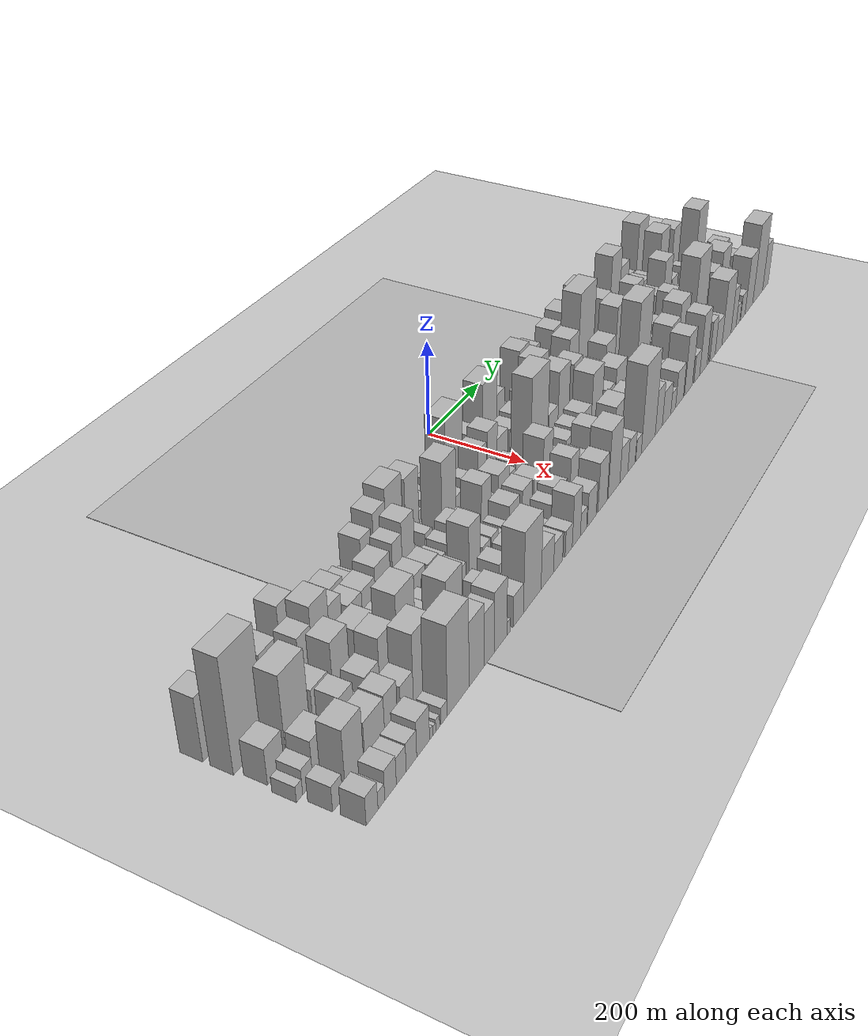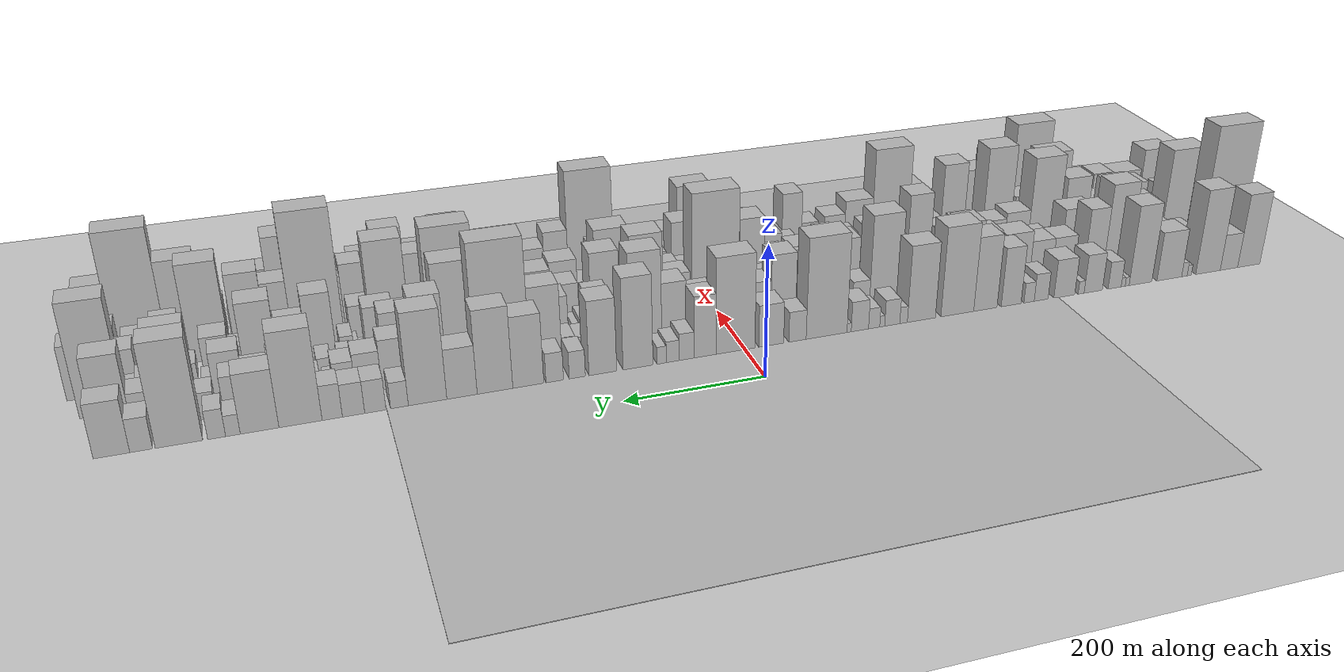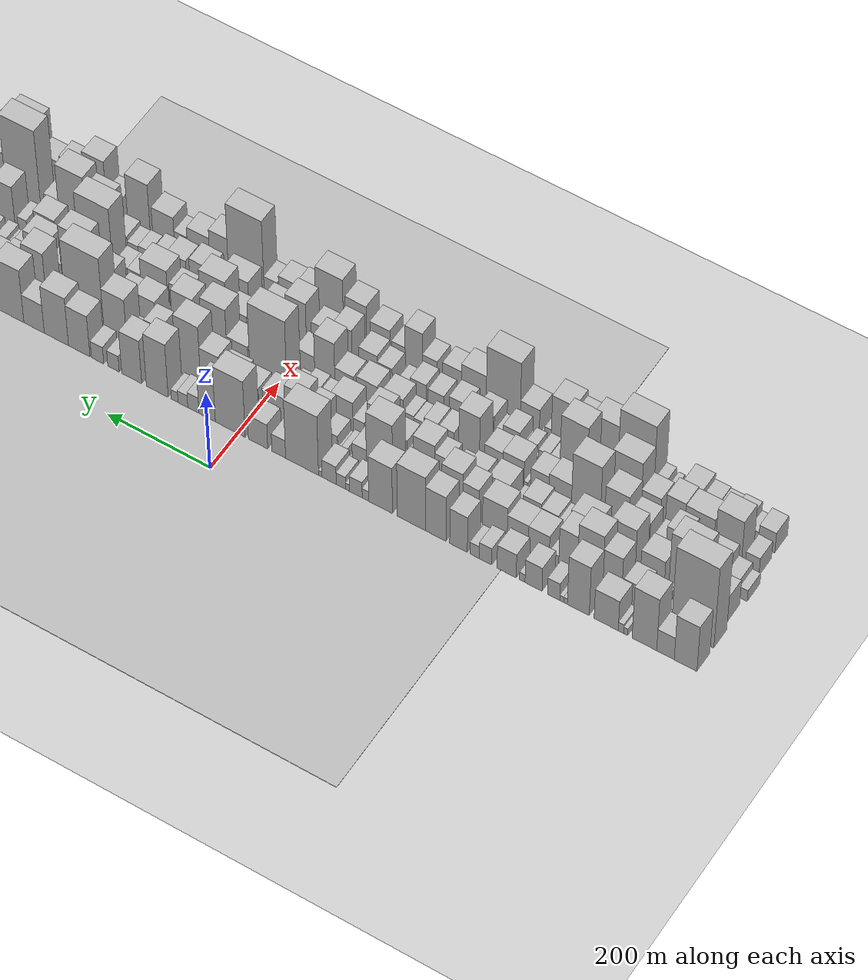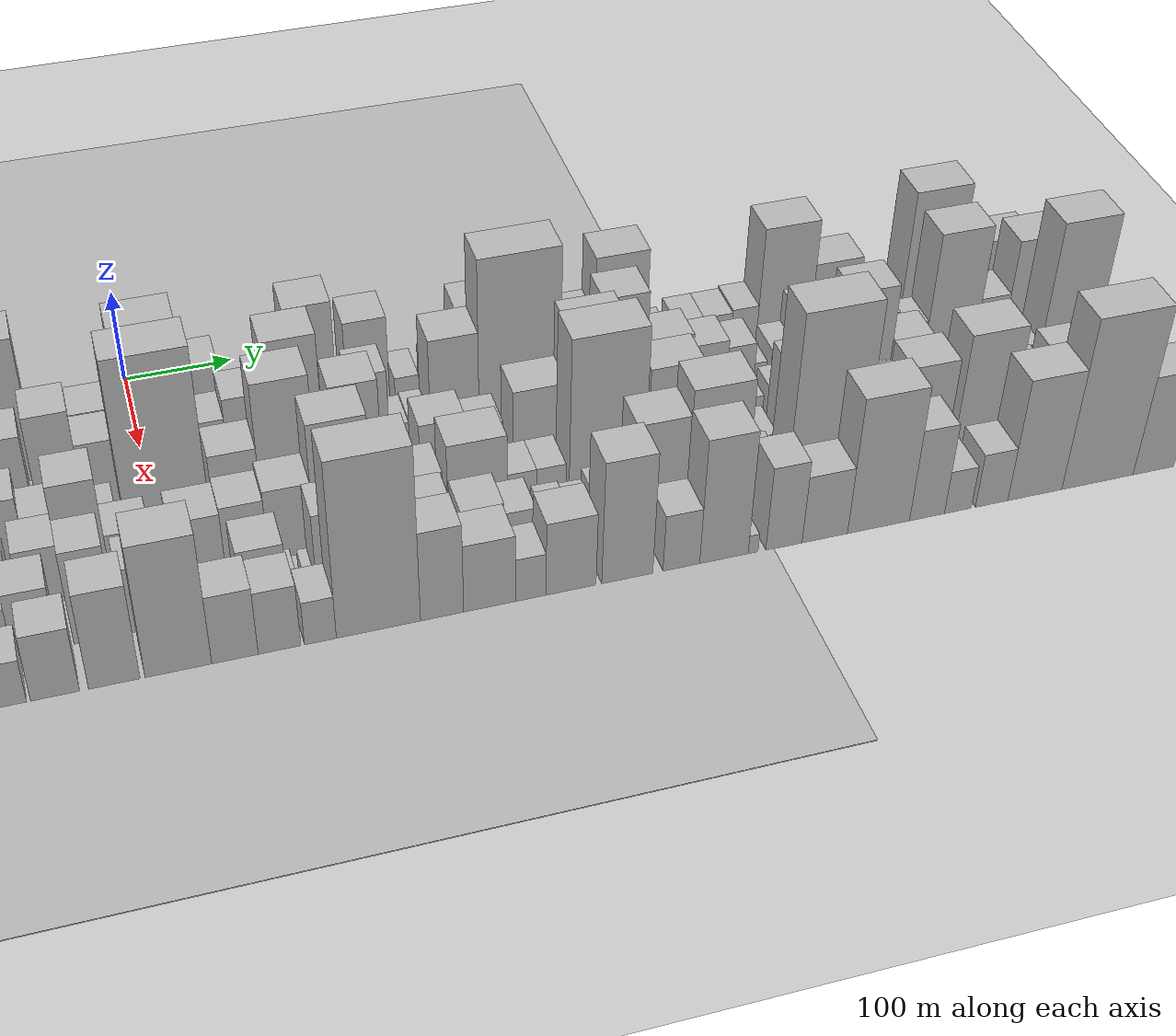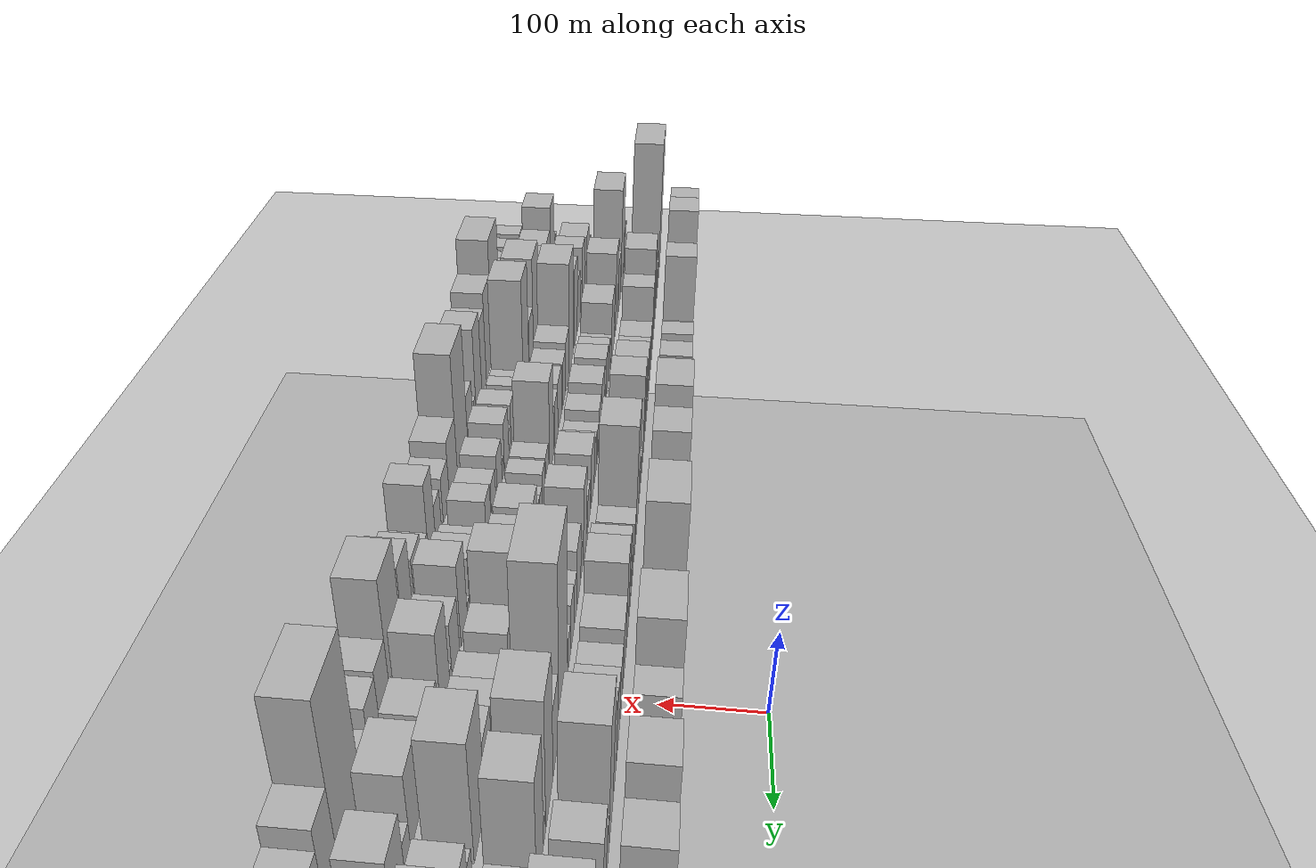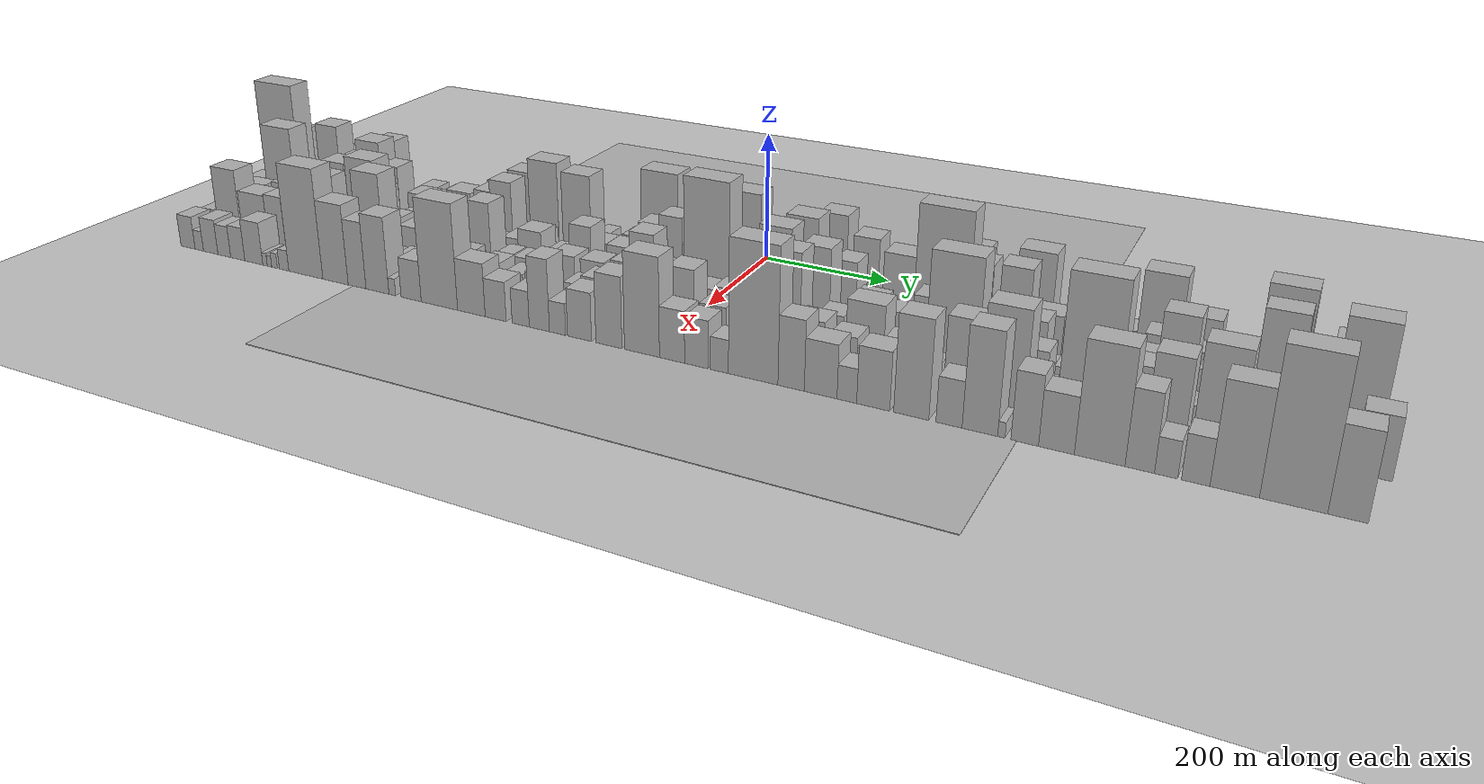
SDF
<?xml version="1.0" encoding="utf-8"?>

<sdf version="1.6">

   <world name="default">

      <gui fullscreen="0">

         <camera name="user_camera">

            <pose>-15 0 4.57585 0 0 0</pose>

            <view_controller>orbit</view_controller>

         </camera>

      </gui>

      <scene>

         <sky>

           <clouds>

             <speed>12</speed>

           </clouds>

         </sky>

         <ambient>0.4 0.4 0.4 1</ambient>

         <background>0.7 0.7 0.7 1</background>

         <shadows>1</shadows>

      </scene>

      <gravity>0 0 -9.8066</gravity>

      <magnetic_field>6e-06 2.3e-05 -4.2e-05</magnetic_field>

      <physics default="0" name="default_physics" type="ode">

         <ode>

            <solver>

               <type>quick</type>

               <iters>10</iters>

               <sor>1.0</sor>

               <use_dynamic_moi_rescaling>0</use_dynamic_moi_rescaling>

            </solver>

            <constraints>

               <cfm>0</cfm>

               <erp>0.2</erp>

               <contact_max_correcting_vel>100</contact_max_correcting_vel>

               <contact_surface_layer>0.001</contact_surface_layer>

            </constraints>

         </ode>

         <max_step_size>0.004</max_step_size>

         <real_time_factor>1</real_time_factor>

         <real_time_update_rate>250</real_time_update_rate>

      </physics>

      <light name="sun" type="directional">

         <cast_shadows>1</cast_shadows>

         <pose>0 0 10 0 0 0</pose>

         <diffuse>0.8 0.8 0.8 1</diffuse>

         <specular>0.2 0.2 0.2 1</specular>

         <attenuation>

            <range>1000</range>

            <constant>0.9</constant>

            <linear>0.01</linear>

            <quadratic>0.001</quadratic>

         </attenuation>

         <direction>-0.5 0.1 -0.9</direction>

      </light>

      <include>

         <name>ground_plane_1</name>

         <uri>model://HANNAS_ground_plane</uri>

         <pose>0 0 0  0 0 0</pose>

      </include>

      <include>

         <name>ground_plane_2</name>

         <uri>model://HANNAS_ground_plane</uri>

         <pose>100 0 0  0 0 0</pose>

      </include>

      <model name="building_1">

         <static>1</static>

         <pose frame="">100.0000 -839.3449 0 0.000000 0.000000 0.000000</pose>

         <link name="link">

            <pose frame="">0 0 61.50 0 0 0</pose>

            <collision name="collision">

               <geometry>

                  <box>

                     <size>40.0000 41.3102 123.0000</size>

                  </box>

               </geometry>

               <max_contacts>10</max_contacts>

               <surface>

                  <contact>

                     <ode/>

                  </contact>

                  <bounce/>

                  <friction>

                     <torsional>

                        <ode/>

                     </torsional>

                     <ode/>

                  </friction>

               </surface>

            </collision>

            <visual name="visual">

               <cast_shadows>0</cast_shadows>

               <geometry>

                  <box>

                     <size>40.0000 41.3102 123.0000</size>

                  </box>

               </geometry>

               <material>

                  <script>

                     <uri>model://HANNAS_wall/materials/scripts</uri>

                     <uri>model://HANNAS_wall/materials/textures</uri>

                     <name>vrc/HANNAS_wall</name>

                  </script>

               </material>

            </visual>

            <self_collide>0</self_collide>

            <enable_wind>0</enable_wind>

            <kinematic>0</kinematic>

         </link>

      </model>

      <model name="building_2">

         <static>1</static>

         <pose frame="">100.0000 -802.6627 0 0.000000 0.000000 0.000000</pose>

         <link name="link">

            <pose frame="">0 0 30.00 0 0 0</pose>

            <collision name="collision">

               <geometry>

                  <box>

                     <size>40.0000 32.0543 60.0000</size>

                  </box>

               </geometry>

               <max_contacts>10</max_contacts>

               <surface>

                  <contact>

                     <ode/>

                  </contact>

                  <bounce/>

                  <friction>

                     <torsional>

                        <ode/>

                     </torsional>

                     <ode/>

                  </friction>

               </surface>

            </collision>

            <visual name="visual">

               <cast_shadows>0</cast_shadows>

               <geometry>

                  <box>

                     <size>40.0000 32.0543 60.0000</size>

                  </box>

               </geometry>

               <material>

                  <script>

                     <uri>model://HANNAS_wall/materials/scripts</uri>

                     <uri>model://HANNAS_wall/materials/textures</uri>

                     <name>vrc/HANNAS_wall</name>

                  </script>

               </material>

            </visual>

            <self_collide>0</self_collide>

            <enable_wind>0</enable_wind>

            <kinematic>0</kinematic>

         </link>

      </model>

      <model name="building_3">

         <static>1</static>

         <pose frame="">100.0000 -764.2436 0 0.000000 0.000000 0.000000</pose>

         <link name="link">

            <pose frame="">0 0 70.50 0 0 0</pose>

            <collision name="collision">

               <geometry>

                  <box>

                     <size>40.0000 44.7839 141.0000</size>

                  </box>

               </geometry>

               <max_contacts>10</max_contacts>

               <surface>

                  <contact>

                     <ode/>

                  </contact>

                  <bounce/>

                  <friction>

                     <torsional>

                        <ode/>

                     </torsional>

                     <ode/>

                  </friction>

               </surface>

            </collision>

            <visual name="visual">

               <cast_shadows>0</cast_shadows>

               <geometry>

                  <box>

                     <size>40.0000 44.7839 141.0000</size>

                  </box>

               </geometry>

               <material>

                  <script>

                     <uri>model://HANNAS_wall/materials/scripts</uri>

                     <uri>model://HANNAS_wall/materials/textures</uri>

                     <name>vrc/HANNAS_wall</name>

                  </script>

               </material>

            </visual>

            <self_collide>0</self_collide>

            <enable_wind>0</enable_wind>

            <kinematic>0</kinematic>

         </link>

      </model>

      <model name="building_4">

         <static>1</static>

         <pose frame="">100.0000 -730.1055 0 0.000000 0.000000 0.000000</pose>

         <link name="link">

            <pose frame="">0 0 9.00 0 0 0</pose>

            <collision name="collision">

               <geometry>

                  <box>

                     <size>40.0000 7.4922 18.0000</size>

                  </box>

               </geometry>

               <max_contacts>10</max_contacts>

               <surface>

                  <contact>

                     <ode/>

                  </contact>

                  <bounce/>

                  <friction>

                     <torsional>

                        <ode/>

                     </torsional>

                     <ode/>

                  </friction>

               </surface>

            </collision>

            <visual name="visual">

               <cast_shadows>0</cast_shadows>

               <geometry>

                  <box>

                     <size>40.0000 7.4922 18.0000</size>

                  </box>

               </geometry>

               <material>

                  <script>

                     <uri>model://HANNAS_wall/materials/scripts</uri>

                     <uri>model://HANNAS_wall/materials/textures</uri>

                     <name>vrc/HANNAS_wall</name>

                  </script>

               </material>

            </visual>

            <self_collide>0</self_collide>

            <enable_wind>0</enable_wind>

            <kinematic>0</kinematic>

         </link>

      </model>

      <model name="building_5">

         <static>1</static>

         <pose frame="">100.0000 -721.3910 0 0.000000 0.000000 0.000000</pose>

         <link name="link">

            <pose frame="">0 0 12.00 0 0 0</pose>

            <collision name="collision">

               <geometry>

                  <box>

                     <size>40.0000 9.9369 24.0000</size>

                  </box>

               </geometry>

               <max_contacts>10</max_contacts>

               <surface>

                  <contact>

                     <ode/>

                  </contact>

                  <bounce/>

                  <friction>

                     <torsional>

                        <ode/>

                     </torsional>

                     <ode/>

                  </friction>

               </surface>

            </collision>

            <visual name="visual">

               <cast_shadows>0</cast_shadows>

               <geometry>

                  <box>

                     <size>40.0000 9.9369 24.0000</size>

                  </box>

               </geometry>

               <material>

                  <script>

                     <uri>model://HANNAS_wall/materials/scripts</uri>

                     <uri>model://HANNAS_wall/materials/textures</uri>

                     <name>vrc/HANNAS_wall</name>

                  </script>

               </material>

            </visual>

            <self_collide>0</self_collide>

            <enable_wind>0</enable_wind>

            <kinematic>0</kinematic>

         </link>

      </model>

      <model name="building_6">

         <static>1</static>

         <pose frame="">100.0000 -694.2377 0 0.000000 0.000000 0.000000</pose>

         <link name="link">

            <pose frame="">0 0 40.50 0 0 0</pose>

            <collision name="collision">

               <geometry>

                  <box>

                     <size>40.0000 44.3697 81.0000</size>

                  </box>

               </geometry>

               <max_contacts>10</max_contacts>

               <surface>

                  <contact>

                     <ode/>

                  </contact>

                  <bounce/>

                  <friction>

                     <torsional>

                        <ode/>

                     </torsional>

                     <ode/>

                  </friction>

               </surface>

            </collision>

            <visual name="visual">

               <cast_shadows>0</cast_shadows>

               <geometry>

                  <box>

                     <size>40.0000 44.3697 81.0000</size>

                  </box>

               </geometry>

               <material>

                  <script>

                     <uri>model://HANNAS_wall/materials/scripts</uri>

                     <uri>model://HANNAS_wall/materials/textures</uri>

                     <name>vrc/HANNAS_wall</name>

                  </script>

               </material>

            </visual>

            <self_collide>0</self_collide>

            <enable_wind>0</enable_wind>

            <kinematic>0</kinematic>

         </link>

      </model>

      <model name="building_7">

         <static>1</static>

         <pose frame="">100.0000 -642.8778 0 0.000000 0.000000 0.000000</pose>

         <link name="link">

            <pose frame="">0 0 66.00 0 0 0</pose>

            <collision name="collision">

               <geometry>

                  <box>

                     <size>40.0000 40.3500 132.0000</size>

                  </box>

               </geometry>

               <max_contacts>10</max_contacts>

               <surface>

                  <contact>

                     <ode/>

                  </contact>

                  <bounce/>

                  <friction>

                     <torsional>

                        <ode/>

                     </torsional>

                     <ode/>

                  </friction>

               </surface>

            </collision>

            <visual name="visual">

               <cast_shadows>0</cast_shadows>

               <geometry>

                  <box>

                     <size>40.0000 40.3500 132.0000</size>

                  </box>

               </geometry>

               <material>

                  <script>

                     <uri>model://HANNAS_wall/materials/scripts</uri>

                     <uri>model://HANNAS_wall/materials/textures</uri>

                     <name>vrc/HANNAS_wall</name>

                  </script>

               </material>

            </visual>

            <self_collide>0</self_collide>

            <enable_wind>0</enable_wind>

            <kinematic>0</kinematic>

         </link>

      </model>

      <model name="building_8">

         <static>1</static>

         <pose frame="">100.0000 -619.2397 0 0.000000 0.000000 0.000000</pose>

         <link name="link">

            <pose frame="">0 0 7.50 0 0 0</pose>

            <collision name="collision">

               <geometry>

                  <box>

                     <size>40.0000 6.9262 15.0000</size>

                  </box>

               </geometry>

               <max_contacts>10</max_contacts>

               <surface>

                  <contact>

                     <ode/>

                  </contact>

                  <bounce/>

                  <friction>

                     <torsional>

                        <ode/>

                     </torsional>

                     <ode/>

                  </friction>

               </surface>

            </collision>

            <visual name="visual">

               <cast_shadows>0</cast_shadows>

               <geometry>

                  <box>

                     <size>40.0000 6.9262 15.0000</size>

                  </box>

               </geometry>

               <material>

                  <script>

                     <uri>model://HANNAS_wall/materials/scripts</uri>

                     <uri>model://HANNAS_wall/materials/textures</uri>

                     <name>vrc/HANNAS_wall</name>

                  </script>

               </material>

            </visual>

            <self_collide>0</self_collide>

            <enable_wind>0</enable_wind>

            <kinematic>0</kinematic>

         </link>

      </model>

      <model name="building_9">

         <static>1</static>

         <pose frame="">100.0000 -612.2614 0 0.000000 0.000000 0.000000</pose>

         <link name="link">

            <pose frame="">0 0 7.50 0 0 0</pose>

            <collision name="collision">

               <geometry>

                  <box>

                     <size>40.0000 7.0304 15.0000</size>

                  </box>

               </geometry>

               <max_contacts>10</max_contacts>

               <surface>

                  <contact>

                     <ode/>

                  </contact>

                  <bounce/>

                  <friction>

                     <torsional>

                        <ode/>

                     </torsional>

                     <ode/>

                  </friction>

               </surface>

            </collision>

            <visual name="visual">

               <cast_shadows>0</cast_shadows>

               <geometry>

                  <box>

                     <size>40.0000 7.0304 15.0000</size>

                  </box>

               </geometry>

               <material>

                  <script>

                     <uri>model://HANNAS_wall/materials/scripts</uri>

                     <uri>model://HANNAS_wall/materials/textures</uri>

                     <name>vrc/HANNAS_wall</name>

                  </script>

               </material>

            </visual>

            <self_collide>0</self_collide>

            <enable_wind>0</enable_wind>

            <kinematic>0</kinematic>

         </link>

      </model>

      <model name="building_10">

         <static>1</static>

         <pose frame="">100.0000 -597.3132 0 0.000000 0.000000 0.000000</pose>

         <link name="link">

            <pose frame="">0 0 22.50 0 0 0</pose>

            <collision name="collision">

               <geometry>

                  <box>

                     <size>40.0000 22.8660 45.0000</size>

                  </box>

               </geometry>

               <max_contacts>10</max_contacts>

               <surface>

                  <contact>

                     <ode/>

                  </contact>

                  <bounce/>

                  <friction>

                     <torsional>

                        <ode/>

                     </torsional>

                     <ode/>

                  </friction>

               </surface>

            </collision>

            <visual name="visual">

               <cast_shadows>0</cast_shadows>

               <geometry>

                  <box>

                     <size>40.0000 22.8660 45.0000</size>

                  </box>

               </geometry>

               <material>

                  <script>

                     <uri>model://HANNAS_wall/materials/scripts</uri>

                     <uri>model://HANNAS_wall/materials/textures</uri>

                     <name>vrc/HANNAS_wall</name>

                  </script>

               </material>

            </visual>

            <self_collide>0</self_collide>

            <enable_wind>0</enable_wind>

            <kinematic>0</kinematic>

         </link>

      </model>

      <model name="building_11">

         <static>1</static>

         <pose frame="">100.0000 -560.0543 0 0.000000 0.000000 0.000000</pose>

         <link name="link">

            <pose frame="">0 0 31.50 0 0 0</pose>

            <collision name="collision">

               <geometry>

                  <box>

                     <size>40.0000 31.6517 63.0000</size>

                  </box>

               </geometry>

               <max_contacts>10</max_contacts>

               <surface>

                  <contact>

                     <ode/>

                  </contact>

                  <bounce/>

                  <friction>

                     <torsional>

                        <ode/>

                     </torsional>

                     <ode/>

                  </friction>

               </surface>

            </collision>

            <visual name="visual">

               <cast_shadows>0</cast_shadows>

               <geometry>

                  <box>

                     <size>40.0000 31.6517 63.0000</size>

                  </box>

               </geometry>

               <material>

                  <script>

                     <uri>model://HANNAS_wall/materials/scripts</uri>

                     <uri>model://HANNAS_wall/materials/textures</uri>

                     <name>vrc/HANNAS_wall</name>

                  </script>

               </material>

            </visual>

            <self_collide>0</self_collide>

            <enable_wind>0</enable_wind>

            <kinematic>0</kinematic>

         </link>

      </model>

      <model name="building_12">

         <static>1</static>

         <pose frame="">100.0000 -539.1166 0 0.000000 0.000000 0.000000</pose>

         <link name="link">

            <pose frame="">0 0 10.50 0 0 0</pose>

            <collision name="collision">

               <geometry>

                  <box>

                     <size>40.0000 10.2237 21.0000</size>

                  </box>

               </geometry>

               <max_contacts>10</max_contacts>

               <surface>

                  <contact>

                     <ode/>

                  </contact>

                  <bounce/>

                  <friction>

                     <torsional>

                        <ode/>

                     </torsional>

                     <ode/>

                  </friction>

               </surface>

            </collision>

            <visual name="visual">

               <cast_shadows>0</cast_shadows>

               <geometry>

                  <box>

                     <size>40.0000 10.2237 21.0000</size>

                  </box>

               </geometry>

               <material>

                  <script>

                     <uri>model://HANNAS_wall/materials/scripts</uri>

                     <uri>model://HANNAS_wall/materials/textures</uri>

                     <name>vrc/HANNAS_wall</name>

                  </script>

               </material>

            </visual>

            <self_collide>0</self_collide>

            <enable_wind>0</enable_wind>

            <kinematic>0</kinematic>

         </link>

      </model>

      <model name="building_13">

         <static>1</static>

         <pose frame="">100.0000 -510.1576 0 0.000000 0.000000 0.000000</pose>

         <link name="link">

            <pose frame="">0 0 31.50 0 0 0</pose>

            <collision name="collision">

               <geometry>

                  <box>

                     <size>40.0000 35.6943 63.0000</size>

                  </box>

               </geometry>

               <max_contacts>10</max_contacts>

               <surface>

                  <contact>

                     <ode/>

                  </contact>

                  <bounce/>

                  <friction>

                     <torsional>

                        <ode/>

                     </torsional>

                     <ode/>

                  </friction>

               </surface>

            </collision>

            <visual name="visual">

               <cast_shadows>0</cast_shadows>

               <geometry>

                  <box>

                     <size>40.0000 35.6943 63.0000</size>

                  </box>

               </geometry>

               <material>

                  <script>

                     <uri>model://HANNAS_wall/materials/scripts</uri>

                     <uri>model://HANNAS_wall/materials/textures</uri>

                     <name>vrc/HANNAS_wall</name>

                  </script>

               </material>

            </visual>

            <self_collide>0</self_collide>

            <enable_wind>0</enable_wind>

            <kinematic>0</kinematic>

         </link>

      </model>

      <model name="building_14">

         <static>1</static>

         <pose frame="">100.0000 -470.5793 0 0.000000 0.000000 0.000000</pose>

         <link name="link">

            <pose frame="">0 0 22.50 0 0 0</pose>

            <collision name="collision">

               <geometry>

                  <box>

                     <size>40.0000 23.4623 45.0000</size>

                  </box>

               </geometry>

               <max_contacts>10</max_contacts>

               <surface>

                  <contact>

                     <ode/>

                  </contact>

                  <bounce/>

                  <friction>

                     <torsional>

                        <ode/>

                     </torsional>

                     <ode/>

                  </friction>

               </surface>

            </collision>

            <visual name="visual">

               <cast_shadows>0</cast_shadows>

               <geometry>

                  <box>

                     <size>40.0000 23.4623 45.0000</size>

                  </box>

               </geometry>

               <material>

                  <script>

                     <uri>model://HANNAS_wall/materials/scripts</uri>

                     <uri>model://HANNAS_wall/materials/textures</uri>

                     <name>vrc/HANNAS_wall</name>

                  </script>

               </material>

            </visual>

            <self_collide>0</self_collide>

            <enable_wind>0</enable_wind>

            <kinematic>0</kinematic>

         </link>

      </model>

      <model name="building_15">

         <static>1</static>

         <pose frame="">100.0000 -450.2433 0 0.000000 0.000000 0.000000</pose>

         <link name="link">

            <pose frame="">0 0 16.50 0 0 0</pose>

            <collision name="collision">

               <geometry>

                  <box>

                     <size>40.0000 17.2098 33.0000</size>

                  </box>

               </geometry>

               <max_contacts>10</max_contacts>

               <surface>

                  <contact>

                     <ode/>

                  </contact>

                  <bounce/>

                  <friction>

                     <torsional>

                        <ode/>

                     </torsional>

                     <ode/>

                  </friction>

               </surface>

            </collision>

            <visual name="visual">

               <cast_shadows>0</cast_shadows>

               <geometry>

                  <box>

                     <size>40.0000 17.2098 33.0000</size>

                  </box>

               </geometry>

               <material>

                  <script>

                     <uri>model://HANNAS_wall/materials/scripts</uri>

                     <uri>model://HANNAS_wall/materials/textures</uri>

                     <name>vrc/HANNAS_wall</name>

                  </script>

               </material>

            </visual>

            <self_collide>0</self_collide>

            <enable_wind>0</enable_wind>

            <kinematic>0</kinematic>

         </link>

      </model>

      <model name="building_16">

         <static>1</static>

         <pose frame="">100.0000 -420.1182 0 0.000000 0.000000 0.000000</pose>

         <link name="link">

            <pose frame="">0 0 48.00 0 0 0</pose>

            <collision name="collision">

               <geometry>

                  <box>

                     <size>40.0000 33.0405 96.0000</size>

                  </box>

               </geometry>

               <max_contacts>10</max_contacts>

               <surface>

                  <contact>

                     <ode/>

                  </contact>

                  <bounce/>

                  <friction>

                     <torsional>

                        <ode/>

                     </torsional>

                     <ode/>

                  </friction>

               </surface>

            </collision>

            <visual name="visual">

               <cast_shadows>0</cast_shadows>

               <geometry>

                  <box>

                     <size>40.0000 33.0405 96.0000</size>

                  </box>

               </geometry>

               <material>

                  <script>

                     <uri>model://HANNAS_wall/materials/scripts</uri>

                     <uri>model://HANNAS_wall/materials/textures</uri>

                     <name>vrc/HANNAS_wall</name>

                  </script>

               </material>

            </visual>

            <self_collide>0</self_collide>

            <enable_wind>0</enable_wind>

            <kinematic>0</kinematic>

         </link>

      </model>

      <model name="building_17">

         <static>1</static>

         <pose frame="">100.0000 -377.3497 0 0.000000 0.000000 0.000000</pose>

         <link name="link">

            <pose frame="">0 0 60.00 0 0 0</pose>

            <collision name="collision">

               <geometry>

                  <box>

                     <size>40.0000 38.4965 120.0000</size>

                  </box>

               </geometry>

               <max_contacts>10</max_contacts>

               <surface>

                  <contact>

                     <ode/>

                  </contact>

                  <bounce/>

                  <friction>

                     <torsional>

                        <ode/>

                     </torsional>

                     <ode/>

                  </friction>

               </surface>

            </collision>

            <visual name="visual">

               <cast_shadows>0</cast_shadows>

               <geometry>

                  <box>

                     <size>40.0000 38.4965 120.0000</size>

                  </box>

               </geometry>

               <material>

                  <script>

                     <uri>model://HANNAS_wall/materials/scripts</uri>

                     <uri>model://HANNAS_wall/materials/textures</uri>

                     <name>vrc/HANNAS_wall</name>

                  </script>

               </material>

            </visual>

            <self_collide>0</self_collide>

            <enable_wind>0</enable_wind>

            <kinematic>0</kinematic>

         </link>

      </model>

      <model name="building_18">

         <static>1</static>

         <pose frame="">100.0000 -331.2508 0 0.000000 0.000000 0.000000</pose>

         <link name="link">

            <pose frame="">0 0 72.00 0 0 0</pose>

            <collision name="collision">

               <geometry>

                  <box>

                     <size>40.0000 53.7013 144.0000</size>

                  </box>

               </geometry>

               <max_contacts>10</max_contacts>

               <surface>

                  <contact>

                     <ode/>

                  </contact>

                  <bounce/>

                  <friction>

                     <torsional>

                        <ode/>

                     </torsional>

                     <ode/>

                  </friction>

               </surface>

            </collision>

            <visual name="visual">

               <cast_shadows>0</cast_shadows>

               <geometry>

                  <box>

                     <size>40.0000 53.7013 144.0000</size>

                  </box>

               </geometry>

               <material>

                  <script>

                     <uri>model://HANNAS_wall/materials/scripts</uri>

                     <uri>model://HANNAS_wall/materials/textures</uri>

                     <name>vrc/HANNAS_wall</name>

                  </script>

               </material>

            </visual>

            <self_collide>0</self_collide>

            <enable_wind>0</enable_wind>

            <kinematic>0</kinematic>

         </link>

      </model>

      <model name="building_19">

         <static>1</static>

         <pose frame="">100.0000 -272.8662 0 0.000000 0.000000 0.000000</pose>

         <link name="link">

            <pose frame="">0 0 61.50 0 0 0</pose>

            <collision name="collision">

               <geometry>

                  <box>

                     <size>40.0000 45.0677 123.0000</size>

                  </box>

               </geometry>

               <max_contacts>10</max_contacts>

               <surface>

                  <contact>

                     <ode/>

                  </contact>

                  <bounce/>

                  <friction>

                     <torsional>

                        <ode/>

                     </torsional>

                     <ode/>

                  </friction>

               </surface>

            </collision>

            <visual name="visual">

               <cast_shadows>0</cast_shadows>

               <geometry>

                  <box>

                     <size>40.0000 45.0677 123.0000</size>

                  </box>

               </geometry>

               <material>

                  <script>

                     <uri>model://HANNAS_wall/materials/scripts</uri>

                     <uri>model://HANNAS_wall/materials/textures</uri>

                     <name>vrc/HANNAS_wall</name>

                  </script>

               </material>

            </visual>

            <self_collide>0</self_collide>

            <enable_wind>0</enable_wind>

            <kinematic>0</kinematic>

         </link>

      </model>

      <model name="building_20">

         <static>1</static>

         <pose frame="">100.0000 -244.2768 0 0.000000 0.000000 0.000000</pose>

         <link name="link">

            <pose frame="">0 0 13.50 0 0 0</pose>

            <collision name="collision">

               <geometry>

                  <box>

                     <size>40.0000 12.1112 27.0000</size>

                  </box>

               </geometry>

               <max_contacts>10</max_contacts>

               <surface>

                  <contact>

                     <ode/>

                  </contact>

                  <bounce/>

                  <friction>

                     <torsional>

                        <ode/>

                     </torsional>

                     <ode/>

                  </friction>

               </surface>

            </collision>

            <visual name="visual">

               <cast_shadows>0</cast_shadows>

               <geometry>

                  <box>

                     <size>40.0000 12.1112 27.0000</size>

                  </box>

               </geometry>

               <material>

                  <script>

                     <uri>model://HANNAS_wall/materials/scripts</uri>

                     <uri>model://HANNAS_wall/materials/textures</uri>

                     <name>vrc/HANNAS_wall</name>

                  </script>

               </material>

            </visual>

            <self_collide>0</self_collide>

            <enable_wind>0</enable_wind>

            <kinematic>0</kinematic>

         </link>

      </model>

      <model name="building_21">

         <static>1</static>

         <pose frame="">100.0000 -226.2192 0 0.000000 0.000000 0.000000</pose>

         <link name="link">

            <pose frame="">0 0 21.00 0 0 0</pose>

            <collision name="collision">

               <geometry>

                  <box>

                     <size>40.0000 24.0040 42.0000</size>

                  </box>

               </geometry>

               <max_contacts>10</max_contacts>

               <surface>

                  <contact>

                     <ode/>

                  </contact>

                  <bounce/>

                  <friction>

                     <torsional>

                        <ode/>

                     </torsional>

                     <ode/>

                  </friction>

               </surface>

            </collision>

            <visual name="visual">

               <cast_shadows>0</cast_shadows>

               <geometry>

                  <box>

                     <size>40.0000 24.0040 42.0000</size>

                  </box>

               </geometry>

               <material>

                  <script>

                     <uri>model://HANNAS_wall/materials/scripts</uri>

                     <uri>model://HANNAS_wall/materials/textures</uri>

                     <name>vrc/HANNAS_wall</name>

                  </script>

               </material>

            </visual>

            <self_collide>0</self_collide>

            <enable_wind>0</enable_wind>

            <kinematic>0</kinematic>

         </link>

      </model>

      <model name="building_22">

         <static>1</static>

         <pose frame="">100.0000 -210.3135 0 0.000000 0.000000 0.000000</pose>

         <link name="link">

            <pose frame="">0 0 9.00 0 0 0</pose>

            <collision name="collision">

               <geometry>

                  <box>

                     <size>40.0000 7.8074 18.0000</size>

                  </box>

               </geometry>

               <max_contacts>10</max_contacts>

               <surface>

                  <contact>

                     <ode/>

                  </contact>

                  <bounce/>

                  <friction>

                     <torsional>

                        <ode/>

                     </torsional>

                     <ode/>

                  </friction>

               </surface>

            </collision>

            <visual name="visual">

               <cast_shadows>0</cast_shadows>

               <geometry>

                  <box>

                     <size>40.0000 7.8074 18.0000</size>

                  </box>

               </geometry>

               <material>

                  <script>

                     <uri>model://HANNAS_wall/materials/scripts</uri>

                     <uri>model://HANNAS_wall/materials/textures</uri>

                     <name>vrc/HANNAS_wall</name>

                  </script>

               </material>

            </visual>

            <self_collide>0</self_collide>

            <enable_wind>0</enable_wind>

            <kinematic>0</kinematic>

         </link>

      </model>

      <model name="building_23">

         <static>1</static>

         <pose frame="">100.0000 -197.5785 0 0.000000 0.000000 0.000000</pose>

         <link name="link">

            <pose frame="">0 0 16.50 0 0 0</pose>

            <collision name="collision">

               <geometry>

                  <box>

                     <size>40.0000 17.6627 33.0000</size>

                  </box>

               </geometry>

               <max_contacts>10</max_contacts>

               <surface>

                  <contact>

                     <ode/>

                  </contact>

                  <bounce/>

                  <friction>

                     <torsional>

                        <ode/>

                     </torsional>

                     <ode/>

                  </friction>

               </surface>

            </collision>

            <visual name="visual">

               <cast_shadows>0</cast_shadows>

               <geometry>

                  <box>

                     <size>40.0000 17.6627 33.0000</size>

                  </box>

               </geometry>

               <material>

                  <script>

                     <uri>model://HANNAS_wall/materials/scripts</uri>

                     <uri>model://HANNAS_wall/materials/textures</uri>

                     <name>vrc/HANNAS_wall</name>

                  </script>

               </material>

            </visual>

            <self_collide>0</self_collide>

            <enable_wind>0</enable_wind>

            <kinematic>0</kinematic>

         </link>

      </model>

      <model name="building_24">

         <static>1</static>

         <pose frame="">100.0000 -175.1531 0 0.000000 0.000000 0.000000</pose>

         <link name="link">

            <pose frame="">0 0 24.00 0 0 0</pose>

            <collision name="collision">

               <geometry>

                  <box>

                     <size>40.0000 27.1880 48.0000</size>

                  </box>

               </geometry>

               <max_contacts>10</max_contacts>

               <surface>

                  <contact>

                     <ode/>

                  </contact>

                  <bounce/>

                  <friction>

                     <torsional>

                        <ode/>

                     </torsional>

                     <ode/>

                  </friction>

               </surface>

            </collision>

            <visual name="visual">

               <cast_shadows>0</cast_shadows>

               <geometry>

                  <box>

                     <size>40.0000 27.1880 48.0000</size>

                  </box>

               </geometry>

               <material>

                  <script>

                     <uri>model://HANNAS_wall/materials/scripts</uri>

                     <uri>model://HANNAS_wall/materials/textures</uri>

                     <name>vrc/HANNAS_wall</name>

                  </script>

               </material>

            </visual>

            <self_collide>0</self_collide>

            <enable_wind>0</enable_wind>

            <kinematic>0</kinematic>

         </link>

      </model>

      <model name="building_25">

         <static>1</static>

         <pose frame="">100.0000 -158.2635 0 0.000000 0.000000 0.000000</pose>

         <link name="link">

            <pose frame="">0 0 7.50 0 0 0</pose>

            <collision name="collision">

               <geometry>

                  <box>

                     <size>40.0000 6.5912 15.0000</size>

                  </box>

               </geometry>

               <max_contacts>10</max_contacts>

               <surface>

                  <contact>

                     <ode/>

                  </contact>

                  <bounce/>

                  <friction>

                     <torsional>

                        <ode/>

                     </torsional>

                     <ode/>

                  </friction>

               </surface>

            </collision>

            <visual name="visual">

               <cast_shadows>0</cast_shadows>

               <geometry>

                  <box>

                     <size>40.0000 6.5912 15.0000</size>

                  </box>

               </geometry>

               <material>

                  <script>

                     <uri>model://HANNAS_wall/materials/scripts</uri>

                     <uri>model://HANNAS_wall/materials/textures</uri>

                     <name>vrc/HANNAS_wall</name>

                  </script>

               </material>

            </visual>

            <self_collide>0</self_collide>

            <enable_wind>0</enable_wind>

            <kinematic>0</kinematic>

         </link>

      </model>

      <model name="building_26">

         <static>1</static>

         <pose frame="">100.0000 -123.3607 0 0.000000 0.000000 0.000000</pose>

         <link name="link">

            <pose frame="">0 0 79.50 0 0 0</pose>

            <collision name="collision">

               <geometry>

                  <box>

                     <size>40.0000 63.2144 159.0000</size>

                  </box>

               </geometry>

               <max_contacts>10</max_contacts>

               <surface>

                  <contact>

                     <ode/>

                  </contact>

                  <bounce/>

                  <friction>

                     <torsional>

                        <ode/>

                     </torsional>

                     <ode/>

                  </friction>

               </surface>

            </collision>

            <visual name="visual">

               <cast_shadows>0</cast_shadows>

               <geometry>

                  <box>

                     <size>40.0000 63.2144 159.0000</size>

                  </box>

               </geometry>

               <material>

                  <script>

                     <uri>model://HANNAS_wall/materials/scripts</uri>

                     <uri>model://HANNAS_wall/materials/textures</uri>

                     <name>vrc/HANNAS_wall</name>

                  </script>

               </material>

            </visual>

            <self_collide>0</self_collide>

            <enable_wind>0</enable_wind>

            <kinematic>0</kinematic>

         </link>

      </model>

      <model name="building_27">

         <static>1</static>

         <pose frame="">100.0000 -78.5831 0 0.000000 0.000000 0.000000</pose>

         <link name="link">

            <pose frame="">0 0 24.00 0 0 0</pose>

            <collision name="collision">

               <geometry>

                  <box>

                     <size>40.0000 26.3408 48.0000</size>

                  </box>

               </geometry>

               <max_contacts>10</max_contacts>

               <surface>

                  <contact>

                     <ode/>

                  </contact>

                  <bounce/>

                  <friction>

                     <torsional>

                        <ode/>

                     </torsional>

                     <ode/>

                  </friction>

               </surface>

            </collision>

            <visual name="visual">

               <cast_shadows>0</cast_shadows>

               <geometry>

                  <box>

                     <size>40.0000 26.3408 48.0000</size>

                  </box>

               </geometry>

               <material>

                  <script>

                     <uri>model://HANNAS_wall/materials/scripts</uri>

                     <uri>model://HANNAS_wall/materials/textures</uri>

                     <name>vrc/HANNAS_wall</name>

                  </script>

               </material>

            </visual>

            <self_collide>0</self_collide>

            <enable_wind>0</enable_wind>

            <kinematic>0</kinematic>

         </link>

      </model>

      <model name="building_28">

         <static>1</static>

         <pose frame="">100.0000 -38.6893 0 0.000000 0.000000 0.000000</pose>

         <link name="link">

            <pose frame="">0 0 33.00 0 0 0</pose>

            <collision name="collision">

               <geometry>

                  <box>

                     <size>40.0000 37.4467 66.0000</size>

                  </box>

               </geometry>

               <max_contacts>10</max_contacts>

               <surface>

                  <contact>

                     <ode/>

                  </contact>

                  <bounce/>

                  <friction>

                     <torsional>

                        <ode/>

                     </torsional>

                     <ode/>

                  </friction>

               </surface>

            </collision>

            <visual name="visual">

               <cast_shadows>0</cast_shadows>

               <geometry>

                  <box>

                     <size>40.0000 37.4467 66.0000</size>

                  </box>

               </geometry>

               <material>

                  <script>

                     <uri>model://HANNAS_wall/materials/scripts</uri>

                     <uri>model://HANNAS_wall/materials/textures</uri>

                     <name>vrc/HANNAS_wall</name>

                  </script>

               </material>

            </visual>

            <self_collide>0</self_collide>

            <enable_wind>0</enable_wind>

            <kinematic>0</kinematic>

         </link>

      </model>

      <model name="building_29">

         <static>1</static>

         <pose frame="">100.0000 14.9966 0 0.000000 0.000000 0.000000</pose>

         <link name="link">

            <pose frame="">0 0 75.00 0 0 0</pose>

            <collision name="collision">

               <geometry>

                  <box>

                     <size>40.0000 57.9252 150.0000</size>

                  </box>

               </geometry>

               <max_contacts>10</max_contacts>

               <surface>

                  <contact>

                     <ode/>

                  </contact>

                  <bounce/>

                  <friction>

                     <torsional>

                        <ode/>

                     </torsional>

                     <ode/>

                  </friction>

               </surface>

            </collision>

            <visual name="visual">

               <cast_shadows>0</cast_shadows>

               <geometry>

                  <box>

                     <size>40.0000 57.9252 150.0000</size>

                  </box>

               </geometry>

               <material>

                  <script>

                     <uri>model://HANNAS_wall/materials/scripts</uri>

                     <uri>model://HANNAS_wall/materials/textures</uri>

                     <name>vrc/HANNAS_wall</name>

                  </script>

               </material>

            </visual>

            <self_collide>0</self_collide>

            <enable_wind>0</enable_wind>

            <kinematic>0</kinematic>

         </link>

      </model>

      <model name="building_30">

         <static>1</static>

         <pose frame="">100.0000 59.9038 0 0.000000 0.000000 0.000000</pose>

         <link name="link">

            <pose frame="">0 0 48.00 0 0 0</pose>

            <collision name="collision">

               <geometry>

                  <box>

                     <size>40.0000 31.8891 96.0000</size>

                  </box>

               </geometry>

               <max_contacts>10</max_contacts>

               <surface>

                  <contact>

                     <ode/>

                  </contact>

                  <bounce/>

                  <friction>

                     <torsional>

                        <ode/>

                     </torsional>

                     <ode/>

                  </friction>

               </surface>

            </collision>

            <visual name="visual">

               <cast_shadows>0</cast_shadows>

               <geometry>

                  <box>

                     <size>40.0000 31.8891 96.0000</size>

                  </box>

               </geometry>

               <material>

                  <script>

                     <uri>model://HANNAS_wall/materials/scripts</uri>

                     <uri>model://HANNAS_wall/materials/textures</uri>

                     <name>vrc/HANNAS_wall</name>

                  </script>

               </material>

            </visual>

            <self_collide>0</self_collide>

            <enable_wind>0</enable_wind>

            <kinematic>0</kinematic>

         </link>

      </model>

      <model name="building_31">

         <static>1</static>

         <pose frame="">100.0000 86.7170 0 0.000000 0.000000 0.000000</pose>

         <link name="link">

            <pose frame="">0 0 21.00 0 0 0</pose>

            <collision name="collision">

               <geometry>

                  <box>

                     <size>40.0000 21.7373 42.0000</size>

                  </box>

               </geometry>

               <max_contacts>10</max_contacts>

               <surface>

                  <contact>

                     <ode/>

                  </contact>

                  <bounce/>

                  <friction>

                     <torsional>

                        <ode/>

                     </torsional>

                     <ode/>

                  </friction>

               </surface>

            </collision>

            <visual name="visual">

               <cast_shadows>0</cast_shadows>

               <geometry>

                  <box>

                     <size>40.0000 21.7373 42.0000</size>

                  </box>

               </geometry>

               <material>

                  <script>

                     <uri>model://HANNAS_wall/materials/scripts</uri>

                     <uri>model://HANNAS_wall/materials/textures</uri>

                     <name>vrc/HANNAS_wall</name>

                  </script>

               </material>

            </visual>

            <self_collide>0</self_collide>

            <enable_wind>0</enable_wind>

            <kinematic>0</kinematic>

         </link>

      </model>

      <model name="building_32">

         <static>1</static>

         <pose frame="">100.0000 107.1143 0 0.000000 0.000000 0.000000</pose>

         <link name="link">

            <pose frame="">0 0 16.50 0 0 0</pose>

            <collision name="collision">

               <geometry>

                  <box>

                     <size>40.0000 19.0572 33.0000</size>

                  </box>

               </geometry>

               <max_contacts>10</max_contacts>

               <surface>

                  <contact>

                     <ode/>

                  </contact>

                  <bounce/>

                  <friction>

                     <torsional>

                        <ode/>

                     </torsional>

                     <ode/>

                  </friction>

               </surface>

            </collision>

            <visual name="visual">

               <cast_shadows>0</cast_shadows>

               <geometry>

                  <box>

                     <size>40.0000 19.0572 33.0000</size>

                  </box>

               </geometry>

               <material>

                  <script>

                     <uri>model://HANNAS_wall/materials/scripts</uri>

                     <uri>model://HANNAS_wall/materials/textures</uri>

                     <name>vrc/HANNAS_wall</name>

                  </script>

               </material>

            </visual>

            <self_collide>0</self_collide>

            <enable_wind>0</enable_wind>

            <kinematic>0</kinematic>

         </link>

      </model>

      <model name="building_33">

         <static>1</static>

         <pose frame="">100.0000 123.2830 0 0.000000 0.000000 0.000000</pose>

         <link name="link">

            <pose frame="">0 0 13.50 0 0 0</pose>

            <collision name="collision">

               <geometry>

                  <box>

                     <size>40.0000 13.2802 27.0000</size>

                  </box>

               </geometry>

               <max_contacts>10</max_contacts>

               <surface>

                  <contact>

                     <ode/>

                  </contact>

                  <bounce/>

                  <friction>

                     <torsional>

                        <ode/>

                     </torsional>

                     <ode/>

                  </friction>

               </surface>

            </collision>

            <visual name="visual">

               <cast_shadows>0</cast_shadows>

               <geometry>

                  <box>

                     <size>40.0000 13.2802 27.0000</size>

                  </box>

               </geometry>

               <material>

                  <script>

                     <uri>model://HANNAS_wall/materials/scripts</uri>

                     <uri>model://HANNAS_wall/materials/textures</uri>

                     <name>vrc/HANNAS_wall</name>

                  </script>

               </material>

            </visual>

            <self_collide>0</self_collide>

            <enable_wind>0</enable_wind>

            <kinematic>0</kinematic>

         </link>

      </model>

      <model name="building_34">

         <static>1</static>

         <pose frame="">100.0000 157.3321 0 0.000000 0.000000 0.000000</pose>

         <link name="link">

            <pose frame="">0 0 70.50 0 0 0</pose>

            <collision name="collision">

               <geometry>

                  <box>

                     <size>40.0000 42.8180 141.0000</size>

                  </box>

               </geometry>

               <max_contacts>10</max_contacts>

               <surface>

                  <contact>

                     <ode/>

                  </contact>

                  <bounce/>

                  <friction>

                     <torsional>

                        <ode/>

                     </torsional>

                     <ode/>

                  </friction>

               </surface>

            </collision>

            <visual name="visual">

               <cast_shadows>0</cast_shadows>

               <geometry>

                  <box>

                     <size>40.0000 42.8180 141.0000</size>

                  </box>

               </geometry>

               <material>

                  <script>

                     <uri>model://HANNAS_wall/materials/scripts</uri>

                     <uri>model://HANNAS_wall/materials/textures</uri>

                     <name>vrc/HANNAS_wall</name>

                  </script>

               </material>

            </visual>

            <self_collide>0</self_collide>

            <enable_wind>0</enable_wind>

            <kinematic>0</kinematic>

         </link>

      </model>

      <model name="building_35">

         <static>1</static>

         <pose frame="">100.0000 207.3380 0 0.000000 0.000000 0.000000</pose>

         <link name="link">

            <pose frame="">0 0 57.00 0 0 0</pose>

            <collision name="collision">

               <geometry>

                  <box>

                     <size>40.0000 39.1938 114.0000</size>

                  </box>

               </geometry>

               <max_contacts>10</max_contacts>

               <surface>

                  <contact>

                     <ode/>

                  </contact>

                  <bounce/>

                  <friction>

                     <torsional>

                        <ode/>

                     </torsional>

                     <ode/>

                  </friction>

               </surface>

            </collision>

            <visual name="visual">

               <cast_shadows>0</cast_shadows>

               <geometry>

                  <box>

                     <size>40.0000 39.1938 114.0000</size>

                  </box>

               </geometry>

               <material>

                  <script>

                     <uri>model://HANNAS_wall/materials/scripts</uri>

                     <uri>model://HANNAS_wall/materials/textures</uri>

                     <name>vrc/HANNAS_wall</name>

                  </script>

               </material>

            </visual>

            <self_collide>0</self_collide>

            <enable_wind>0</enable_wind>

            <kinematic>0</kinematic>

         </link>

      </model>

      <model name="building_36">

         <static>1</static>

         <pose frame="">100.0000 243.2045 0 0.000000 0.000000 0.000000</pose>

         <link name="link">

            <pose frame="">0 0 21.00 0 0 0</pose>

            <collision name="collision">

               <geometry>

                  <box>

                     <size>40.0000 22.5393 42.0000</size>

                  </box>

               </geometry>

               <max_contacts>10</max_contacts>

               <surface>

                  <contact>

                     <ode/>

                  </contact>

                  <bounce/>

                  <friction>

                     <torsional>

                        <ode/>

                     </torsional>

                     <ode/>

                  </friction>

               </surface>

            </collision>

            <visual name="visual">

               <cast_shadows>0</cast_shadows>

               <geometry>

                  <box>

                     <size>40.0000 22.5393 42.0000</size>

                  </box>

               </geometry>

               <material>

                  <script>

                     <uri>model://HANNAS_wall/materials/scripts</uri>

                     <uri>model://HANNAS_wall/materials/textures</uri>

                     <name>vrc/HANNAS_wall</name>

                  </script>

               </material>

            </visual>

            <self_collide>0</self_collide>

            <enable_wind>0</enable_wind>

            <kinematic>0</kinematic>

         </link>

      </model>

      <model name="building_37">

         <static>1</static>

         <pose frame="">100.0000 274.6202 0 0.000000 0.000000 0.000000</pose>

         <link name="link">

            <pose frame="">0 0 22.50 0 0 0</pose>

            <collision name="collision">

               <geometry>

                  <box>

                     <size>40.0000 24.2920 45.0000</size>

                  </box>

               </geometry>

               <max_contacts>10</max_contacts>

               <surface>

                  <contact>

                     <ode/>

                  </contact>

                  <bounce/>

                  <friction>

                     <torsional>

                        <ode/>

                     </torsional>

                     <ode/>

                  </friction>

               </surface>

            </collision>

            <visual name="visual">

               <cast_shadows>0</cast_shadows>

               <geometry>

                  <box>

                     <size>40.0000 24.2920 45.0000</size>

                  </box>

               </geometry>

               <material>

                  <script>

                     <uri>model://HANNAS_wall/materials/scripts</uri>

                     <uri>model://HANNAS_wall/materials/textures</uri>

                     <name>vrc/HANNAS_wall</name>

                  </script>

               </material>

            </visual>

            <self_collide>0</self_collide>

            <enable_wind>0</enable_wind>

            <kinematic>0</kinematic>

         </link>

      </model>

      <model name="building_38">

         <static>1</static>

         <pose frame="">100.0000 310.9925 0 0.000000 0.000000 0.000000</pose>

         <link name="link">

            <pose frame="">0 0 54.00 0 0 0</pose>

            <collision name="collision">

               <geometry>

                  <box>

                     <size>40.0000 42.4526 108.0000</size>

                  </box>

               </geometry>

               <max_contacts>10</max_contacts>

               <surface>

                  <contact>

                     <ode/>

                  </contact>

                  <bounce/>

                  <friction>

                     <torsional>

                        <ode/>

                     </torsional>

                     <ode/>

                  </friction>

               </surface>

            </collision>

            <visual name="visual">

               <cast_shadows>0</cast_shadows>

               <geometry>

                  <box>

                     <size>40.0000 42.4526 108.0000</size>

                  </box>

               </geometry>

               <material>

                  <script>

                     <uri>model://HANNAS_wall/materials/scripts</uri>

                     <uri>model://HANNAS_wall/materials/textures</uri>

                     <name>vrc/HANNAS_wall</name>

                  </script>

               </material>

            </visual>

            <self_collide>0</self_collide>

            <enable_wind>0</enable_wind>

            <kinematic>0</kinematic>

         </link>

      </model>

      <model name="building_39">

         <static>1</static>

         <pose frame="">100.0000 356.3222 0 0.000000 0.000000 0.000000</pose>

         <link name="link">

            <pose frame="">0 0 63.00 0 0 0</pose>

            <collision name="collision">

               <geometry>

                  <box>

                     <size>40.0000 48.2069 126.0000</size>

                  </box>

               </geometry>

               <max_contacts>10</max_contacts>

               <surface>

                  <contact>

                     <ode/>

                  </contact>

                  <bounce/>

                  <friction>

                     <torsional>

                        <ode/>

                     </torsional>

                     <ode/>

                  </friction>

               </surface>

            </collision>

            <visual name="visual">

               <cast_shadows>0</cast_shadows>

               <geometry>

                  <box>

                     <size>40.0000 48.2069 126.0000</size>

                  </box>

               </geometry>

               <material>

                  <script>

                     <uri>model://HANNAS_wall/materials/scripts</uri>

                     <uri>model://HANNAS_wall/materials/textures</uri>

                     <name>vrc/HANNAS_wall</name>

                  </script>

               </material>

            </visual>

            <self_collide>0</self_collide>

            <enable_wind>0</enable_wind>

            <kinematic>0</kinematic>

         </link>

      </model>

      <model name="building_40">

         <static>1</static>

         <pose frame="">100.0000 400.7276 0 0.000000 0.000000 0.000000</pose>

         <link name="link">

            <pose frame="">0 0 37.50 0 0 0</pose>

            <collision name="collision">

               <geometry>

                  <box>

                     <size>40.0000 40.6038 75.0000</size>

                  </box>

               </geometry>

               <max_contacts>10</max_contacts>

               <surface>

                  <contact>

                     <ode/>

                  </contact>

                  <bounce/>

                  <friction>

                     <torsional>

                        <ode/>

                     </torsional>

                     <ode/>

                  </friction>

               </surface>

            </collision>

            <visual name="visual">

               <cast_shadows>0</cast_shadows>

               <geometry>

                  <box>

                     <size>40.0000 40.6038 75.0000</size>

                  </box>

               </geometry>

               <material>

                  <script>

                     <uri>model://HANNAS_wall/materials/scripts</uri>

                     <uri>model://HANNAS_wall/materials/textures</uri>

                     <name>vrc/HANNAS_wall</name>

                  </script>

               </material>

            </visual>

            <self_collide>0</self_collide>

            <enable_wind>0</enable_wind>

            <kinematic>0</kinematic>

         </link>

      </model>

      <model name="building_41">

         <static>1</static>

         <pose frame="">100.0000 446.4175 0 0.000000 0.000000 0.000000</pose>

         <link name="link">

            <pose frame="">0 0 69.00 0 0 0</pose>

            <collision name="collision">

               <geometry>

                  <box>

                     <size>40.0000 50.7760 138.0000</size>

                  </box>

               </geometry>

               <max_contacts>10</max_contacts>

               <surface>

                  <contact>

                     <ode/>

                  </contact>

                  <bounce/>

                  <friction>

                     <torsional>

                        <ode/>

                     </torsional>

                     <ode/>

                  </friction>

               </surface>

            </collision>

            <visual name="visual">

               <cast_shadows>0</cast_shadows>

               <geometry>

                  <box>

                     <size>40.0000 50.7760 138.0000</size>

                  </box>

               </geometry>

               <material>

                  <script>

                     <uri>model://HANNAS_wall/materials/scripts</uri>

                     <uri>model://HANNAS_wall/materials/textures</uri>

                     <name>vrc/HANNAS_wall</name>

                  </script>

               </material>

            </visual>

            <self_collide>0</self_collide>

            <enable_wind>0</enable_wind>

            <kinematic>0</kinematic>

         </link>

      </model>

      <model name="building_42">

         <static>1</static>

         <pose frame="">100.0000 483.4078 0 0.000000 0.000000 0.000000</pose>

         <link name="link">

            <pose frame="">0 0 19.50 0 0 0</pose>

            <collision name="collision">

               <geometry>

                  <box>

                     <size>40.0000 23.2046 39.0000</size>

                  </box>

               </geometry>

               <max_contacts>10</max_contacts>

               <surface>

                  <contact>

                     <ode/>

                  </contact>

                  <bounce/>

                  <friction>

                     <torsional>

                        <ode/>

                     </torsional>

                     <ode/>

                  </friction>

               </surface>

            </collision>

            <visual name="visual">

               <cast_shadows>0</cast_shadows>

               <geometry>

                  <box>

                     <size>40.0000 23.2046 39.0000</size>

                  </box>

               </geometry>

               <material>

                  <script>

                     <uri>model://HANNAS_wall/materials/scripts</uri>

                     <uri>model://HANNAS_wall/materials/textures</uri>

                     <name>vrc/HANNAS_wall</name>

                  </script>

               </material>

            </visual>

            <self_collide>0</self_collide>

            <enable_wind>0</enable_wind>

            <kinematic>0</kinematic>

         </link>

      </model>

      <model name="building_43">

         <static>1</static>

         <pose frame="">100.0000 514.7516 0 0.000000 0.000000 0.000000</pose>

         <link name="link">

            <pose frame="">0 0 24.00 0 0 0</pose>

            <collision name="collision">

               <geometry>

                  <box>

                     <size>40.0000 27.4832 48.0000</size>

                  </box>

               </geometry>

               <max_contacts>10</max_contacts>

               <surface>

                  <contact>

                     <ode/>

                  </contact>

                  <bounce/>

                  <friction>

                     <torsional>

                        <ode/>

                     </torsional>

                     <ode/>

                  </friction>

               </surface>

            </collision>

            <visual name="visual">

               <cast_shadows>0</cast_shadows>

               <geometry>

                  <box>

                     <size>40.0000 27.4832 48.0000</size>

                  </box>

               </geometry>

               <material>

                  <script>

                     <uri>model://HANNAS_wall/materials/scripts</uri>

                     <uri>model://HANNAS_wall/materials/textures</uri>

                     <name>vrc/HANNAS_wall</name>

                  </script>

               </material>

            </visual>

            <self_collide>0</self_collide>

            <enable_wind>0</enable_wind>

            <kinematic>0</kinematic>

         </link>

      </model>

      <model name="building_44">

         <static>1</static>

         <pose frame="">100.0000 542.7518 0 0.000000 0.000000 0.000000</pose>

         <link name="link">

            <pose frame="">0 0 24.00 0 0 0</pose>

            <collision name="collision">

               <geometry>

                  <box>

                     <size>40.0000 28.5172 48.0000</size>

                  </box>

               </geometry>

               <max_contacts>10</max_contacts>

               <surface>

                  <contact>

                     <ode/>

                  </contact>

                  <bounce/>

                  <friction>

                     <torsional>

                        <ode/>

                     </torsional>

                     <ode/>

                  </friction>

               </surface>

            </collision>

            <visual name="visual">

               <cast_shadows>0</cast_shadows>

               <geometry>

                  <box>

                     <size>40.0000 28.5172 48.0000</size>

                  </box>

               </geometry>

               <material>

                  <script>

                     <uri>model://HANNAS_wall/materials/scripts</uri>

                     <uri>model://HANNAS_wall/materials/textures</uri>

                     <name>vrc/HANNAS_wall</name>

                  </script>

               </material>

            </visual>

            <self_collide>0</self_collide>

            <enable_wind>0</enable_wind>

            <kinematic>0</kinematic>

         </link>

      </model>

      <model name="building_45">

         <static>1</static>

         <pose frame="">100.0000 569.9251 0 0.000000 0.000000 0.000000</pose>

         <link name="link">

            <pose frame="">0 0 25.50 0 0 0</pose>

            <collision name="collision">

               <geometry>

                  <box>

                     <size>40.0000 25.8294 51.0000</size>

                  </box>

               </geometry>

               <max_contacts>10</max_contacts>

               <surface>

                  <contact>

                     <ode/>

                  </contact>

                  <bounce/>

                  <friction>

                     <torsional>

                        <ode/>

                     </torsional>

                     <ode/>

                  </friction>

               </surface>

            </collision>

            <visual name="visual">

               <cast_shadows>0</cast_shadows>

               <geometry>

                  <box>

                     <size>40.0000 25.8294 51.0000</size>

                  </box>

               </geometry>

               <material>

                  <script>

                     <uri>model://HANNAS_wall/materials/scripts</uri>

                     <uri>model://HANNAS_wall/materials/textures</uri>

                     <name>vrc/HANNAS_wall</name>

                  </script>

               </material>

            </visual>

            <self_collide>0</self_collide>

            <enable_wind>0</enable_wind>

            <kinematic>0</kinematic>

         </link>

      </model>

      <model name="building_46">

         <static>1</static>

         <pose frame="">100.0000 610.0056 0 0.000000 0.000000 0.000000</pose>

         <link name="link">

            <pose frame="">0 0 69.00 0 0 0</pose>

            <collision name="collision">

               <geometry>

                  <box>

                     <size>40.0000 54.3316 138.0000</size>

                  </box>

               </geometry>

               <max_contacts>10</max_contacts>

               <surface>

                  <contact>

                     <ode/>

                  </contact>

                  <bounce/>

                  <friction>

                     <torsional>

                        <ode/>

                     </torsional>

                     <ode/>

                  </friction>

               </surface>

            </collision>

            <visual name="visual">

               <cast_shadows>0</cast_shadows>

               <geometry>

                  <box>

                     <size>40.0000 54.3316 138.0000</size>

                  </box>

               </geometry>

               <material>

                  <script>

                     <uri>model://HANNAS_wall/materials/scripts</uri>

                     <uri>model://HANNAS_wall/materials/textures</uri>

                     <name>vrc/HANNAS_wall</name>

                  </script>

               </material>

            </visual>

            <self_collide>0</self_collide>

            <enable_wind>0</enable_wind>

            <kinematic>0</kinematic>

         </link>

      </model>

      <model name="building_47">

         <static>1</static>

         <pose frame="">100.0000 661.1012 0 0.000000 0.000000 0.000000</pose>

         <link name="link">

            <pose frame="">0 0 43.50 0 0 0</pose>

            <collision name="collision">

               <geometry>

                  <box>

                     <size>40.0000 47.8596 87.0000</size>

                  </box>

               </geometry>

               <max_contacts>10</max_contacts>

               <surface>

                  <contact>

                     <ode/>

                  </contact>

                  <bounce/>

                  <friction>

                     <torsional>

                        <ode/>

                     </torsional>

                     <ode/>

                  </friction>

               </surface>

            </collision>

            <visual name="visual">

               <cast_shadows>0</cast_shadows>

               <geometry>

                  <box>

                     <size>40.0000 47.8596 87.0000</size>

                  </box>

               </geometry>

               <material>

                  <script>

                     <uri>model://HANNAS_wall/materials/scripts</uri>

                     <uri>model://HANNAS_wall/materials/textures</uri>

                     <name>vrc/HANNAS_wall</name>

                  </script>

               </material>

            </visual>

            <self_collide>0</self_collide>

            <enable_wind>0</enable_wind>

            <kinematic>0</kinematic>

         </link>

      </model>

      <model name="building_48">

         <static>1</static>

         <pose frame="">100.0000 693.9818 0 0.000000 0.000000 0.000000</pose>

         <link name="link">

            <pose frame="">0 0 15.00 0 0 0</pose>

            <collision name="collision">

               <geometry>

                  <box>

                     <size>40.0000 17.9016 30.0000</size>

                  </box>

               </geometry>

               <max_contacts>10</max_contacts>

               <surface>

                  <contact>

                     <ode/>

                  </contact>

                  <bounce/>

                  <friction>

                     <torsional>

                        <ode/>

                     </torsional>

                     <ode/>

                  </friction>

               </surface>

            </collision>

            <visual name="visual">

               <cast_shadows>0</cast_shadows>

               <geometry>

                  <box>

                     <size>40.0000 17.9016 30.0000</size>

                  </box>

               </geometry>

               <material>

                  <script>

                     <uri>model://HANNAS_wall/materials/scripts</uri>

                     <uri>model://HANNAS_wall/materials/textures</uri>

                     <name>vrc/HANNAS_wall</name>

                  </script>

               </material>

            </visual>

            <self_collide>0</self_collide>

            <enable_wind>0</enable_wind>

            <kinematic>0</kinematic>

         </link>

      </model>

      <model name="building_49">

         <static>1</static>

         <pose frame="">100.0000 713.9070 0 0.000000 0.000000 0.000000</pose>

         <link name="link">

            <pose frame="">0 0 21.00 0 0 0</pose>

            <collision name="collision">

               <geometry>

                  <box>

                     <size>40.0000 21.9488 42.0000</size>

                  </box>

               </geometry>

               <max_contacts>10</max_contacts>

               <surface>

                  <contact>

                     <ode/>

                  </contact>

                  <bounce/>

                  <friction>

                     <torsional>

                        <ode/>

                     </torsional>

                     <ode/>

                  </friction>

               </surface>

            </collision>

            <visual name="visual">

               <cast_shadows>0</cast_shadows>

               <geometry>

                  <box>

                     <size>40.0000 21.9488 42.0000</size>

                  </box>

               </geometry>

               <material>

                  <script>

                     <uri>model://HANNAS_wall/materials/scripts</uri>

                     <uri>model://HANNAS_wall/materials/textures</uri>

                     <name>vrc/HANNAS_wall</name>

                  </script>

               </material>

            </visual>

            <self_collide>0</self_collide>

            <enable_wind>0</enable_wind>

            <kinematic>0</kinematic>

         </link>

      </model>

      <model name="building_50">

         <static>1</static>

         <pose frame="">100.0000 759.4302 0 0.000000 0.000000 0.000000</pose>

         <link name="link">

            <pose frame="">0 0 75.00 0 0 0</pose>

            <collision name="collision">

               <geometry>

                  <box>

                     <size>40.0000 57.0977 150.0000</size>

                  </box>

               </geometry>

               <max_contacts>10</max_contacts>

               <surface>

                  <contact>

                     <ode/>

                  </contact>

                  <bounce/>

                  <friction>

                     <torsional>

                        <ode/>

                     </torsional>

                     <ode/>

                  </friction>

               </surface>

            </collision>

            <visual name="visual">

               <cast_shadows>0</cast_shadows>

               <geometry>

                  <box>

                     <size>40.0000 57.0977 150.0000</size>

                  </box>

               </geometry>

               <material>

                  <script>

                     <uri>model://HANNAS_wall/materials/scripts</uri>

                     <uri>model://HANNAS_wall/materials/textures</uri>

                     <name>vrc/HANNAS_wall</name>

                  </script>

               </material>

            </visual>

            <self_collide>0</self_collide>

            <enable_wind>0</enable_wind>

            <kinematic>0</kinematic>

         </link>

      </model>

      <model name="building_51">

         <static>1</static>

         <pose frame="">100.0000 804.5569 0 0.000000 0.000000 0.000000</pose>

         <link name="link">

            <pose frame="">0 0 24.00 0 0 0</pose>

            <collision name="collision">

               <geometry>

                  <box>

                     <size>40.0000 27.1556 48.0000</size>

                  </box>

               </geometry>

               <max_contacts>10</max_contacts>

               <surface>

                  <contact>

                     <ode/>

                  </contact>

                  <bounce/>

                  <friction>

                     <torsional>

                        <ode/>

                     </torsional>

                     <ode/>

                  </friction>

               </surface>

            </collision>

            <visual name="visual">

               <cast_shadows>0</cast_shadows>

               <geometry>

                  <box>

                     <size>40.0000 27.1556 48.0000</size>

                  </box>

               </geometry>

               <material>

                  <script>

                     <uri>model://HANNAS_wall/materials/scripts</uri>

                     <uri>model://HANNAS_wall/materials/textures</uri>

                     <name>vrc/HANNAS_wall</name>

                  </script>

               </material>

            </visual>

            <self_collide>0</self_collide>

            <enable_wind>0</enable_wind>

            <kinematic>0</kinematic>

         </link>

      </model>

      <model name="building_52">

         <static>1</static>

         <pose frame="">100.0000 839.6594 0 0.000000 0.000000 0.000000</pose>

         <link name="link">

            <pose frame="">0 0 39.00 0 0 0</pose>

            <collision name="collision">

               <geometry>

                  <box>

                     <size>40.0000 43.0494 78.0000</size>

                  </box>

               </geometry>

               <max_contacts>10</max_contacts>

               <surface>

                  <contact>

                     <ode/>

                  </contact>

                  <bounce/>

                  <friction>

                     <torsional>

                        <ode/>

                     </torsional>

                     <ode/>

                  </friction>

               </surface>

            </collision>

            <visual name="visual">

               <cast_shadows>0</cast_shadows>

               <geometry>

                  <box>

                     <size>40.0000 43.0494 78.0000</size>

                  </box>

               </geometry>

               <material>

                  <script>

                     <uri>model://HANNAS_wall/materials/scripts</uri>

                     <uri>model://HANNAS_wall/materials/textures</uri>

                     <name>vrc/HANNAS_wall</name>

                  </script>

               </material>

            </visual>

            <self_collide>0</self_collide>

            <enable_wind>0</enable_wind>

            <kinematic>0</kinematic>

         </link>

      </model>

      <model name="building_53">

         <static>1</static>

         <pose frame="">152.0000 -821.4381 0 0.000000 0.000000 0.000000</pose>

         <link name="link">

            <pose frame="">0 0 109.50 0 0 0</pose>

            <collision name="collision">

               <geometry>

                  <box>

                     <size>40.0000 77.1237 219.0000</size>

                  </box>

               </geometry>

               <max_contacts>10</max_contacts>

               <surface>

                  <contact>

                     <ode/>

                  </contact>

                  <bounce/>

                  <friction>

                     <torsional>

                        <ode/>

                     </torsional>

                     <ode/>

                  </friction>

               </surface>

            </collision>

            <visual name="visual">

               <cast_shadows>0</cast_shadows>

               <geometry>

                  <box>

                     <size>40.0000 77.1237 219.0000</size>

                  </box>

               </geometry>

               <material>

                  <script>

                     <uri>model://HANNAS_wall/materials/scripts</uri>

                     <uri>model://HANNAS_wall/materials/textures</uri>

                     <name>vrc/HANNAS_wall</name>

                  </script>

               </material>

            </visual>

            <self_collide>0</self_collide>

            <enable_wind>0</enable_wind>

            <kinematic>0</kinematic>

         </link>

      </model>

      <model name="building_54">

         <static>1</static>

         <pose frame="">152.0000 -775.1746 0 0.000000 0.000000 0.000000</pose>

         <link name="link">

            <pose frame="">0 0 15.00 0 0 0</pose>

            <collision name="collision">

               <geometry>

                  <box>

                     <size>40.0000 15.4034 30.0000</size>

                  </box>

               </geometry>

               <max_contacts>10</max_contacts>

               <surface>

                  <contact>

                     <ode/>

                  </contact>

                  <bounce/>

                  <friction>

                     <torsional>

                        <ode/>

                     </torsional>

                     <ode/>

                  </friction>

               </surface>

            </collision>

            <visual name="visual">

               <cast_shadows>0</cast_shadows>

               <geometry>

                  <box>

                     <size>40.0000 15.4034 30.0000</size>

                  </box>

               </geometry>

               <material>

                  <script>

                     <uri>model://HANNAS_wall/materials/scripts</uri>

                     <uri>model://HANNAS_wall/materials/textures</uri>

                     <name>vrc/HANNAS_wall</name>

                  </script>

               </material>

            </visual>

            <self_collide>0</self_collide>

            <enable_wind>0</enable_wind>

            <kinematic>0</kinematic>

         </link>

      </model>

      <model name="building_55">

         <static>1</static>

         <pose frame="">152.0000 -751.7304 0 0.000000 0.000000 0.000000</pose>

         <link name="link">

            <pose frame="">0 0 27.00 0 0 0</pose>

            <collision name="collision">

               <geometry>

                  <box>

                     <size>40.0000 31.4849 54.0000</size>

                  </box>

               </geometry>

               <max_contacts>10</max_contacts>

               <surface>

                  <contact>

                     <ode/>

                  </contact>

                  <bounce/>

                  <friction>

                     <torsional>

                        <ode/>

                     </torsional>

                     <ode/>

                  </friction>

               </surface>

            </collision>

            <visual name="visual">

               <cast_shadows>0</cast_shadows>

               <geometry>

                  <box>

                     <size>40.0000 31.4849 54.0000</size>

                  </box>

               </geometry>

               <material>

                  <script>

                     <uri>model://HANNAS_wall/materials/scripts</uri>

                     <uri>model://HANNAS_wall/materials/textures</uri>

                     <name>vrc/HANNAS_wall</name>

                  </script>

               </material>

            </visual>

            <self_collide>0</self_collide>

            <enable_wind>0</enable_wind>

            <kinematic>0</kinematic>

         </link>

      </model>

      <model name="building_56">

         <static>1</static>

         <pose frame="">152.0000 -711.9460 0 0.000000 0.000000 0.000000</pose>

         <link name="link">

            <pose frame="">0 0 31.50 0 0 0</pose>

            <collision name="collision">

               <geometry>

                  <box>

                     <size>40.0000 36.0840 63.0000</size>

                  </box>

               </geometry>

               <max_contacts>10</max_contacts>

               <surface>

                  <contact>

                     <ode/>

                  </contact>

                  <bounce/>

                  <friction>

                     <torsional>

                        <ode/>

                     </torsional>

                     <ode/>

                  </friction>

               </surface>

            </collision>

            <visual name="visual">

               <cast_shadows>0</cast_shadows>

               <geometry>

                  <box>

                     <size>40.0000 36.0840 63.0000</size>

                  </box>

               </geometry>

               <material>

                  <script>

                     <uri>model://HANNAS_wall/materials/scripts</uri>

                     <uri>model://HANNAS_wall/materials/textures</uri>

                     <name>vrc/HANNAS_wall</name>

                  </script>

               </material>

            </visual>

            <self_collide>0</self_collide>

            <enable_wind>0</enable_wind>

            <kinematic>0</kinematic>

         </link>

      </model>

      <model name="building_57">

         <static>1</static>

         <pose frame="">152.0000 -673.3839 0 0.000000 0.000000 0.000000</pose>

         <link name="link">

            <pose frame="">0 0 57.00 0 0 0</pose>

            <collision name="collision">

               <geometry>

                  <box>

                     <size>40.0000 35.0401 114.0000</size>

                  </box>

               </geometry>

               <max_contacts>10</max_contacts>

               <surface>

                  <contact>

                     <ode/>

                  </contact>

                  <bounce/>

                  <friction>

                     <torsional>

                        <ode/>

                     </torsional>

                     <ode/>

                  </friction>

               </surface>

            </collision>

            <visual name="visual">

               <cast_shadows>0</cast_shadows>

               <geometry>

                  <box>

                     <size>40.0000 35.0401 114.0000</size>

                  </box>

               </geometry>

               <material>

                  <script>

                     <uri>model://HANNAS_wall/materials/scripts</uri>

                     <uri>model://HANNAS_wall/materials/textures</uri>

                     <name>vrc/HANNAS_wall</name>

                  </script>

               </material>

            </visual>

            <self_collide>0</self_collide>

            <enable_wind>0</enable_wind>

            <kinematic>0</kinematic>

         </link>

      </model>

      <model name="building_58">

         <static>1</static>

         <pose frame="">152.0000 -632.5312 0 0.000000 0.000000 0.000000</pose>

         <link name="link">

            <pose frame="">0 0 73.50 0 0 0</pose>

            <collision name="collision">

               <geometry>

                  <box>

                     <size>40.0000 46.6653 147.0000</size>

                  </box>

               </geometry>

               <max_contacts>10</max_contacts>

               <surface>

                  <contact>

                     <ode/>

                  </contact>

                  <bounce/>

                  <friction>

                     <torsional>

                        <ode/>

                     </torsional>

                     <ode/>

                  </friction>

               </surface>

            </collision>

            <visual name="visual">

               <cast_shadows>0</cast_shadows>

               <geometry>

                  <box>

                     <size>40.0000 46.6653 147.0000</size>

                  </box>

               </geometry>

               <material>

                  <script>

                     <uri>model://HANNAS_wall/materials/scripts</uri>

                     <uri>model://HANNAS_wall/materials/textures</uri>

                     <name>vrc/HANNAS_wall</name>

                  </script>

               </material>

            </visual>

            <self_collide>0</self_collide>

            <enable_wind>0</enable_wind>

            <kinematic>0</kinematic>

         </link>

      </model>

      <model name="building_59">

         <static>1</static>

         <pose frame="">152.0000 -591.9203 0 0.000000 0.000000 0.000000</pose>

         <link name="link">

            <pose frame="">0 0 55.50 0 0 0</pose>

            <collision name="collision">

               <geometry>

                  <box>

                     <size>40.0000 34.5565 111.0000</size>

                  </box>

               </geometry>

               <max_contacts>10</max_contacts>

               <surface>

                  <contact>

                     <ode/>

                  </contact>

                  <bounce/>

                  <friction>

                     <torsional>

                        <ode/>

                     </torsional>

                     <ode/>

                  </friction>

               </surface>

            </collision>

            <visual name="visual">

               <cast_shadows>0</cast_shadows>

               <geometry>

                  <box>

                     <size>40.0000 34.5565 111.0000</size>

                  </box>

               </geometry>

               <material>

                  <script>

                     <uri>model://HANNAS_wall/materials/scripts</uri>

                     <uri>model://HANNAS_wall/materials/textures</uri>

                     <name>vrc/HANNAS_wall</name>

                  </script>

               </material>

            </visual>

            <self_collide>0</self_collide>

            <enable_wind>0</enable_wind>

            <kinematic>0</kinematic>

         </link>

      </model>

      <model name="building_60">

         <static>1</static>

         <pose frame="">152.0000 -565.8311 0 0.000000 0.000000 0.000000</pose>

         <link name="link">

            <pose frame="">0 0 16.50 0 0 0</pose>

            <collision name="collision">

               <geometry>

                  <box>

                     <size>40.0000 17.6219 33.0000</size>

                  </box>

               </geometry>

               <max_contacts>10</max_contacts>

               <surface>

                  <contact>

                     <ode/>

                  </contact>

                  <bounce/>

                  <friction>

                     <torsional>

                        <ode/>

                     </torsional>

                     <ode/>

                  </friction>

               </surface>

            </collision>

            <visual name="visual">

               <cast_shadows>0</cast_shadows>

               <geometry>

                  <box>

                     <size>40.0000 17.6219 33.0000</size>

                  </box>

               </geometry>

               <material>

                  <script>

                     <uri>model://HANNAS_wall/materials/scripts</uri>

                     <uri>model://HANNAS_wall/materials/textures</uri>

                     <name>vrc/HANNAS_wall</name>

                  </script>

               </material>

            </visual>

            <self_collide>0</self_collide>

            <enable_wind>0</enable_wind>

            <kinematic>0</kinematic>

         </link>

      </model>

      <model name="building_61">

         <static>1</static>

         <pose frame="">152.0000 -537.6572 0 0.000000 0.000000 0.000000</pose>

         <link name="link">

            <pose frame="">0 0 36.00 0 0 0</pose>

            <collision name="collision">

               <geometry>

                  <box>

                     <size>40.0000 38.7258 72.0000</size>

                  </box>

               </geometry>

               <max_contacts>10</max_contacts>

               <surface>

                  <contact>

                     <ode/>

                  </contact>

                  <bounce/>

                  <friction>

                     <torsional>

                        <ode/>

                     </torsional>

                     <ode/>

                  </friction>

               </surface>

            </collision>

            <visual name="visual">

               <cast_shadows>0</cast_shadows>

               <geometry>

                  <box>

                     <size>40.0000 38.7258 72.0000</size>

                  </box>

               </geometry>

               <material>

                  <script>

                     <uri>model://HANNAS_wall/materials/scripts</uri>

                     <uri>model://HANNAS_wall/materials/textures</uri>

                     <name>vrc/HANNAS_wall</name>

                  </script>

               </material>

            </visual>

            <self_collide>0</self_collide>

            <enable_wind>0</enable_wind>

            <kinematic>0</kinematic>

         </link>

      </model>

      <model name="building_62">

         <static>1</static>

         <pose frame="">152.0000 -498.5605 0 0.000000 0.000000 0.000000</pose>

         <link name="link">

            <pose frame="">0 0 36.00 0 0 0</pose>

            <collision name="collision">

               <geometry>

                  <box>

                     <size>40.0000 39.4676 72.0000</size>

                  </box>

               </geometry>

               <max_contacts>10</max_contacts>

               <surface>

                  <contact>

                     <ode/>

                  </contact>

                  <bounce/>

                  <friction>

                     <torsional>

                        <ode/>

                     </torsional>

                     <ode/>

                  </friction>

               </surface>

            </collision>

            <visual name="visual">

               <cast_shadows>0</cast_shadows>

               <geometry>

                  <box>

                     <size>40.0000 39.4676 72.0000</size>

                  </box>

               </geometry>

               <material>

                  <script>

                     <uri>model://HANNAS_wall/materials/scripts</uri>

                     <uri>model://HANNAS_wall/materials/textures</uri>

                     <name>vrc/HANNAS_wall</name>

                  </script>

               </material>

            </visual>

            <self_collide>0</self_collide>

            <enable_wind>0</enable_wind>

            <kinematic>0</kinematic>

         </link>

      </model>

      <model name="building_63">

         <static>1</static>

         <pose frame="">152.0000 -455.6857 0 0.000000 0.000000 0.000000</pose>

         <link name="link">

            <pose frame="">0 0 45.00 0 0 0</pose>

            <collision name="collision">

               <geometry>

                  <box>

                     <size>40.0000 46.2821 90.0000</size>

                  </box>

               </geometry>

               <max_contacts>10</max_contacts>

               <surface>

                  <contact>

                     <ode/>

                  </contact>

                  <bounce/>

                  <friction>

                     <torsional>

                        <ode/>

                     </torsional>

                     <ode/>

                  </friction>

               </surface>

            </collision>

            <visual name="visual">

               <cast_shadows>0</cast_shadows>

               <geometry>

                  <box>

                     <size>40.0000 46.2821 90.0000</size>

                  </box>

               </geometry>

               <material>

                  <script>

                     <uri>model://HANNAS_wall/materials/scripts</uri>

                     <uri>model://HANNAS_wall/materials/textures</uri>

                     <name>vrc/HANNAS_wall</name>

                  </script>

               </material>

            </visual>

            <self_collide>0</self_collide>

            <enable_wind>0</enable_wind>

            <kinematic>0</kinematic>

         </link>

      </model>

      <model name="building_64">

         <static>1</static>

         <pose frame="">152.0000 -410.3827 0 0.000000 0.000000 0.000000</pose>

         <link name="link">

            <pose frame="">0 0 49.50 0 0 0</pose>

            <collision name="collision">

               <geometry>

                  <box>

                     <size>40.0000 30.3238 99.0000</size>

                  </box>

               </geometry>

               <max_contacts>10</max_contacts>

               <surface>

                  <contact>

                     <ode/>

                  </contact>

                  <bounce/>

                  <friction>

                     <torsional>

                        <ode/>

                     </torsional>

                     <ode/>

                  </friction>

               </surface>

            </collision>

            <visual name="visual">

               <cast_shadows>0</cast_shadows>

               <geometry>

                  <box>

                     <size>40.0000 30.3238 99.0000</size>

                  </box>

               </geometry>

               <material>

                  <script>

                     <uri>model://HANNAS_wall/materials/scripts</uri>

                     <uri>model://HANNAS_wall/materials/textures</uri>

                     <name>vrc/HANNAS_wall</name>

                  </script>

               </material>

            </visual>

            <self_collide>0</self_collide>

            <enable_wind>0</enable_wind>

            <kinematic>0</kinematic>

         </link>

      </model>

      <model name="building_65">

         <static>1</static>

         <pose frame="">152.0000 -375.3667 0 0.000000 0.000000 0.000000</pose>

         <link name="link">

            <pose frame="">0 0 60.00 0 0 0</pose>

            <collision name="collision">

               <geometry>

                  <box>

                     <size>40.0000 39.7083 120.0000</size>

                  </box>

               </geometry>

               <max_contacts>10</max_contacts>

               <surface>

                  <contact>

                     <ode/>

                  </contact>

                  <bounce/>

                  <friction>

                     <torsional>

                        <ode/>

                     </torsional>

                     <ode/>

                  </friction>

               </surface>

            </collision>

            <visual name="visual">

               <cast_shadows>0</cast_shadows>

               <geometry>

                  <box>

                     <size>40.0000 39.7083 120.0000</size>

                  </box>

               </geometry>

               <material>

                  <script>

                     <uri>model://HANNAS_wall/materials/scripts</uri>

                     <uri>model://HANNAS_wall/materials/textures</uri>

                     <name>vrc/HANNAS_wall</name>

                  </script>

               </material>

            </visual>

            <self_collide>0</self_collide>

            <enable_wind>0</enable_wind>

            <kinematic>0</kinematic>

         </link>

      </model>

      <model name="building_66">

         <static>1</static>

         <pose frame="">152.0000 -350.6335 0 0.000000 0.000000 0.000000</pose>

         <link name="link">

            <pose frame="">0 0 10.50 0 0 0</pose>

            <collision name="collision">

               <geometry>

                  <box>

                     <size>40.0000 9.7579 21.0000</size>

                  </box>

               </geometry>

               <max_contacts>10</max_contacts>

               <surface>

                  <contact>

                     <ode/>

                  </contact>

                  <bounce/>

                  <friction>

                     <torsional>

                        <ode/>

                     </torsional>

                     <ode/>

                  </friction>

               </surface>

            </collision>

            <visual name="visual">

               <cast_shadows>0</cast_shadows>

               <geometry>

                  <box>

                     <size>40.0000 9.7579 21.0000</size>

                  </box>

               </geometry>

               <material>

                  <script>

                     <uri>model://HANNAS_wall/materials/scripts</uri>

                     <uri>model://HANNAS_wall/materials/textures</uri>

                     <name>vrc/HANNAS_wall</name>

                  </script>

               </material>

            </visual>

            <self_collide>0</self_collide>

            <enable_wind>0</enable_wind>

            <kinematic>0</kinematic>

         </link>

      </model>

      <model name="building_67">

         <static>1</static>

         <pose frame="">152.0000 -341.9196 0 0.000000 0.000000 0.000000</pose>

         <link name="link">

            <pose frame="">0 0 9.00 0 0 0</pose>

            <collision name="collision">

               <geometry>

                  <box>

                     <size>40.0000 7.6698 18.0000</size>

                  </box>

               </geometry>

               <max_contacts>10</max_contacts>

               <surface>

                  <contact>

                     <ode/>

                  </contact>

                  <bounce/>

                  <friction>

                     <torsional>

                        <ode/>

                     </torsional>

                     <ode/>

                  </friction>

               </surface>

            </collision>

            <visual name="visual">

               <cast_shadows>0</cast_shadows>

               <geometry>

                  <box>

                     <size>40.0000 7.6698 18.0000</size>

                  </box>

               </geometry>

               <material>

                  <script>

                     <uri>model://HANNAS_wall/materials/scripts</uri>

                     <uri>model://HANNAS_wall/materials/textures</uri>

                     <name>vrc/HANNAS_wall</name>

                  </script>

               </material>

            </visual>

            <self_collide>0</self_collide>

            <enable_wind>0</enable_wind>

            <kinematic>0</kinematic>

         </link>

      </model>

      <model name="building_68">

         <static>1</static>

         <pose frame="">152.0000 -333.2025 0 0.000000 0.000000 0.000000</pose>

         <link name="link">

            <pose frame="">0 0 12.00 0 0 0</pose>

            <collision name="collision">

               <geometry>

                  <box>

                     <size>40.0000 9.7646 24.0000</size>

                  </box>

               </geometry>

               <max_contacts>10</max_contacts>

               <surface>

                  <contact>

                     <ode/>

                  </contact>

                  <bounce/>

                  <friction>

                     <torsional>

                        <ode/>

                     </torsional>

                     <ode/>

                  </friction>

               </surface>

            </collision>

            <visual name="visual">

               <cast_shadows>0</cast_shadows>

               <geometry>

                  <box>

                     <size>40.0000 9.7646 24.0000</size>

                  </box>

               </geometry>

               <material>

                  <script>

                     <uri>model://HANNAS_wall/materials/scripts</uri>

                     <uri>model://HANNAS_wall/materials/textures</uri>

                     <name>vrc/HANNAS_wall</name>

                  </script>

               </material>

            </visual>

            <self_collide>0</self_collide>

            <enable_wind>0</enable_wind>

            <kinematic>0</kinematic>

         </link>

      </model>

      <model name="building_69">

         <static>1</static>

         <pose frame="">152.0000 -308.9784 0 0.000000 0.000000 0.000000</pose>

         <link name="link">

            <pose frame="">0 0 22.50 0 0 0</pose>

            <collision name="collision">

               <geometry>

                  <box>

                     <size>40.0000 22.6835 45.0000</size>

                  </box>

               </geometry>

               <max_contacts>10</max_contacts>

               <surface>

                  <contact>

                     <ode/>

                  </contact>

                  <bounce/>

                  <friction>

                     <torsional>

                        <ode/>

                     </torsional>

                     <ode/>

                  </friction>

               </surface>

            </collision>

            <visual name="visual">

               <cast_shadows>0</cast_shadows>

               <geometry>

                  <box>

                     <size>40.0000 22.6835 45.0000</size>

                  </box>

               </geometry>

               <material>

                  <script>

                     <uri>model://HANNAS_wall/materials/scripts</uri>

                     <uri>model://HANNAS_wall/materials/textures</uri>

                     <name>vrc/HANNAS_wall</name>

                  </script>

               </material>

            </visual>

            <self_collide>0</self_collide>

            <enable_wind>0</enable_wind>

            <kinematic>0</kinematic>

         </link>

      </model>

      <model name="building_70">

         <static>1</static>

         <pose frame="">152.0000 -286.0356 0 0.000000 0.000000 0.000000</pose>

         <link name="link">

            <pose frame="">0 0 7.50 0 0 0</pose>

            <collision name="collision">

               <geometry>

                  <box>

                     <size>40.0000 7.2021 15.0000</size>

                  </box>

               </geometry>

               <max_contacts>10</max_contacts>

               <surface>

                  <contact>

                     <ode/>

                  </contact>

                  <bounce/>

                  <friction>

                     <torsional>

                        <ode/>

                     </torsional>

                     <ode/>

                  </friction>

               </surface>

            </collision>

            <visual name="visual">

               <cast_shadows>0</cast_shadows>

               <geometry>

                  <box>

                     <size>40.0000 7.2021 15.0000</size>

                  </box>

               </geometry>

               <material>

                  <script>

                     <uri>model://HANNAS_wall/materials/scripts</uri>

                     <uri>model://HANNAS_wall/materials/textures</uri>

                     <name>vrc/HANNAS_wall</name>

                  </script>

               </material>

            </visual>

            <self_collide>0</self_collide>

            <enable_wind>0</enable_wind>

            <kinematic>0</kinematic>

         </link>

      </model>

      <model name="building_71">

         <static>1</static>

         <pose frame="">152.0000 -279.1113 0 0.000000 0.000000 0.000000</pose>

         <link name="link">

            <pose frame="">0 0 7.50 0 0 0</pose>

            <collision name="collision">

               <geometry>

                  <box>

                     <size>40.0000 6.6466 15.0000</size>

                  </box>

               </geometry>

               <max_contacts>10</max_contacts>

               <surface>

                  <contact>

                     <ode/>

                  </contact>

                  <bounce/>

                  <friction>

                     <torsional>

                        <ode/>

                     </torsional>

                     <ode/>

                  </friction>

               </surface>

            </collision>

            <visual name="visual">

               <cast_shadows>0</cast_shadows>

               <geometry>

                  <box>

                     <size>40.0000 6.6466 15.0000</size>

                  </box>

               </geometry>

               <material>

                  <script>

                     <uri>model://HANNAS_wall/materials/scripts</uri>

                     <uri>model://HANNAS_wall/materials/textures</uri>

                     <name>vrc/HANNAS_wall</name>

                  </script>

               </material>

            </visual>

            <self_collide>0</self_collide>

            <enable_wind>0</enable_wind>

            <kinematic>0</kinematic>

         </link>

      </model>

      <model name="building_72">

         <static>1</static>

         <pose frame="">152.0000 -272.7433 0 0.000000 0.000000 0.000000</pose>

         <link name="link">

            <pose frame="">0 0 7.50 0 0 0</pose>

            <collision name="collision">

               <geometry>

                  <box>

                     <size>40.0000 6.0894 15.0000</size>

                  </box>

               </geometry>

               <max_contacts>10</max_contacts>

               <surface>

                  <contact>

                     <ode/>

                  </contact>

                  <bounce/>

                  <friction>

                     <torsional>

                        <ode/>

                     </torsional>

                     <ode/>

                  </friction>

               </surface>

            </collision>

            <visual name="visual">

               <cast_shadows>0</cast_shadows>

               <geometry>

                  <box>

                     <size>40.0000 6.0894 15.0000</size>

                  </box>

               </geometry>

               <material>

                  <script>

                     <uri>model://HANNAS_wall/materials/scripts</uri>

                     <uri>model://HANNAS_wall/materials/textures</uri>

                     <name>vrc/HANNAS_wall</name>

                  </script>

               </material>

            </visual>

            <self_collide>0</self_collide>

            <enable_wind>0</enable_wind>

            <kinematic>0</kinematic>

         </link>

      </model>

      <model name="building_73">

         <static>1</static>

         <pose frame="">152.0000 -237.7796 0 0.000000 0.000000 0.000000</pose>

         <link name="link">

            <pose frame="">0 0 76.50 0 0 0</pose>

            <collision name="collision">

               <geometry>

                  <box>

                     <size>40.0000 49.8379 153.0000</size>

                  </box>

               </geometry>

               <max_contacts>10</max_contacts>

               <surface>

                  <contact>

                     <ode/>

                  </contact>

                  <bounce/>

                  <friction>

                     <torsional>

                        <ode/>

                     </torsional>

                     <ode/>

                  </friction>

               </surface>

            </collision>

            <visual name="visual">

               <cast_shadows>0</cast_shadows>

               <geometry>

                  <box>

                     <size>40.0000 49.8379 153.0000</size>

                  </box>

               </geometry>

               <material>

                  <script>

                     <uri>model://HANNAS_wall/materials/scripts</uri>

                     <uri>model://HANNAS_wall/materials/textures</uri>

                     <name>vrc/HANNAS_wall</name>

                  </script>

               </material>

            </visual>

            <self_collide>0</self_collide>

            <enable_wind>0</enable_wind>

            <kinematic>0</kinematic>

         </link>

      </model>

      <model name="building_74">

         <static>1</static>

         <pose frame="">152.0000 -199.3614 0 0.000000 0.000000 0.000000</pose>

         <link name="link">

            <pose frame="">0 0 25.50 0 0 0</pose>

            <collision name="collision">

               <geometry>

                  <box>

                     <size>40.0000 26.9984 51.0000</size>

                  </box>

               </geometry>

               <max_contacts>10</max_contacts>

               <surface>

                  <contact>

                     <ode/>

                  </contact>

                  <bounce/>

                  <friction>

                     <torsional>

                        <ode/>

                     </torsional>

                     <ode/>

                  </friction>

               </surface>

            </collision>

            <visual name="visual">

               <cast_shadows>0</cast_shadows>

               <geometry>

                  <box>

                     <size>40.0000 26.9984 51.0000</size>

                  </box>

               </geometry>

               <material>

                  <script>

                     <uri>model://HANNAS_wall/materials/scripts</uri>

                     <uri>model://HANNAS_wall/materials/textures</uri>

                     <name>vrc/HANNAS_wall</name>

                  </script>

               </material>

            </visual>

            <self_collide>0</self_collide>

            <enable_wind>0</enable_wind>

            <kinematic>0</kinematic>

         </link>

      </model>

      <model name="building_75">

         <static>1</static>

         <pose frame="">152.0000 -171.3383 0 0.000000 0.000000 0.000000</pose>

         <link name="link">

            <pose frame="">0 0 13.50 0 0 0</pose>

            <collision name="collision">

               <geometry>

                  <box>

                     <size>40.0000 11.0480 27.0000</size>

                  </box>

               </geometry>

               <max_contacts>10</max_contacts>

               <surface>

                  <contact>

                     <ode/>

                  </contact>

                  <bounce/>

                  <friction>

                     <torsional>

                        <ode/>

                     </torsional>

                     <ode/>

                  </friction>

               </surface>

            </collision>

            <visual name="visual">

               <cast_shadows>0</cast_shadows>

               <geometry>

                  <box>

                     <size>40.0000 11.0480 27.0000</size>

                  </box>

               </geometry>

               <material>

                  <script>

                     <uri>model://HANNAS_wall/materials/scripts</uri>

                     <uri>model://HANNAS_wall/materials/textures</uri>

                     <name>vrc/HANNAS_wall</name>

                  </script>

               </material>

            </visual>

            <self_collide>0</self_collide>

            <enable_wind>0</enable_wind>

            <kinematic>0</kinematic>

         </link>

      </model>

      <model name="building_76">

         <static>1</static>

         <pose frame="">152.0000 -161.9786 0 0.000000 0.000000 0.000000</pose>

         <link name="link">

            <pose frame="">0 0 9.00 0 0 0</pose>

            <collision name="collision">

               <geometry>

                  <box>

                     <size>40.0000 7.6713 18.0000</size>

                  </box>

               </geometry>

               <max_contacts>10</max_contacts>

               <surface>

                  <contact>

                     <ode/>

                  </contact>

                  <bounce/>

                  <friction>

                     <torsional>

                        <ode/>

                     </torsional>

                     <ode/>

                  </friction>

               </surface>

            </collision>

            <visual name="visual">

               <cast_shadows>0</cast_shadows>

               <geometry>

                  <box>

                     <size>40.0000 7.6713 18.0000</size>

                  </box>

               </geometry>

               <material>

                  <script>

                     <uri>model://HANNAS_wall/materials/scripts</uri>

                     <uri>model://HANNAS_wall/materials/textures</uri>

                     <name>vrc/HANNAS_wall</name>

                  </script>

               </material>

            </visual>

            <self_collide>0</self_collide>

            <enable_wind>0</enable_wind>

            <kinematic>0</kinematic>

         </link>

      </model>

      <model name="building_77">

         <static>1</static>

         <pose frame="">152.0000 -144.4575 0 0.000000 0.000000 0.000000</pose>

         <link name="link">

            <pose frame="">0 0 24.00 0 0 0</pose>

            <collision name="collision">

               <geometry>

                  <box>

                     <size>40.0000 27.3708 48.0000</size>

                  </box>

               </geometry>

               <max_contacts>10</max_contacts>

               <surface>

                  <contact>

                     <ode/>

                  </contact>

                  <bounce/>

                  <friction>

                     <torsional>

                        <ode/>

                     </torsional>

                     <ode/>

                  </friction>

               </surface>

            </collision>

            <visual name="visual">

               <cast_shadows>0</cast_shadows>

               <geometry>

                  <box>

                     <size>40.0000 27.3708 48.0000</size>

                  </box>

               </geometry>

               <material>

                  <script>

                     <uri>model://HANNAS_wall/materials/scripts</uri>

                     <uri>model://HANNAS_wall/materials/textures</uri>

                     <name>vrc/HANNAS_wall</name>

                  </script>

               </material>

            </visual>

            <self_collide>0</self_collide>

            <enable_wind>0</enable_wind>

            <kinematic>0</kinematic>

         </link>

      </model>

      <model name="building_78">

         <static>1</static>

         <pose frame="">152.0000 -115.3826 0 0.000000 0.000000 0.000000</pose>

         <link name="link">

            <pose frame="">0 0 48.00 0 0 0</pose>

            <collision name="collision">

               <geometry>

                  <box>

                     <size>40.0000 30.7791 96.0000</size>

                  </box>

               </geometry>

               <max_contacts>10</max_contacts>

               <surface>

                  <contact>

                     <ode/>

                  </contact>

                  <bounce/>

                  <friction>

                     <torsional>

                        <ode/>

                     </torsional>

                     <ode/>

                  </friction>

               </surface>

            </collision>

            <visual name="visual">

               <cast_shadows>0</cast_shadows>

               <geometry>

                  <box>

                     <size>40.0000 30.7791 96.0000</size>

                  </box>

               </geometry>

               <material>

                  <script>

                     <uri>model://HANNAS_wall/materials/scripts</uri>

                     <uri>model://HANNAS_wall/materials/textures</uri>

                     <name>vrc/HANNAS_wall</name>

                  </script>

               </material>

            </visual>

            <self_collide>0</self_collide>

            <enable_wind>0</enable_wind>

            <kinematic>0</kinematic>

         </link>

      </model>

      <model name="building_79">

         <static>1</static>

         <pose frame="">152.0000 -76.7484 0 0.000000 0.000000 0.000000</pose>

         <link name="link">

            <pose frame="">0 0 57.00 0 0 0</pose>

            <collision name="collision">

               <geometry>

                  <box>

                     <size>40.0000 38.4891 114.0000</size>

                  </box>

               </geometry>

               <max_contacts>10</max_contacts>

               <surface>

                  <contact>

                     <ode/>

                  </contact>

                  <bounce/>

                  <friction>

                     <torsional>

                        <ode/>

                     </torsional>

                     <ode/>

                  </friction>

               </surface>

            </collision>

            <visual name="visual">

               <cast_shadows>0</cast_shadows>

               <geometry>

                  <box>

                     <size>40.0000 38.4891 114.0000</size>

                  </box>

               </geometry>

               <material>

                  <script>

                     <uri>model://HANNAS_wall/materials/scripts</uri>

                     <uri>model://HANNAS_wall/materials/textures</uri>

                     <name>vrc/HANNAS_wall</name>

                  </script>

               </material>

            </visual>

            <self_collide>0</self_collide>

            <enable_wind>0</enable_wind>

            <kinematic>0</kinematic>

         </link>

      </model>

      <model name="building_80">

         <static>1</static>

         <pose frame="">152.0000 -35.9787 0 0.000000 0.000000 0.000000</pose>

         <link name="link">

            <pose frame="">0 0 37.50 0 0 0</pose>

            <collision name="collision">

               <geometry>

                  <box>

                     <size>40.0000 43.0503 75.0000</size>

                  </box>

               </geometry>

               <max_contacts>10</max_contacts>

               <surface>

                  <contact>

                     <ode/>

                  </contact>

                  <bounce/>

                  <friction>

                     <torsional>

                        <ode/>

                     </torsional>

                     <ode/>

                  </friction>

               </surface>

            </collision>

            <visual name="visual">

               <cast_shadows>0</cast_shadows>

               <geometry>

                  <box>

                     <size>40.0000 43.0503 75.0000</size>

                  </box>

               </geometry>

               <material>

                  <script>

                     <uri>model://HANNAS_wall/materials/scripts</uri>

                     <uri>model://HANNAS_wall/materials/textures</uri>

                     <name>vrc/HANNAS_wall</name>

                  </script>

               </material>

            </visual>

            <self_collide>0</self_collide>

            <enable_wind>0</enable_wind>

            <kinematic>0</kinematic>

         </link>

      </model>

      <model name="building_81">

         <static>1</static>

         <pose frame="">152.0000 11.0059 0 0.000000 0.000000 0.000000</pose>

         <link name="link">

            <pose frame="">0 0 33.00 0 0 0</pose>

            <collision name="collision">

               <geometry>

                  <box>

                     <size>40.0000 34.9190 66.0000</size>

                  </box>

               </geometry>

               <max_contacts>10</max_contacts>

               <surface>

                  <contact>

                     <ode/>

                  </contact>

                  <bounce/>

                  <friction>

                     <torsional>

                        <ode/>

                     </torsional>

                     <ode/>

                  </friction>

               </surface>

            </collision>

            <visual name="visual">

               <cast_shadows>0</cast_shadows>

               <geometry>

                  <box>

                     <size>40.0000 34.9190 66.0000</size>

                  </box>

               </geometry>

               <material>

                  <script>

                     <uri>model://HANNAS_wall/materials/scripts</uri>

                     <uri>model://HANNAS_wall/materials/textures</uri>

                     <name>vrc/HANNAS_wall</name>

                  </script>

               </material>

            </visual>

            <self_collide>0</self_collide>

            <enable_wind>0</enable_wind>

            <kinematic>0</kinematic>

         </link>

      </model>

      <model name="building_82">

         <static>1</static>

         <pose frame="">152.0000 49.4625 0 0.000000 0.000000 0.000000</pose>

         <link name="link">

            <pose frame="">0 0 37.50 0 0 0</pose>

            <collision name="collision">

               <geometry>

                  <box>

                     <size>40.0000 41.9942 75.0000</size>

                  </box>

               </geometry>

               <max_contacts>10</max_contacts>

               <surface>

                  <contact>

                     <ode/>

                  </contact>

                  <bounce/>

                  <friction>

                     <torsional>

                        <ode/>

                     </torsional>

                     <ode/>

                  </friction>

               </surface>

            </collision>

            <visual name="visual">

               <cast_shadows>0</cast_shadows>

               <geometry>

                  <box>

                     <size>40.0000 41.9942 75.0000</size>

                  </box>

               </geometry>

               <material>

                  <script>

                     <uri>model://HANNAS_wall/materials/scripts</uri>

                     <uri>model://HANNAS_wall/materials/textures</uri>

                     <name>vrc/HANNAS_wall</name>

                  </script>

               </material>

            </visual>

            <self_collide>0</self_collide>

            <enable_wind>0</enable_wind>

            <kinematic>0</kinematic>

         </link>

      </model>

      <model name="building_83">

         <static>1</static>

         <pose frame="">152.0000 88.7777 0 0.000000 0.000000 0.000000</pose>

         <link name="link">

            <pose frame="">0 0 48.00 0 0 0</pose>

            <collision name="collision">

               <geometry>

                  <box>

                     <size>40.0000 36.6362 96.0000</size>

                  </box>

               </geometry>

               <max_contacts>10</max_contacts>

               <surface>

                  <contact>

                     <ode/>

                  </contact>

                  <bounce/>

                  <friction>

                     <torsional>

                        <ode/>

                     </torsional>

                     <ode/>

                  </friction>

               </surface>

            </collision>

            <visual name="visual">

               <cast_shadows>0</cast_shadows>

               <geometry>

                  <box>

                     <size>40.0000 36.6362 96.0000</size>

                  </box>

               </geometry>

               <material>

                  <script>

                     <uri>model://HANNAS_wall/materials/scripts</uri>

                     <uri>model://HANNAS_wall/materials/textures</uri>

                     <name>vrc/HANNAS_wall</name>

                  </script>

               </material>

            </visual>

            <self_collide>0</self_collide>

            <enable_wind>0</enable_wind>

            <kinematic>0</kinematic>

         </link>

      </model>

      <model name="building_84">

         <static>1</static>

         <pose frame="">152.0000 131.1777 0 0.000000 0.000000 0.000000</pose>

         <link name="link">

            <pose frame="">0 0 75.00 0 0 0</pose>

            <collision name="collision">

               <geometry>

                  <box>

                     <size>40.0000 48.1637 150.0000</size>

                  </box>

               </geometry>

               <max_contacts>10</max_contacts>

               <surface>

                  <contact>

                     <ode/>

                  </contact>

                  <bounce/>

                  <friction>

                     <torsional>

                        <ode/>

                     </torsional>

                     <ode/>

                  </friction>

               </surface>

            </collision>

            <visual name="visual">

               <cast_shadows>0</cast_shadows>

               <geometry>

                  <box>

                     <size>40.0000 48.1637 150.0000</size>

                  </box>

               </geometry>

               <material>

                  <script>

                     <uri>model://HANNAS_wall/materials/scripts</uri>

                     <uri>model://HANNAS_wall/materials/textures</uri>

                     <name>vrc/HANNAS_wall</name>

                  </script>

               </material>

            </visual>

            <self_collide>0</self_collide>

            <enable_wind>0</enable_wind>

            <kinematic>0</kinematic>

         </link>

      </model>

      <model name="building_85">

         <static>1</static>

         <pose frame="">152.0000 168.2570 0 0.000000 0.000000 0.000000</pose>

         <link name="link">

            <pose frame="">0 0 25.50 0 0 0</pose>

            <collision name="collision">

               <geometry>

                  <box>

                     <size>40.0000 25.9950 51.0000</size>

                  </box>

               </geometry>

               <max_contacts>10</max_contacts>

               <surface>

                  <contact>

                     <ode/>

                  </contact>

                  <bounce/>

                  <friction>

                     <torsional>

                        <ode/>

                     </torsional>

                     <ode/>

                  </friction>

               </surface>

            </collision>

            <visual name="visual">

               <cast_shadows>0</cast_shadows>

               <geometry>

                  <box>

                     <size>40.0000 25.9950 51.0000</size>

                  </box>

               </geometry>

               <material>

                  <script>

                     <uri>model://HANNAS_wall/materials/scripts</uri>

                     <uri>model://HANNAS_wall/materials/textures</uri>

                     <name>vrc/HANNAS_wall</name>

                  </script>

               </material>

            </visual>

            <self_collide>0</self_collide>

            <enable_wind>0</enable_wind>

            <kinematic>0</kinematic>

         </link>

      </model>

      <model name="building_86">

         <static>1</static>

         <pose frame="">152.0000 197.8275 0 0.000000 0.000000 0.000000</pose>

         <link name="link">

            <pose frame="">0 0 48.00 0 0 0</pose>

            <collision name="collision">

               <geometry>

                  <box>

                     <size>40.0000 33.1460 96.0000</size>

                  </box>

               </geometry>

               <max_contacts>10</max_contacts>

               <surface>

                  <contact>

                     <ode/>

                  </contact>

                  <bounce/>

                  <friction>

                     <torsional>

                        <ode/>

                     </torsional>

                     <ode/>

                  </friction>

               </surface>

            </collision>

            <visual name="visual">

               <cast_shadows>0</cast_shadows>

               <geometry>

                  <box>

                     <size>40.0000 33.1460 96.0000</size>

                  </box>

               </geometry>

               <material>

                  <script>

                     <uri>model://HANNAS_wall/materials/scripts</uri>

                     <uri>model://HANNAS_wall/materials/textures</uri>

                     <name>vrc/HANNAS_wall</name>

                  </script>

               </material>

            </visual>

            <self_collide>0</self_collide>

            <enable_wind>0</enable_wind>

            <kinematic>0</kinematic>

         </link>

      </model>

      <model name="building_87">

         <static>1</static>

         <pose frame="">152.0000 223.3636 0 0.000000 0.000000 0.000000</pose>

         <link name="link">

            <pose frame="">0 0 16.50 0 0 0</pose>

            <collision name="collision">

               <geometry>

                  <box>

                     <size>40.0000 17.9262 33.0000</size>

                  </box>

               </geometry>

               <max_contacts>10</max_contacts>

               <surface>

                  <contact>

                     <ode/>

                  </contact>

                  <bounce/>

                  <friction>

                     <torsional>

                        <ode/>

                     </torsional>

                     <ode/>

                  </friction>

               </surface>

            </collision>

            <visual name="visual">

               <cast_shadows>0</cast_shadows>

               <geometry>

                  <box>

                     <size>40.0000 17.9262 33.0000</size>

                  </box>

               </geometry>

               <material>

                  <script>

                     <uri>model://HANNAS_wall/materials/scripts</uri>

                     <uri>model://HANNAS_wall/materials/textures</uri>

                     <name>vrc/HANNAS_wall</name>

                  </script>

               </material>

            </visual>

            <self_collide>0</self_collide>

            <enable_wind>0</enable_wind>

            <kinematic>0</kinematic>

         </link>

      </model>

      <model name="building_88">

         <static>1</static>

         <pose frame="">152.0000 242.1547 0 0.000000 0.000000 0.000000</pose>

         <link name="link">

            <pose frame="">0 0 18.00 0 0 0</pose>

            <collision name="collision">

               <geometry>

                  <box>

                     <size>40.0000 19.6560 36.0000</size>

                  </box>

               </geometry>

               <max_contacts>10</max_contacts>

               <surface>

                  <contact>

                     <ode/>

                  </contact>

                  <bounce/>

                  <friction>

                     <torsional>

                        <ode/>

                     </torsional>

                     <ode/>

                  </friction>

               </surface>

            </collision>

            <visual name="visual">

               <cast_shadows>0</cast_shadows>

               <geometry>

                  <box>

                     <size>40.0000 19.6560 36.0000</size>

                  </box>

               </geometry>

               <material>

                  <script>

                     <uri>model://HANNAS_wall/materials/scripts</uri>

                     <uri>model://HANNAS_wall/materials/textures</uri>

                     <name>vrc/HANNAS_wall</name>

                  </script>

               </material>

            </visual>

            <self_collide>0</self_collide>

            <enable_wind>0</enable_wind>

            <kinematic>0</kinematic>

         </link>

      </model>

      <model name="building_89">

         <static>1</static>

         <pose frame="">152.0000 274.4612 0 0.000000 0.000000 0.000000</pose>

         <link name="link">

            <pose frame="">0 0 60.00 0 0 0</pose>

            <collision name="collision">

               <geometry>

                  <box>

                     <size>40.0000 44.9570 120.0000</size>

                  </box>

               </geometry>

               <max_contacts>10</max_contacts>

               <surface>

                  <contact>

                     <ode/>

                  </contact>

                  <bounce/>

                  <friction>

                     <torsional>

                        <ode/>

                     </torsional>

                     <ode/>

                  </friction>

               </surface>

            </collision>

            <visual name="visual">

               <cast_shadows>0</cast_shadows>

               <geometry>

                  <box>

                     <size>40.0000 44.9570 120.0000</size>

                  </box>

               </geometry>

               <material>

                  <script>

                     <uri>model://HANNAS_wall/materials/scripts</uri>

                     <uri>model://HANNAS_wall/materials/textures</uri>

                     <name>vrc/HANNAS_wall</name>

                  </script>

               </material>

            </visual>

            <self_collide>0</self_collide>

            <enable_wind>0</enable_wind>

            <kinematic>0</kinematic>

         </link>

      </model>

      <model name="building_90">

         <static>1</static>

         <pose frame="">152.0000 334.9019 0 0.000000 0.000000 0.000000</pose>

         <link name="link">

            <pose frame="">0 0 99.00 0 0 0</pose>

            <collision name="collision">

               <geometry>

                  <box>

                     <size>40.0000 75.9243 198.0000</size>

                  </box>

               </geometry>

               <max_contacts>10</max_contacts>

               <surface>

                  <contact>

                     <ode/>

                  </contact>

                  <bounce/>

                  <friction>

                     <torsional>

                        <ode/>

                     </torsional>

                     <ode/>

                  </friction>

               </surface>

            </collision>

            <visual name="visual">

               <cast_shadows>0</cast_shadows>

               <geometry>

                  <box>

                     <size>40.0000 75.9243 198.0000</size>

                  </box>

               </geometry>

               <material>

                  <script>

                     <uri>model://HANNAS_wall/materials/scripts</uri>

                     <uri>model://HANNAS_wall/materials/textures</uri>

                     <name>vrc/HANNAS_wall</name>

                  </script>

               </material>

            </visual>

            <self_collide>0</self_collide>

            <enable_wind>0</enable_wind>

            <kinematic>0</kinematic>

         </link>

      </model>

      <model name="building_91">

         <static>1</static>

         <pose frame="">152.0000 378.7215 0 0.000000 0.000000 0.000000</pose>

         <link name="link">

            <pose frame="">0 0 12.00 0 0 0</pose>

            <collision name="collision">

               <geometry>

                  <box>

                     <size>40.0000 11.7150 24.0000</size>

                  </box>

               </geometry>

               <max_contacts>10</max_contacts>

               <surface>

                  <contact>

                     <ode/>

                  </contact>

                  <bounce/>

                  <friction>

                     <torsional>

                        <ode/>

                     </torsional>

                     <ode/>

                  </friction>

               </surface>

            </collision>

            <visual name="visual">

               <cast_shadows>0</cast_shadows>

               <geometry>

                  <box>

                     <size>40.0000 11.7150 24.0000</size>

                  </box>

               </geometry>

               <material>

                  <script>

                     <uri>model://HANNAS_wall/materials/scripts</uri>

                     <uri>model://HANNAS_wall/materials/textures</uri>

                     <name>vrc/HANNAS_wall</name>

                  </script>

               </material>

            </visual>

            <self_collide>0</self_collide>

            <enable_wind>0</enable_wind>

            <kinematic>0</kinematic>

         </link>

      </model>

      <model name="building_92">

         <static>1</static>

         <pose frame="">152.0000 390.8551 0 0.000000 0.000000 0.000000</pose>

         <link name="link">

            <pose frame="">0 0 13.50 0 0 0</pose>

            <collision name="collision">

               <geometry>

                  <box>

                     <size>40.0000 12.5521 27.0000</size>

                  </box>

               </geometry>

               <max_contacts>10</max_contacts>

               <surface>

                  <contact>

                     <ode/>

                  </contact>

                  <bounce/>

                  <friction>

                     <torsional>

                        <ode/>

                     </torsional>

                     <ode/>

                  </friction>

               </surface>

            </collision>

            <visual name="visual">

               <cast_shadows>0</cast_shadows>

               <geometry>

                  <box>

                     <size>40.0000 12.5521 27.0000</size>

                  </box>

               </geometry>

               <material>

                  <script>

                     <uri>model://HANNAS_wall/materials/scripts</uri>

                     <uri>model://HANNAS_wall/materials/textures</uri>

                     <name>vrc/HANNAS_wall</name>

                  </script>

               </material>

            </visual>

            <self_collide>0</self_collide>

            <enable_wind>0</enable_wind>

            <kinematic>0</kinematic>

         </link>

      </model>

      <model name="building_93">

         <static>1</static>

         <pose frame="">152.0000 401.2386 0 0.000000 0.000000 0.000000</pose>

         <link name="link">

            <pose frame="">0 0 9.00 0 0 0</pose>

            <collision name="collision">

               <geometry>

                  <box>

                     <size>40.0000 8.2150 18.0000</size>

                  </box>

               </geometry>

               <max_contacts>10</max_contacts>

               <surface>

                  <contact>

                     <ode/>

                  </contact>

                  <bounce/>

                  <friction>

                     <torsional>

                        <ode/>

                     </torsional>

                     <ode/>

                  </friction>

               </surface>

            </collision>

            <visual name="visual">

               <cast_shadows>0</cast_shadows>

               <geometry>

                  <box>

                     <size>40.0000 8.2150 18.0000</size>

                  </box>

               </geometry>

               <material>

                  <script>

                     <uri>model://HANNAS_wall/materials/scripts</uri>

                     <uri>model://HANNAS_wall/materials/textures</uri>

                     <name>vrc/HANNAS_wall</name>

                  </script>

               </material>

            </visual>

            <self_collide>0</self_collide>

            <enable_wind>0</enable_wind>

            <kinematic>0</kinematic>

         </link>

      </model>

      <model name="building_94">

         <static>1</static>

         <pose frame="">152.0000 432.8962 0 0.000000 0.000000 0.000000</pose>

         <link name="link">

            <pose frame="">0 0 66.00 0 0 0</pose>

            <collision name="collision">

               <geometry>

                  <box>

                     <size>40.0000 43.1002 132.0000</size>

                  </box>

               </geometry>

               <max_contacts>10</max_contacts>

               <surface>

                  <contact>

                     <ode/>

                  </contact>

                  <bounce/>

                  <friction>

                     <torsional>

                        <ode/>

                     </torsional>

                     <ode/>

                  </friction>

               </surface>

            </collision>

            <visual name="visual">

               <cast_shadows>0</cast_shadows>

               <geometry>

                  <box>

                     <size>40.0000 43.1002 132.0000</size>

                  </box>

               </geometry>

               <material>

                  <script>

                     <uri>model://HANNAS_wall/materials/scripts</uri>

                     <uri>model://HANNAS_wall/materials/textures</uri>

                     <name>vrc/HANNAS_wall</name>

                  </script>

               </material>

            </visual>

            <self_collide>0</self_collide>

            <enable_wind>0</enable_wind>

            <kinematic>0</kinematic>

         </link>

      </model>

      <model name="building_95">

         <static>1</static>

         <pose frame="">152.0000 476.7334 0 0.000000 0.000000 0.000000</pose>

         <link name="link">

            <pose frame="">0 0 37.50 0 0 0</pose>

            <collision name="collision">

               <geometry>

                  <box>

                     <size>40.0000 44.5741 75.0000</size>

                  </box>

               </geometry>

               <max_contacts>10</max_contacts>

               <surface>

                  <contact>

                     <ode/>

                  </contact>

                  <bounce/>

                  <friction>

                     <torsional>

                        <ode/>

                     </torsional>

                     <ode/>

                  </friction>

               </surface>

            </collision>

            <visual name="visual">

               <cast_shadows>0</cast_shadows>

               <geometry>

                  <box>

                     <size>40.0000 44.5741 75.0000</size>

                  </box>

               </geometry>

               <material>

                  <script>

                     <uri>model://HANNAS_wall/materials/scripts</uri>

                     <uri>model://HANNAS_wall/materials/textures</uri>

                     <name>vrc/HANNAS_wall</name>

                  </script>

               </material>

            </visual>

            <self_collide>0</self_collide>

            <enable_wind>0</enable_wind>

            <kinematic>0</kinematic>

         </link>

      </model>

      <model name="building_96">

         <static>1</static>

         <pose frame="">152.0000 516.3863 0 0.000000 0.000000 0.000000</pose>

         <link name="link">

            <pose frame="">0 0 30.00 0 0 0</pose>

            <collision name="collision">

               <geometry>

                  <box>

                     <size>40.0000 34.7319 60.0000</size>

                  </box>

               </geometry>

               <max_contacts>10</max_contacts>

               <surface>

                  <contact>

                     <ode/>

                  </contact>

                  <bounce/>

                  <friction>

                     <torsional>

                        <ode/>

                     </torsional>

                     <ode/>

                  </friction>

               </surface>

            </collision>

            <visual name="visual">

               <cast_shadows>0</cast_shadows>

               <geometry>

                  <box>

                     <size>40.0000 34.7319 60.0000</size>

                  </box>

               </geometry>

               <material>

                  <script>

                     <uri>model://HANNAS_wall/materials/scripts</uri>

                     <uri>model://HANNAS_wall/materials/textures</uri>

                     <name>vrc/HANNAS_wall</name>

                  </script>

               </material>

            </visual>

            <self_collide>0</self_collide>

            <enable_wind>0</enable_wind>

            <kinematic>0</kinematic>

         </link>

      </model>

      <model name="building_97">

         <static>1</static>

         <pose frame="">152.0000 547.3346 0 0.000000 0.000000 0.000000</pose>

         <link name="link">

            <pose frame="">0 0 25.50 0 0 0</pose>

            <collision name="collision">

               <geometry>

                  <box>

                     <size>40.0000 27.1647 51.0000</size>

                  </box>

               </geometry>

               <max_contacts>10</max_contacts>

               <surface>

                  <contact>

                     <ode/>

                  </contact>

                  <bounce/>

                  <friction>

                     <torsional>

                        <ode/>

                     </torsional>

                     <ode/>

                  </friction>

               </surface>

            </collision>

            <visual name="visual">

               <cast_shadows>0</cast_shadows>

               <geometry>

                  <box>

                     <size>40.0000 27.1647 51.0000</size>

                  </box>

               </geometry>

               <material>

                  <script>

                     <uri>model://HANNAS_wall/materials/scripts</uri>

                     <uri>model://HANNAS_wall/materials/textures</uri>

                     <name>vrc/HANNAS_wall</name>

                  </script>

               </material>

            </visual>

            <self_collide>0</self_collide>

            <enable_wind>0</enable_wind>

            <kinematic>0</kinematic>

         </link>

      </model>

      <model name="building_98">

         <static>1</static>

         <pose frame="">152.0000 566.8733 0 0.000000 0.000000 0.000000</pose>

         <link name="link">

            <pose frame="">0 0 13.50 0 0 0</pose>

            <collision name="collision">

               <geometry>

                  <box>

                     <size>40.0000 11.9128 27.0000</size>

                  </box>

               </geometry>

               <max_contacts>10</max_contacts>

               <surface>

                  <contact>

                     <ode/>

                  </contact>

                  <bounce/>

                  <friction>

                     <torsional>

                        <ode/>

                     </torsional>

                     <ode/>

                  </friction>

               </surface>

            </collision>

            <visual name="visual">

               <cast_shadows>0</cast_shadows>

               <geometry>

                  <box>

                     <size>40.0000 11.9128 27.0000</size>

                  </box>

               </geometry>

               <material>

                  <script>

                     <uri>model://HANNAS_wall/materials/scripts</uri>

                     <uri>model://HANNAS_wall/materials/textures</uri>

                     <name>vrc/HANNAS_wall</name>

                  </script>

               </material>

            </visual>

            <self_collide>0</self_collide>

            <enable_wind>0</enable_wind>

            <kinematic>0</kinematic>

         </link>

      </model>

      <model name="building_99">

         <static>1</static>

         <pose frame="">152.0000 588.4325 0 0.000000 0.000000 0.000000</pose>

         <link name="link">

            <pose frame="">0 0 19.50 0 0 0</pose>

            <collision name="collision">

               <geometry>

                  <box>

                     <size>40.0000 23.2056 39.0000</size>

                  </box>

               </geometry>

               <max_contacts>10</max_contacts>

               <surface>

                  <contact>

                     <ode/>

                  </contact>

                  <bounce/>

                  <friction>

                     <torsional>

                        <ode/>

                     </torsional>

                     <ode/>

                  </friction>

               </surface>

            </collision>

            <visual name="visual">

               <cast_shadows>0</cast_shadows>

               <geometry>

                  <box>

                     <size>40.0000 23.2056 39.0000</size>

                  </box>

               </geometry>

               <material>

                  <script>

                     <uri>model://HANNAS_wall/materials/scripts</uri>

                     <uri>model://HANNAS_wall/materials/textures</uri>

                     <name>vrc/HANNAS_wall</name>

                  </script>

               </material>

            </visual>

            <self_collide>0</self_collide>

            <enable_wind>0</enable_wind>

            <kinematic>0</kinematic>

         </link>

      </model>

      <model name="building_100">

         <static>1</static>

         <pose frame="">152.0000 619.8724 0 0.000000 0.000000 0.000000</pose>

         <link name="link">

            <pose frame="">0 0 37.50 0 0 0</pose>

            <collision name="collision">

               <geometry>

                  <box>

                     <size>40.0000 39.6742 75.0000</size>

                  </box>

               </geometry>

               <max_contacts>10</max_contacts>

               <surface>

                  <contact>

                     <ode/>

                  </contact>

                  <bounce/>

                  <friction>

                     <torsional>

                        <ode/>

                     </torsional>

                     <ode/>

                  </friction>

               </surface>

            </collision>

            <visual name="visual">

               <cast_shadows>0</cast_shadows>

               <geometry>

                  <box>

                     <size>40.0000 39.6742 75.0000</size>

                  </box>

               </geometry>

               <material>

                  <script>

                     <uri>model://HANNAS_wall/materials/scripts</uri>

                     <uri>model://HANNAS_wall/materials/textures</uri>

                     <name>vrc/HANNAS_wall</name>

                  </script>

               </material>

            </visual>

            <self_collide>0</self_collide>

            <enable_wind>0</enable_wind>

            <kinematic>0</kinematic>

         </link>

      </model>

      <model name="building_101">

         <static>1</static>

         <pose frame="">152.0000 656.6101 0 0.000000 0.000000 0.000000</pose>

         <link name="link">

            <pose frame="">0 0 31.50 0 0 0</pose>

            <collision name="collision">

               <geometry>

                  <box>

                     <size>40.0000 33.8011 63.0000</size>

                  </box>

               </geometry>

               <max_contacts>10</max_contacts>

               <surface>

                  <contact>

                     <ode/>

                  </contact>

                  <bounce/>

                  <friction>

                     <torsional>

                        <ode/>

                     </torsional>

                     <ode/>

                  </friction>

               </surface>

            </collision>

            <visual name="visual">

               <cast_shadows>0</cast_shadows>

               <geometry>

                  <box>

                     <size>40.0000 33.8011 63.0000</size>

                  </box>

               </geometry>

               <material>

                  <script>

                     <uri>model://HANNAS_wall/materials/scripts</uri>

                     <uri>model://HANNAS_wall/materials/textures</uri>

                     <name>vrc/HANNAS_wall</name>

                  </script>

               </material>

            </visual>

            <self_collide>0</self_collide>

            <enable_wind>0</enable_wind>

            <kinematic>0</kinematic>

         </link>

      </model>

      <model name="building_102">

         <static>1</static>

         <pose frame="">152.0000 687.8854 0 0.000000 0.000000 0.000000</pose>

         <link name="link">

            <pose frame="">0 0 28.50 0 0 0</pose>

            <collision name="collision">

               <geometry>

                  <box>

                     <size>40.0000 28.7497 57.0000</size>

                  </box>

               </geometry>

               <max_contacts>10</max_contacts>

               <surface>

                  <contact>

                     <ode/>

                  </contact>

                  <bounce/>

                  <friction>

                     <torsional>

                        <ode/>

                     </torsional>

                     <ode/>

                  </friction>

               </surface>

            </collision>

            <visual name="visual">

               <cast_shadows>0</cast_shadows>

               <geometry>

                  <box>

                     <size>40.0000 28.7497 57.0000</size>

                  </box>

               </geometry>

               <material>

                  <script>

                     <uri>model://HANNAS_wall/materials/scripts</uri>

                     <uri>model://HANNAS_wall/materials/textures</uri>

                     <name>vrc/HANNAS_wall</name>

                  </script>

               </material>

            </visual>

            <self_collide>0</self_collide>

            <enable_wind>0</enable_wind>

            <kinematic>0</kinematic>

         </link>

      </model>

      <model name="building_103">

         <static>1</static>

         <pose frame="">152.0000 722.9533 0 0.000000 0.000000 0.000000</pose>

         <link name="link">

            <pose frame="">0 0 19.50 0 0 0</pose>

            <collision name="collision">

               <geometry>

                  <box>

                     <size>40.0000 21.3862 39.0000</size>

                  </box>

               </geometry>

               <max_contacts>10</max_contacts>

               <surface>

                  <contact>

                     <ode/>

                  </contact>

                  <bounce/>

                  <friction>

                     <torsional>

                        <ode/>

                     </torsional>

                     <ode/>

                  </friction>

               </surface>

            </collision>

            <visual name="visual">

               <cast_shadows>0</cast_shadows>

               <geometry>

                  <box>

                     <size>40.0000 21.3862 39.0000</size>

                  </box>

               </geometry>

               <material>

                  <script>

                     <uri>model://HANNAS_wall/materials/scripts</uri>

                     <uri>model://HANNAS_wall/materials/textures</uri>

                     <name>vrc/HANNAS_wall</name>

                  </script>

               </material>

            </visual>

            <self_collide>0</self_collide>

            <enable_wind>0</enable_wind>

            <kinematic>0</kinematic>

         </link>

      </model>

      <model name="building_104">

         <static>1</static>

         <pose frame="">152.0000 759.7269 0 0.000000 0.000000 0.000000</pose>

         <link name="link">

            <pose frame="">0 0 69.00 0 0 0</pose>

            <collision name="collision">

               <geometry>

                  <box>

                     <size>40.0000 52.1610 138.0000</size>

                  </box>

               </geometry>

               <max_contacts>10</max_contacts>

               <surface>

                  <contact>

                     <ode/>

                  </contact>

                  <bounce/>

                  <friction>

                     <torsional>

                        <ode/>

                     </torsional>

                     <ode/>

                  </friction>

               </surface>

            </collision>

            <visual name="visual">

               <cast_shadows>0</cast_shadows>

               <geometry>

                  <box>

                     <size>40.0000 52.1610 138.0000</size>

                  </box>

               </geometry>

               <material>

                  <script>

                     <uri>model://HANNAS_wall/materials/scripts</uri>

                     <uri>model://HANNAS_wall/materials/textures</uri>

                     <name>vrc/HANNAS_wall</name>

                  </script>

               </material>

            </visual>

            <self_collide>0</self_collide>

            <enable_wind>0</enable_wind>

            <kinematic>0</kinematic>

         </link>

      </model>

      <model name="building_105">

         <static>1</static>

         <pose frame="">152.0000 800.6943 0 0.000000 0.000000 0.000000</pose>

         <link name="link">

            <pose frame="">0 0 27.00 0 0 0</pose>

            <collision name="collision">

               <geometry>

                  <box>

                     <size>40.0000 29.7737 54.0000</size>

                  </box>

               </geometry>

               <max_contacts>10</max_contacts>

               <surface>

                  <contact>

                     <ode/>

                  </contact>

                  <bounce/>

                  <friction>

                     <torsional>

                        <ode/>

                     </torsional>

                     <ode/>

                  </friction>

               </surface>

            </collision>

            <visual name="visual">

               <cast_shadows>0</cast_shadows>

               <geometry>

                  <box>

                     <size>40.0000 29.7737 54.0000</size>

                  </box>

               </geometry>

               <material>

                  <script>

                     <uri>model://HANNAS_wall/materials/scripts</uri>

                     <uri>model://HANNAS_wall/materials/textures</uri>

                     <name>vrc/HANNAS_wall</name>

                  </script>

               </material>

            </visual>

            <self_collide>0</self_collide>

            <enable_wind>0</enable_wind>

            <kinematic>0</kinematic>

         </link>

      </model>

      <model name="building_106">

         <static>1</static>

         <pose frame="">152.0000 838.1845 0 0.000000 0.000000 0.000000</pose>

         <link name="link">

            <pose frame="">0 0 57.00 0 0 0</pose>

            <collision name="collision">

               <geometry>

                  <box>

                     <size>40.0000 45.2067 114.0000</size>

                  </box>

               </geometry>

               <max_contacts>10</max_contacts>

               <surface>

                  <contact>

                     <ode/>

                  </contact>

                  <bounce/>

                  <friction>

                     <torsional>

                        <ode/>

                     </torsional>

                     <ode/>

                  </friction>

               </surface>

            </collision>

            <visual name="visual">

               <cast_shadows>0</cast_shadows>

               <geometry>

                  <box>

                     <size>40.0000 45.2067 114.0000</size>

                  </box>

               </geometry>

               <material>

                  <script>

                     <uri>model://HANNAS_wall/materials/scripts</uri>

                     <uri>model://HANNAS_wall/materials/textures</uri>

                     <name>vrc/HANNAS_wall</name>

                  </script>

               </material>

            </visual>

            <self_collide>0</self_collide>

            <enable_wind>0</enable_wind>

            <kinematic>0</kinematic>

         </link>

      </model>

      <model name="building_107">

         <static>1</static>

         <pose frame="">204.0000 -832.5941 0 0.000000 0.000000 0.000000</pose>

         <link name="link">

            <pose frame="">0 0 34.50 0 0 0</pose>

            <collision name="collision">

               <geometry>

                  <box>

                     <size>40.0000 40.8118 69.0000</size>

                  </box>

               </geometry>

               <max_contacts>10</max_contacts>

               <surface>

                  <contact>

                     <ode/>

                  </contact>

                  <bounce/>

                  <friction>

                     <torsional>

                        <ode/>

                     </torsional>

                     <ode/>

                  </friction>

               </surface>

            </collision>

            <visual name="visual">

               <cast_shadows>0</cast_shadows>

               <geometry>

                  <box>

                     <size>40.0000 40.8118 69.0000</size>

                  </box>

               </geometry>

               <material>

                  <script>

                     <uri>model://HANNAS_wall/materials/scripts</uri>

                     <uri>model://HANNAS_wall/materials/textures</uri>

                     <name>vrc/HANNAS_wall</name>

                  </script>

               </material>

            </visual>

            <self_collide>0</self_collide>

            <enable_wind>0</enable_wind>

            <kinematic>0</kinematic>

         </link>

      </model>

      <model name="building_108">

         <static>1</static>

         <pose frame="">204.0000 -776.6867 0 0.000000 0.000000 0.000000</pose>

         <link name="link">

            <pose frame="">0 0 82.50 0 0 0</pose>

            <collision name="collision">

               <geometry>

                  <box>

                     <size>40.0000 61.0030 165.0000</size>

                  </box>

               </geometry>

               <max_contacts>10</max_contacts>

               <surface>

                  <contact>

                     <ode/>

                  </contact>

                  <bounce/>

                  <friction>

                     <torsional>

                        <ode/>

                     </torsional>

                     <ode/>

                  </friction>

               </surface>

            </collision>

            <visual name="visual">

               <cast_shadows>0</cast_shadows>

               <geometry>

                  <box>

                     <size>40.0000 61.0030 165.0000</size>

                  </box>

               </geometry>

               <material>

                  <script>

                     <uri>model://HANNAS_wall/materials/scripts</uri>

                     <uri>model://HANNAS_wall/materials/textures</uri>

                     <name>vrc/HANNAS_wall</name>

                  </script>

               </material>

            </visual>

            <self_collide>0</self_collide>

            <enable_wind>0</enable_wind>

            <kinematic>0</kinematic>

         </link>

      </model>

      <model name="building_109">

         <static>1</static>

         <pose frame="">204.0000 -716.2288 0 0.000000 0.000000 0.000000</pose>

         <link name="link">

            <pose frame="">0 0 39.00 0 0 0</pose>

            <collision name="collision">

               <geometry>

                  <box>

                     <size>40.0000 43.9129 78.0000</size>

                  </box>

               </geometry>

               <max_contacts>10</max_contacts>

               <surface>

                  <contact>

                     <ode/>

                  </contact>

                  <bounce/>

                  <friction>

                     <torsional>

                        <ode/>

                     </torsional>

                     <ode/>

                  </friction>

               </surface>

            </collision>

            <visual name="visual">

               <cast_shadows>0</cast_shadows>

               <geometry>

                  <box>

                     <size>40.0000 43.9129 78.0000</size>

                  </box>

               </geometry>

               <material>

                  <script>

                     <uri>model://HANNAS_wall/materials/scripts</uri>

                     <uri>model://HANNAS_wall/materials/textures</uri>

                     <name>vrc/HANNAS_wall</name>

                  </script>

               </material>

            </visual>

            <self_collide>0</self_collide>

            <enable_wind>0</enable_wind>

            <kinematic>0</kinematic>

         </link>

      </model>

      <model name="building_110">

         <static>1</static>

         <pose frame="">204.0000 -661.3765 0 0.000000 0.000000 0.000000</pose>

         <link name="link">

            <pose frame="">0 0 61.50 0 0 0</pose>

            <collision name="collision">

               <geometry>

                  <box>

                     <size>40.0000 45.7917 123.0000</size>

                  </box>

               </geometry>

               <max_contacts>10</max_contacts>

               <surface>

                  <contact>

                     <ode/>

                  </contact>

                  <bounce/>

                  <friction>

                     <torsional>

                        <ode/>

                     </torsional>

                     <ode/>

                  </friction>

               </surface>

            </collision>

            <visual name="visual">

               <cast_shadows>0</cast_shadows>

               <geometry>

                  <box>

                     <size>40.0000 45.7917 123.0000</size>

                  </box>

               </geometry>

               <material>

                  <script>

                     <uri>model://HANNAS_wall/materials/scripts</uri>

                     <uri>model://HANNAS_wall/materials/textures</uri>

                     <name>vrc/HANNAS_wall</name>

                  </script>

               </material>

            </visual>

            <self_collide>0</self_collide>

            <enable_wind>0</enable_wind>

            <kinematic>0</kinematic>

         </link>

      </model>

      <model name="building_111">

         <static>1</static>

         <pose frame="">204.0000 -634.2412 0 0.000000 0.000000 0.000000</pose>

         <link name="link">

            <pose frame="">0 0 9.00 0 0 0</pose>

            <collision name="collision">

               <geometry>

                  <box>

                     <size>40.0000 8.4790 18.0000</size>

                  </box>

               </geometry>

               <max_contacts>10</max_contacts>

               <surface>

                  <contact>

                     <ode/>

                  </contact>

                  <bounce/>

                  <friction>

                     <torsional>

                        <ode/>

                     </torsional>

                     <ode/>

                  </friction>

               </surface>

            </collision>

            <visual name="visual">

               <cast_shadows>0</cast_shadows>

               <geometry>

                  <box>

                     <size>40.0000 8.4790 18.0000</size>

                  </box>

               </geometry>

               <material>

                  <script>

                     <uri>model://HANNAS_wall/materials/scripts</uri>

                     <uri>model://HANNAS_wall/materials/textures</uri>

                     <name>vrc/HANNAS_wall</name>

                  </script>

               </material>

            </visual>

            <self_collide>0</self_collide>

            <enable_wind>0</enable_wind>

            <kinematic>0</kinematic>

         </link>

      </model>

      <model name="building_112">

         <static>1</static>

         <pose frame="">204.0000 -619.5519 0 0.000000 0.000000 0.000000</pose>

         <link name="link">

            <pose frame="">0 0 9.00 0 0 0</pose>

            <collision name="collision">

               <geometry>

                  <box>

                     <size>40.0000 8.8997 18.0000</size>

                  </box>

               </geometry>

               <max_contacts>10</max_contacts>

               <surface>

                  <contact>

                     <ode/>

                  </contact>

                  <bounce/>

                  <friction>

                     <torsional>

                        <ode/>

                     </torsional>

                     <ode/>

                  </friction>

               </surface>

            </collision>

            <visual name="visual">

               <cast_shadows>0</cast_shadows>

               <geometry>

                  <box>

                     <size>40.0000 8.8997 18.0000</size>

                  </box>

               </geometry>

               <material>

                  <script>

                     <uri>model://HANNAS_wall/materials/scripts</uri>

                     <uri>model://HANNAS_wall/materials/textures</uri>

                     <name>vrc/HANNAS_wall</name>

                  </script>

               </material>

            </visual>

            <self_collide>0</self_collide>

            <enable_wind>0</enable_wind>

            <kinematic>0</kinematic>

         </link>

      </model>

      <model name="building_113">

         <static>1</static>

         <pose frame="">204.0000 -589.9599 0 0.000000 0.000000 0.000000</pose>

         <link name="link">

            <pose frame="">0 0 45.00 0 0 0</pose>

            <collision name="collision">

               <geometry>

                  <box>

                     <size>40.0000 50.2842 90.0000</size>

                  </box>

               </geometry>

               <max_contacts>10</max_contacts>

               <surface>

                  <contact>

                     <ode/>

                  </contact>

                  <bounce/>

                  <friction>

                     <torsional>

                        <ode/>

                     </torsional>

                     <ode/>

                  </friction>

               </surface>

            </collision>

            <visual name="visual">

               <cast_shadows>0</cast_shadows>

               <geometry>

                  <box>

                     <size>40.0000 50.2842 90.0000</size>

                  </box>

               </geometry>

               <material>

                  <script>

                     <uri>model://HANNAS_wall/materials/scripts</uri>

                     <uri>model://HANNAS_wall/materials/textures</uri>

                     <name>vrc/HANNAS_wall</name>

                  </script>

               </material>

            </visual>

            <self_collide>0</self_collide>

            <enable_wind>0</enable_wind>

            <kinematic>0</kinematic>

         </link>

      </model>

      <model name="building_114">

         <static>1</static>

         <pose frame="">204.0000 -553.2080 0 0.000000 0.000000 0.000000</pose>

         <link name="link">

            <pose frame="">0 0 22.50 0 0 0</pose>

            <collision name="collision">

               <geometry>

                  <box>

                     <size>40.0000 23.2197 45.0000</size>

                  </box>

               </geometry>

               <max_contacts>10</max_contacts>

               <surface>

                  <contact>

                     <ode/>

                  </contact>

                  <bounce/>

                  <friction>

                     <torsional>

                        <ode/>

                     </torsional>

                     <ode/>

                  </friction>

               </surface>

            </collision>

            <visual name="visual">

               <cast_shadows>0</cast_shadows>

               <geometry>

                  <box>

                     <size>40.0000 23.2197 45.0000</size>

                  </box>

               </geometry>

               <material>

                  <script>

                     <uri>model://HANNAS_wall/materials/scripts</uri>

                     <uri>model://HANNAS_wall/materials/textures</uri>

                     <name>vrc/HANNAS_wall</name>

                  </script>

               </material>

            </visual>

            <self_collide>0</self_collide>

            <enable_wind>0</enable_wind>

            <kinematic>0</kinematic>

         </link>

      </model>

      <model name="building_115">

         <static>1</static>

         <pose frame="">204.0000 -525.7951 0 0.000000 0.000000 0.000000</pose>

         <link name="link">

            <pose frame="">0 0 27.00 0 0 0</pose>

            <collision name="collision">

               <geometry>

                  <box>

                     <size>40.0000 31.6062 54.0000</size>

                  </box>

               </geometry>

               <max_contacts>10</max_contacts>

               <surface>

                  <contact>

                     <ode/>

                  </contact>

                  <bounce/>

                  <friction>

                     <torsional>

                        <ode/>

                     </torsional>

                     <ode/>

                  </friction>

               </surface>

            </collision>

            <visual name="visual">

               <cast_shadows>0</cast_shadows>

               <geometry>

                  <box>

                     <size>40.0000 31.6062 54.0000</size>

                  </box>

               </geometry>

               <material>

                  <script>

                     <uri>model://HANNAS_wall/materials/scripts</uri>

                     <uri>model://HANNAS_wall/materials/textures</uri>

                     <name>vrc/HANNAS_wall</name>

                  </script>

               </material>

            </visual>

            <self_collide>0</self_collide>

            <enable_wind>0</enable_wind>

            <kinematic>0</kinematic>

         </link>

      </model>

      <model name="building_116">

         <static>1</static>

         <pose frame="">204.0000 -492.7894 0 0.000000 0.000000 0.000000</pose>

         <link name="link">

            <pose frame="">0 0 31.50 0 0 0</pose>

            <collision name="collision">

               <geometry>

                  <box>

                     <size>40.0000 34.4052 63.0000</size>

                  </box>

               </geometry>

               <max_contacts>10</max_contacts>

               <surface>

                  <contact>

                     <ode/>

                  </contact>

                  <bounce/>

                  <friction>

                     <torsional>

                        <ode/>

                     </torsional>

                     <ode/>

                  </friction>

               </surface>

            </collision>

            <visual name="visual">

               <cast_shadows>0</cast_shadows>

               <geometry>

                  <box>

                     <size>40.0000 34.4052 63.0000</size>

                  </box>

               </geometry>

               <material>

                  <script>

                     <uri>model://HANNAS_wall/materials/scripts</uri>

                     <uri>model://HANNAS_wall/materials/textures</uri>

                     <name>vrc/HANNAS_wall</name>

                  </script>

               </material>

            </visual>

            <self_collide>0</self_collide>

            <enable_wind>0</enable_wind>

            <kinematic>0</kinematic>

         </link>

      </model>

      <model name="building_117">

         <static>1</static>

         <pose frame="">204.0000 -463.0438 0 0.000000 0.000000 0.000000</pose>

         <link name="link">

            <pose frame="">0 0 15.00 0 0 0</pose>

            <collision name="collision">

               <geometry>

                  <box>

                     <size>40.0000 15.0861 30.0000</size>

                  </box>

               </geometry>

               <max_contacts>10</max_contacts>

               <surface>

                  <contact>

                     <ode/>

                  </contact>

                  <bounce/>

                  <friction>

                     <torsional>

                        <ode/>

                     </torsional>

                     <ode/>

                  </friction>

               </surface>

            </collision>

            <visual name="visual">

               <cast_shadows>0</cast_shadows>

               <geometry>

                  <box>

                     <size>40.0000 15.0861 30.0000</size>

                  </box>

               </geometry>

               <material>

                  <script>

                     <uri>model://HANNAS_wall/materials/scripts</uri>

                     <uri>model://HANNAS_wall/materials/textures</uri>

                     <name>vrc/HANNAS_wall</name>

                  </script>

               </material>

            </visual>

            <self_collide>0</self_collide>

            <enable_wind>0</enable_wind>

            <kinematic>0</kinematic>

         </link>

      </model>

      <model name="building_118">

         <static>1</static>

         <pose frame="">204.0000 -431.4433 0 0.000000 0.000000 0.000000</pose>

         <link name="link">

            <pose frame="">0 0 34.50 0 0 0</pose>

            <collision name="collision">

               <geometry>

                  <box>

                     <size>40.0000 40.1149 69.0000</size>

                  </box>

               </geometry>

               <max_contacts>10</max_contacts>

               <surface>

                  <contact>

                     <ode/>

                  </contact>

                  <bounce/>

                  <friction>

                     <torsional>

                        <ode/>

                     </torsional>

                     <ode/>

                  </friction>

               </surface>

            </collision>

            <visual name="visual">

               <cast_shadows>0</cast_shadows>

               <geometry>

                  <box>

                     <size>40.0000 40.1149 69.0000</size>

                  </box>

               </geometry>

               <material>

                  <script>

                     <uri>model://HANNAS_wall/materials/scripts</uri>

                     <uri>model://HANNAS_wall/materials/textures</uri>

                     <name>vrc/HANNAS_wall</name>

                  </script>

               </material>

            </visual>

            <self_collide>0</self_collide>

            <enable_wind>0</enable_wind>

            <kinematic>0</kinematic>

         </link>

      </model>

      <model name="building_119">

         <static>1</static>

         <pose frame="">204.0000 -407.1718 0 0.000000 0.000000 0.000000</pose>

         <link name="link">

            <pose frame="">0 0 9.00 0 0 0</pose>

            <collision name="collision">

               <geometry>

                  <box>

                     <size>40.0000 8.4279 18.0000</size>

                  </box>

               </geometry>

               <max_contacts>10</max_contacts>

               <surface>

                  <contact>

                     <ode/>

                  </contact>

                  <bounce/>

                  <friction>

                     <torsional>

                        <ode/>

                     </torsional>

                     <ode/>

                  </friction>

               </surface>

            </collision>

            <visual name="visual">

               <cast_shadows>0</cast_shadows>

               <geometry>

                  <box>

                     <size>40.0000 8.4279 18.0000</size>

                  </box>

               </geometry>

               <material>

                  <script>

                     <uri>model://HANNAS_wall/materials/scripts</uri>

                     <uri>model://HANNAS_wall/materials/textures</uri>

                     <name>vrc/HANNAS_wall</name>

                  </script>

               </material>

            </visual>

            <self_collide>0</self_collide>

            <enable_wind>0</enable_wind>

            <kinematic>0</kinematic>

         </link>

      </model>

      <model name="building_120">

         <static>1</static>

         <pose frame="">204.0000 -385.6844 0 0.000000 0.000000 0.000000</pose>

         <link name="link">

            <pose frame="">0 0 30.00 0 0 0</pose>

            <collision name="collision">

               <geometry>

                  <box>

                     <size>40.0000 34.5470 60.0000</size>

                  </box>

               </geometry>

               <max_contacts>10</max_contacts>

               <surface>

                  <contact>

                     <ode/>

                  </contact>

                  <bounce/>

                  <friction>

                     <torsional>

                        <ode/>

                     </torsional>

                     <ode/>

                  </friction>

               </surface>

            </collision>

            <visual name="visual">

               <cast_shadows>0</cast_shadows>

               <geometry>

                  <box>

                     <size>40.0000 34.5470 60.0000</size>

                  </box>

               </geometry>

               <material>

                  <script>

                     <uri>model://HANNAS_wall/materials/scripts</uri>

                     <uri>model://HANNAS_wall/materials/textures</uri>

                     <name>vrc/HANNAS_wall</name>

                  </script>

               </material>

            </visual>

            <self_collide>0</self_collide>

            <enable_wind>0</enable_wind>

            <kinematic>0</kinematic>

         </link>

      </model>

      <model name="building_121">

         <static>1</static>

         <pose frame="">204.0000 -356.6368 0 0.000000 0.000000 0.000000</pose>

         <link name="link">

            <pose frame="">0 0 22.50 0 0 0</pose>

            <collision name="collision">

               <geometry>

                  <box>

                     <size>40.0000 23.5482 45.0000</size>

                  </box>

               </geometry>

               <max_contacts>10</max_contacts>

               <surface>

                  <contact>

                     <ode/>

                  </contact>

                  <bounce/>

                  <friction>

                     <torsional>

                        <ode/>

                     </torsional>

                     <ode/>

                  </friction>

               </surface>

            </collision>

            <visual name="visual">

               <cast_shadows>0</cast_shadows>

               <geometry>

                  <box>

                     <size>40.0000 23.5482 45.0000</size>

                  </box>

               </geometry>

               <material>

                  <script>

                     <uri>model://HANNAS_wall/materials/scripts</uri>

                     <uri>model://HANNAS_wall/materials/textures</uri>

                     <name>vrc/HANNAS_wall</name>

                  </script>

               </material>

            </visual>

            <self_collide>0</self_collide>

            <enable_wind>0</enable_wind>

            <kinematic>0</kinematic>

         </link>

      </model>

      <model name="building_122">

         <static>1</static>

         <pose frame="">204.0000 -341.2113 0 0.000000 0.000000 0.000000</pose>

         <link name="link">

            <pose frame="">0 0 7.50 0 0 0</pose>

            <collision name="collision">

               <geometry>

                  <box>

                     <size>40.0000 7.3028 15.0000</size>

                  </box>

               </geometry>

               <max_contacts>10</max_contacts>

               <surface>

                  <contact>

                     <ode/>

                  </contact>

                  <bounce/>

                  <friction>

                     <torsional>

                        <ode/>

                     </torsional>

                     <ode/>

                  </friction>

               </surface>

            </collision>

            <visual name="visual">

               <cast_shadows>0</cast_shadows>

               <geometry>

                  <box>

                     <size>40.0000 7.3028 15.0000</size>

                  </box>

               </geometry>

               <material>

                  <script>

                     <uri>model://HANNAS_wall/materials/scripts</uri>

                     <uri>model://HANNAS_wall/materials/textures</uri>

                     <name>vrc/HANNAS_wall</name>

                  </script>

               </material>

            </visual>

            <self_collide>0</self_collide>

            <enable_wind>0</enable_wind>

            <kinematic>0</kinematic>

         </link>

      </model>

      <model name="building_123">

         <static>1</static>

         <pose frame="">204.0000 -323.6650 0 0.000000 0.000000 0.000000</pose>

         <link name="link">

            <pose frame="">0 0 27.00 0 0 0</pose>

            <collision name="collision">

               <geometry>

                  <box>

                     <size>40.0000 27.7899 54.0000</size>

                  </box>

               </geometry>

               <max_contacts>10</max_contacts>

               <surface>

                  <contact>

                     <ode/>

                  </contact>

                  <bounce/>

                  <friction>

                     <torsional>

                        <ode/>

                     </torsional>

                     <ode/>

                  </friction>

               </surface>

            </collision>

            <visual name="visual">

               <cast_shadows>0</cast_shadows>

               <geometry>

                  <box>

                     <size>40.0000 27.7899 54.0000</size>

                  </box>

               </geometry>

               <material>

                  <script>

                     <uri>model://HANNAS_wall/materials/scripts</uri>

                     <uri>model://HANNAS_wall/materials/textures</uri>

                     <name>vrc/HANNAS_wall</name>

                  </script>

               </material>

            </visual>

            <self_collide>0</self_collide>

            <enable_wind>0</enable_wind>

            <kinematic>0</kinematic>

         </link>

      </model>

      <model name="building_124">

         <static>1</static>

         <pose frame="">204.0000 -289.0893 0 0.000000 0.000000 0.000000</pose>

         <link name="link">

            <pose frame="">0 0 36.00 0 0 0</pose>

            <collision name="collision">

               <geometry>

                  <box>

                     <size>40.0000 41.3615 72.0000</size>

                  </box>

               </geometry>

               <max_contacts>10</max_contacts>

               <surface>

                  <contact>

                     <ode/>

                  </contact>

                  <bounce/>

                  <friction>

                     <torsional>

                        <ode/>

                     </torsional>

                     <ode/>

                  </friction>

               </surface>

            </collision>

            <visual name="visual">

               <cast_shadows>0</cast_shadows>

               <geometry>

                  <box>

                     <size>40.0000 41.3615 72.0000</size>

                  </box>

               </geometry>

               <material>

                  <script>

                     <uri>model://HANNAS_wall/materials/scripts</uri>

                     <uri>model://HANNAS_wall/materials/textures</uri>

                     <name>vrc/HANNAS_wall</name>

                  </script>

               </material>

            </visual>

            <self_collide>0</self_collide>

            <enable_wind>0</enable_wind>

            <kinematic>0</kinematic>

         </link>

      </model>

      <model name="building_125">

         <static>1</static>

         <pose frame="">204.0000 -263.1681 0 0.000000 0.000000 0.000000</pose>

         <link name="link">

            <pose frame="">0 0 12.00 0 0 0</pose>

            <collision name="collision">

               <geometry>

                  <box>

                     <size>40.0000 10.4809 24.0000</size>

                  </box>

               </geometry>

               <max_contacts>10</max_contacts>

               <surface>

                  <contact>

                     <ode/>

                  </contact>

                  <bounce/>

                  <friction>

                     <torsional>

                        <ode/>

                     </torsional>

                     <ode/>

                  </friction>

               </surface>

            </collision>

            <visual name="visual">

               <cast_shadows>0</cast_shadows>

               <geometry>

                  <box>

                     <size>40.0000 10.4809 24.0000</size>

                  </box>

               </geometry>

               <material>

                  <script>

                     <uri>model://HANNAS_wall/materials/scripts</uri>

                     <uri>model://HANNAS_wall/materials/textures</uri>

                     <name>vrc/HANNAS_wall</name>

                  </script>

               </material>

            </visual>

            <self_collide>0</self_collide>

            <enable_wind>0</enable_wind>

            <kinematic>0</kinematic>

         </link>

      </model>

      <model name="building_126">

         <static>1</static>

         <pose frame="">204.0000 -244.3895 0 0.000000 0.000000 0.000000</pose>

         <link name="link">

            <pose frame="">0 0 24.00 0 0 0</pose>

            <collision name="collision">

               <geometry>

                  <box>

                     <size>40.0000 27.0763 48.0000</size>

                  </box>

               </geometry>

               <max_contacts>10</max_contacts>

               <surface>

                  <contact>

                     <ode/>

                  </contact>

                  <bounce/>

                  <friction>

                     <torsional>

                        <ode/>

                     </torsional>

                     <ode/>

                  </friction>

               </surface>

            </collision>

            <visual name="visual">

               <cast_shadows>0</cast_shadows>

               <geometry>

                  <box>

                     <size>40.0000 27.0763 48.0000</size>

                  </box>

               </geometry>

               <material>

                  <script>

                     <uri>model://HANNAS_wall/materials/scripts</uri>

                     <uri>model://HANNAS_wall/materials/textures</uri>

                     <name>vrc/HANNAS_wall</name>

                  </script>

               </material>

            </visual>

            <self_collide>0</self_collide>

            <enable_wind>0</enable_wind>

            <kinematic>0</kinematic>

         </link>

      </model>

      <model name="building_127">

         <static>1</static>

         <pose frame="">204.0000 -227.1073 0 0.000000 0.000000 0.000000</pose>

         <link name="link">

            <pose frame="">0 0 7.50 0 0 0</pose>

            <collision name="collision">

               <geometry>

                  <box>

                     <size>40.0000 7.4881 15.0000</size>

                  </box>

               </geometry>

               <max_contacts>10</max_contacts>

               <surface>

                  <contact>

                     <ode/>

                  </contact>

                  <bounce/>

                  <friction>

                     <torsional>

                        <ode/>

                     </torsional>

                     <ode/>

                  </friction>

               </surface>

            </collision>

            <visual name="visual">

               <cast_shadows>0</cast_shadows>

               <geometry>

                  <box>

                     <size>40.0000 7.4881 15.0000</size>

                  </box>

               </geometry>

               <material>

                  <script>

                     <uri>model://HANNAS_wall/materials/scripts</uri>

                     <uri>model://HANNAS_wall/materials/textures</uri>

                     <name>vrc/HANNAS_wall</name>

                  </script>

               </material>

            </visual>

            <self_collide>0</self_collide>

            <enable_wind>0</enable_wind>

            <kinematic>0</kinematic>

         </link>

      </model>

      <model name="building_128">

         <static>1</static>

         <pose frame="">204.0000 -199.7542 0 0.000000 0.000000 0.000000</pose>

         <link name="link">

            <pose frame="">0 0 48.00 0 0 0</pose>

            <collision name="collision">

               <geometry>

                  <box>

                     <size>40.0000 37.2181 96.0000</size>

                  </box>

               </geometry>

               <max_contacts>10</max_contacts>

               <surface>

                  <contact>

                     <ode/>

                  </contact>

                  <bounce/>

                  <friction>

                     <torsional>

                        <ode/>

                     </torsional>

                     <ode/>

                  </friction>

               </surface>

            </collision>

            <visual name="visual">

               <cast_shadows>0</cast_shadows>

               <geometry>

                  <box>

                     <size>40.0000 37.2181 96.0000</size>

                  </box>

               </geometry>

               <material>

                  <script>

                     <uri>model://HANNAS_wall/materials/scripts</uri>

                     <uri>model://HANNAS_wall/materials/textures</uri>

                     <name>vrc/HANNAS_wall</name>

                  </script>

               </material>

            </visual>

            <self_collide>0</self_collide>

            <enable_wind>0</enable_wind>

            <kinematic>0</kinematic>

         </link>

      </model>

      <model name="building_129">

         <static>1</static>

         <pose frame="">204.0000 -164.5757 0 0.000000 0.000000 0.000000</pose>

         <link name="link">

            <pose frame="">0 0 18.00 0 0 0</pose>

            <collision name="collision">

               <geometry>

                  <box>

                     <size>40.0000 21.1389 36.0000</size>

                  </box>

               </geometry>

               <max_contacts>10</max_contacts>

               <surface>

                  <contact>

                     <ode/>

                  </contact>

                  <bounce/>

                  <friction>

                     <torsional>

                        <ode/>

                     </torsional>

                     <ode/>

                  </friction>

               </surface>

            </collision>

            <visual name="visual">

               <cast_shadows>0</cast_shadows>

               <geometry>

                  <box>

                     <size>40.0000 21.1389 36.0000</size>

                  </box>

               </geometry>

               <material>

                  <script>

                     <uri>model://HANNAS_wall/materials/scripts</uri>

                     <uri>model://HANNAS_wall/materials/textures</uri>

                     <name>vrc/HANNAS_wall</name>

                  </script>

               </material>

            </visual>

            <self_collide>0</self_collide>

            <enable_wind>0</enable_wind>

            <kinematic>0</kinematic>

         </link>

      </model>

      <model name="building_130">

         <static>1</static>

         <pose frame="">204.0000 -133.0134 0 0.000000 0.000000 0.000000</pose>

         <link name="link">

            <pose frame="">0 0 37.50 0 0 0</pose>

            <collision name="collision">

               <geometry>

                  <box>

                     <size>40.0000 41.9856 75.0000</size>

                  </box>

               </geometry>

               <max_contacts>10</max_contacts>

               <surface>

                  <contact>

                     <ode/>

                  </contact>

                  <bounce/>

                  <friction>

                     <torsional>

                        <ode/>

                     </torsional>

                     <ode/>

                  </friction>

               </surface>

            </collision>

            <visual name="visual">

               <cast_shadows>0</cast_shadows>

               <geometry>

                  <box>

                     <size>40.0000 41.9856 75.0000</size>

                  </box>

               </geometry>

               <material>

                  <script>

                     <uri>model://HANNAS_wall/materials/scripts</uri>

                     <uri>model://HANNAS_wall/materials/textures</uri>

                     <name>vrc/HANNAS_wall</name>

                  </script>

               </material>

            </visual>

            <self_collide>0</self_collide>

            <enable_wind>0</enable_wind>

            <kinematic>0</kinematic>

         </link>

      </model>

      <model name="building_131">

         <static>1</static>

         <pose frame="">204.0000 -99.1862 0 0.000000 0.000000 0.000000</pose>

         <link name="link">

            <pose frame="">0 0 25.50 0 0 0</pose>

            <collision name="collision">

               <geometry>

                  <box>

                     <size>40.0000 25.6688 51.0000</size>

                  </box>

               </geometry>

               <max_contacts>10</max_contacts>

               <surface>

                  <contact>

                     <ode/>

                  </contact>

                  <bounce/>

                  <friction>

                     <torsional>

                        <ode/>

                     </torsional>

                     <ode/>

                  </friction>

               </surface>

            </collision>

            <visual name="visual">

               <cast_shadows>0</cast_shadows>

               <geometry>

                  <box>

                     <size>40.0000 25.6688 51.0000</size>

                  </box>

               </geometry>

               <material>

                  <script>

                     <uri>model://HANNAS_wall/materials/scripts</uri>

                     <uri>model://HANNAS_wall/materials/textures</uri>

                     <name>vrc/HANNAS_wall</name>

                  </script>

               </material>

            </visual>

            <self_collide>0</self_collide>

            <enable_wind>0</enable_wind>

            <kinematic>0</kinematic>

         </link>

      </model>

      <model name="building_132">

         <static>1</static>

         <pose frame="">204.0000 -72.0306 0 0.000000 0.000000 0.000000</pose>

         <link name="link">

            <pose frame="">0 0 28.50 0 0 0</pose>

            <collision name="collision">

               <geometry>

                  <box>

                     <size>40.0000 28.6424 57.0000</size>

                  </box>

               </geometry>

               <max_contacts>10</max_contacts>

               <surface>

                  <contact>

                     <ode/>

                  </contact>

                  <bounce/>

                  <friction>

                     <torsional>

                        <ode/>

                     </torsional>

                     <ode/>

                  </friction>

               </surface>

            </collision>

            <visual name="visual">

               <cast_shadows>0</cast_shadows>

               <geometry>

                  <box>

                     <size>40.0000 28.6424 57.0000</size>

                  </box>

               </geometry>

               <material>

                  <script>

                     <uri>model://HANNAS_wall/materials/scripts</uri>

                     <uri>model://HANNAS_wall/materials/textures</uri>

                     <name>vrc/HANNAS_wall</name>

                  </script>

               </material>

            </visual>

            <self_collide>0</self_collide>

            <enable_wind>0</enable_wind>

            <kinematic>0</kinematic>

         </link>

      </model>

      <model name="building_133">

         <static>1</static>

         <pose frame="">204.0000 -42.7943 0 0.000000 0.000000 0.000000</pose>

         <link name="link">

            <pose frame="">0 0 19.50 0 0 0</pose>

            <collision name="collision">

               <geometry>

                  <box>

                     <size>40.0000 19.8303 39.0000</size>

                  </box>

               </geometry>

               <max_contacts>10</max_contacts>

               <surface>

                  <contact>

                     <ode/>

                  </contact>

                  <bounce/>

                  <friction>

                     <torsional>

                        <ode/>

                     </torsional>

                     <ode/>

                  </friction>

               </surface>

            </collision>

            <visual name="visual">

               <cast_shadows>0</cast_shadows>

               <geometry>

                  <box>

                     <size>40.0000 19.8303 39.0000</size>

                  </box>

               </geometry>

               <material>

                  <script>

                     <uri>model://HANNAS_wall/materials/scripts</uri>

                     <uri>model://HANNAS_wall/materials/textures</uri>

                     <name>vrc/HANNAS_wall</name>

                  </script>

               </material>

            </visual>

            <self_collide>0</self_collide>

            <enable_wind>0</enable_wind>

            <kinematic>0</kinematic>

         </link>

      </model>

      <model name="building_134">

         <static>1</static>

         <pose frame="">204.0000 9.0122 0 0.000000 0.000000 0.000000</pose>

         <link name="link">

            <pose frame="">0 0 100.50 0 0 0</pose>

            <collision name="collision">

               <geometry>

                  <box>

                     <size>40.0000 71.7827 201.0000</size>

                  </box>

               </geometry>

               <max_contacts>10</max_contacts>

               <surface>

                  <contact>

                     <ode/>

                  </contact>

                  <bounce/>

                  <friction>

                     <torsional>

                        <ode/>

                     </torsional>

                     <ode/>

                  </friction>

               </surface>

            </collision>

            <visual name="visual">

               <cast_shadows>0</cast_shadows>

               <geometry>

                  <box>

                     <size>40.0000 71.7827 201.0000</size>

                  </box>

               </geometry>

               <material>

                  <script>

                     <uri>model://HANNAS_wall/materials/scripts</uri>

                     <uri>model://HANNAS_wall/materials/textures</uri>

                     <name>vrc/HANNAS_wall</name>

                  </script>

               </material>

            </visual>

            <self_collide>0</self_collide>

            <enable_wind>0</enable_wind>

            <kinematic>0</kinematic>

         </link>

      </model>

      <model name="building_135">

         <static>1</static>

         <pose frame="">204.0000 68.5169 0 0.000000 0.000000 0.000000</pose>

         <link name="link">

            <pose frame="">0 0 40.50 0 0 0</pose>

            <collision name="collision">

               <geometry>

                  <box>

                     <size>40.0000 41.2268 81.0000</size>

                  </box>

               </geometry>

               <max_contacts>10</max_contacts>

               <surface>

                  <contact>

                     <ode/>

                  </contact>

                  <bounce/>

                  <friction>

                     <torsional>

                        <ode/>

                     </torsional>

                     <ode/>

                  </friction>

               </surface>

            </collision>

            <visual name="visual">

               <cast_shadows>0</cast_shadows>

               <geometry>

                  <box>

                     <size>40.0000 41.2268 81.0000</size>

                  </box>

               </geometry>

               <material>

                  <script>

                     <uri>model://HANNAS_wall/materials/scripts</uri>

                     <uri>model://HANNAS_wall/materials/textures</uri>

                     <name>vrc/HANNAS_wall</name>

                  </script>

               </material>

            </visual>

            <self_collide>0</self_collide>

            <enable_wind>0</enable_wind>

            <kinematic>0</kinematic>

         </link>

      </model>

      <model name="building_136">

         <static>1</static>

         <pose frame="">204.0000 113.7390 0 0.000000 0.000000 0.000000</pose>

         <link name="link">

            <pose frame="">0 0 75.00 0 0 0</pose>

            <collision name="collision">

               <geometry>

                  <box>

                     <size>40.0000 49.2173 150.0000</size>

                  </box>

               </geometry>

               <max_contacts>10</max_contacts>

               <surface>

                  <contact>

                     <ode/>

                  </contact>

                  <bounce/>

                  <friction>

                     <torsional>

                        <ode/>

                     </torsional>

                     <ode/>

                  </friction>

               </surface>

            </collision>

            <visual name="visual">

               <cast_shadows>0</cast_shadows>

               <geometry>

                  <box>

                     <size>40.0000 49.2173 150.0000</size>

                  </box>

               </geometry>

               <material>

                  <script>

                     <uri>model://HANNAS_wall/materials/scripts</uri>

                     <uri>model://HANNAS_wall/materials/textures</uri>

                     <name>vrc/HANNAS_wall</name>

                  </script>

               </material>

            </visual>

            <self_collide>0</self_collide>

            <enable_wind>0</enable_wind>

            <kinematic>0</kinematic>

         </link>

      </model>

      <model name="building_137">

         <static>1</static>

         <pose frame="">204.0000 147.5376 0 0.000000 0.000000 0.000000</pose>

         <link name="link">

            <pose frame="">0 0 13.50 0 0 0</pose>

            <collision name="collision">

               <geometry>

                  <box>

                     <size>40.0000 12.3800 27.0000</size>

                  </box>

               </geometry>

               <max_contacts>10</max_contacts>

               <surface>

                  <contact>

                     <ode/>

                  </contact>

                  <bounce/>

                  <friction>

                     <torsional>

                        <ode/>

                     </torsional>

                     <ode/>

                  </friction>

               </surface>

            </collision>

            <visual name="visual">

               <cast_shadows>0</cast_shadows>

               <geometry>

                  <box>

                     <size>40.0000 12.3800 27.0000</size>

                  </box>

               </geometry>

               <material>

                  <script>

                     <uri>model://HANNAS_wall/materials/scripts</uri>

                     <uri>model://HANNAS_wall/materials/textures</uri>

                     <name>vrc/HANNAS_wall</name>

                  </script>

               </material>

            </visual>

            <self_collide>0</self_collide>

            <enable_wind>0</enable_wind>

            <kinematic>0</kinematic>

         </link>

      </model>

      <model name="building_138">

         <static>1</static>

         <pose frame="">204.0000 174.8532 0 0.000000 0.000000 0.000000</pose>

         <link name="link">

            <pose frame="">0 0 66.00 0 0 0</pose>

            <collision name="collision">

               <geometry>

                  <box>

                     <size>40.0000 42.2512 132.0000</size>

                  </box>

               </geometry>

               <max_contacts>10</max_contacts>

               <surface>

                  <contact>

                     <ode/>

                  </contact>

                  <bounce/>

                  <friction>

                     <torsional>

                        <ode/>

                     </torsional>

                     <ode/>

                  </friction>

               </surface>

            </collision>

            <visual name="visual">

               <cast_shadows>0</cast_shadows>

               <geometry>

                  <box>

                     <size>40.0000 42.2512 132.0000</size>

                  </box>

               </geometry>

               <material>

                  <script>

                     <uri>model://HANNAS_wall/materials/scripts</uri>

                     <uri>model://HANNAS_wall/materials/textures</uri>

                     <name>vrc/HANNAS_wall</name>

                  </script>

               </material>

            </visual>

            <self_collide>0</self_collide>

            <enable_wind>0</enable_wind>

            <kinematic>0</kinematic>

         </link>

      </model>

      <model name="building_139">

         <static>1</static>

         <pose frame="">204.0000 204.7253 0 0.000000 0.000000 0.000000</pose>

         <link name="link">

            <pose frame="">0 0 16.50 0 0 0</pose>

            <collision name="collision">

               <geometry>

                  <box>

                     <size>40.0000 17.4929 33.0000</size>

                  </box>

               </geometry>

               <max_contacts>10</max_contacts>

               <surface>

                  <contact>

                     <ode/>

                  </contact>

                  <bounce/>

                  <friction>

                     <torsional>

                        <ode/>

                     </torsional>

                     <ode/>

                  </friction>

               </surface>

            </collision>

            <visual name="visual">

               <cast_shadows>0</cast_shadows>

               <geometry>

                  <box>

                     <size>40.0000 17.4929 33.0000</size>

                  </box>

               </geometry>

               <material>

                  <script>

                     <uri>model://HANNAS_wall/materials/scripts</uri>

                     <uri>model://HANNAS_wall/materials/textures</uri>

                     <name>vrc/HANNAS_wall</name>

                  </script>

               </material>

            </visual>

            <self_collide>0</self_collide>

            <enable_wind>0</enable_wind>

            <kinematic>0</kinematic>

         </link>

      </model>

      <model name="building_140">

         <static>1</static>

         <pose frame="">204.0000 218.5491 0 0.000000 0.000000 0.000000</pose>

         <link name="link">

            <pose frame="">0 0 12.00 0 0 0</pose>

            <collision name="collision">

               <geometry>

                  <box>

                     <size>40.0000 10.1548 24.0000</size>

                  </box>

               </geometry>

               <max_contacts>10</max_contacts>

               <surface>

                  <contact>

                     <ode/>

                  </contact>

                  <bounce/>

                  <friction>

                     <torsional>

                        <ode/>

                     </torsional>

                     <ode/>

                  </friction>

               </surface>

            </collision>

            <visual name="visual">

               <cast_shadows>0</cast_shadows>

               <geometry>

                  <box>

                     <size>40.0000 10.1548 24.0000</size>

                  </box>

               </geometry>

               <material>

                  <script>

                     <uri>model://HANNAS_wall/materials/scripts</uri>

                     <uri>model://HANNAS_wall/materials/textures</uri>

                     <name>vrc/HANNAS_wall</name>

                  </script>

               </material>

            </visual>

            <self_collide>0</self_collide>

            <enable_wind>0</enable_wind>

            <kinematic>0</kinematic>

         </link>

      </model>

      <model name="building_141">

         <static>1</static>

         <pose frame="">204.0000 250.7621 0 0.000000 0.000000 0.000000</pose>

         <link name="link">

            <pose frame="">0 0 36.00 0 0 0</pose>

            <collision name="collision">

               <geometry>

                  <box>

                     <size>40.0000 42.2712 72.0000</size>

                  </box>

               </geometry>

               <max_contacts>10</max_contacts>

               <surface>

                  <contact>

                     <ode/>

                  </contact>

                  <bounce/>

                  <friction>

                     <torsional>

                        <ode/>

                     </torsional>

                     <ode/>

                  </friction>

               </surface>

            </collision>

            <visual name="visual">

               <cast_shadows>0</cast_shadows>

               <geometry>

                  <box>

                     <size>40.0000 42.2712 72.0000</size>

                  </box>

               </geometry>

               <material>

                  <script>

                     <uri>model://HANNAS_wall/materials/scripts</uri>

                     <uri>model://HANNAS_wall/materials/textures</uri>

                     <name>vrc/HANNAS_wall</name>

                  </script>

               </material>

            </visual>

            <self_collide>0</self_collide>

            <enable_wind>0</enable_wind>

            <kinematic>0</kinematic>

         </link>

      </model>

      <model name="building_142">

         <static>1</static>

         <pose frame="">204.0000 288.4140 0 0.000000 0.000000 0.000000</pose>

         <link name="link">

            <pose frame="">0 0 30.00 0 0 0</pose>

            <collision name="collision">

               <geometry>

                  <box>

                     <size>40.0000 33.0326 60.0000</size>

                  </box>

               </geometry>

               <max_contacts>10</max_contacts>

               <surface>

                  <contact>

                     <ode/>

                  </contact>

                  <bounce/>

                  <friction>

                     <torsional>

                        <ode/>

                     </torsional>

                     <ode/>

                  </friction>

               </surface>

            </collision>

            <visual name="visual">

               <cast_shadows>0</cast_shadows>

               <geometry>

                  <box>

                     <size>40.0000 33.0326 60.0000</size>

                  </box>

               </geometry>

               <material>

                  <script>

                     <uri>model://HANNAS_wall/materials/scripts</uri>

                     <uri>model://HANNAS_wall/materials/textures</uri>

                     <name>vrc/HANNAS_wall</name>

                  </script>

               </material>

            </visual>

            <self_collide>0</self_collide>

            <enable_wind>0</enable_wind>

            <kinematic>0</kinematic>

         </link>

      </model>

      <model name="building_143">

         <static>1</static>

         <pose frame="">204.0000 338.2358 0 0.000000 0.000000 0.000000</pose>

         <link name="link">

            <pose frame="">0 0 45.00 0 0 0</pose>

            <collision name="collision">

               <geometry>

                  <box>

                     <size>40.0000 48.6109 90.0000</size>

                  </box>

               </geometry>

               <max_contacts>10</max_contacts>

               <surface>

                  <contact>

                     <ode/>

                  </contact>

                  <bounce/>

                  <friction>

                     <torsional>

                        <ode/>

                     </torsional>

                     <ode/>

                  </friction>

               </surface>

            </collision>

            <visual name="visual">

               <cast_shadows>0</cast_shadows>

               <geometry>

                  <box>

                     <size>40.0000 48.6109 90.0000</size>

                  </box>

               </geometry>

               <material>

                  <script>

                     <uri>model://HANNAS_wall/materials/scripts</uri>

                     <uri>model://HANNAS_wall/materials/textures</uri>

                     <name>vrc/HANNAS_wall</name>

                  </script>

               </material>

            </visual>

            <self_collide>0</self_collide>

            <enable_wind>0</enable_wind>

            <kinematic>0</kinematic>

         </link>

      </model>

      <model name="building_144">

         <static>1</static>

         <pose frame="">204.0000 389.2791 0 0.000000 0.000000 0.000000</pose>

         <link name="link">

            <pose frame="">0 0 75.00 0 0 0</pose>

            <collision name="collision">

               <geometry>

                  <box>

                     <size>40.0000 53.4757 150.0000</size>

                  </box>

               </geometry>

               <max_contacts>10</max_contacts>

               <surface>

                  <contact>

                     <ode/>

                  </contact>

                  <bounce/>

                  <friction>

                     <torsional>

                        <ode/>

                     </torsional>

                     <ode/>

                  </friction>

               </surface>

            </collision>

            <visual name="visual">

               <cast_shadows>0</cast_shadows>

               <geometry>

                  <box>

                     <size>40.0000 53.4757 150.0000</size>

                  </box>

               </geometry>

               <material>

                  <script>

                     <uri>model://HANNAS_wall/materials/scripts</uri>

                     <uri>model://HANNAS_wall/materials/textures</uri>

                     <name>vrc/HANNAS_wall</name>

                  </script>

               </material>

            </visual>

            <self_collide>0</self_collide>

            <enable_wind>0</enable_wind>

            <kinematic>0</kinematic>

         </link>

      </model>

      <model name="building_145">

         <static>1</static>

         <pose frame="">204.0000 427.9162 0 0.000000 0.000000 0.000000</pose>

         <link name="link">

            <pose frame="">0 0 22.50 0 0 0</pose>

            <collision name="collision">

               <geometry>

                  <box>

                     <size>40.0000 23.7984 45.0000</size>

                  </box>

               </geometry>

               <max_contacts>10</max_contacts>

               <surface>

                  <contact>

                     <ode/>

                  </contact>

                  <bounce/>

                  <friction>

                     <torsional>

                        <ode/>

                     </torsional>

                     <ode/>

                  </friction>

               </surface>

            </collision>

            <visual name="visual">

               <cast_shadows>0</cast_shadows>

               <geometry>

                  <box>

                     <size>40.0000 23.7984 45.0000</size>

                  </box>

               </geometry>

               <material>

                  <script>

                     <uri>model://HANNAS_wall/materials/scripts</uri>

                     <uri>model://HANNAS_wall/materials/textures</uri>

                     <name>vrc/HANNAS_wall</name>

                  </script>

               </material>

            </visual>

            <self_collide>0</self_collide>

            <enable_wind>0</enable_wind>

            <kinematic>0</kinematic>

         </link>

      </model>

      <model name="building_146">

         <static>1</static>

         <pose frame="">204.0000 464.9511 0 0.000000 0.000000 0.000000</pose>

         <link name="link">

            <pose frame="">0 0 43.50 0 0 0</pose>

            <collision name="collision">

               <geometry>

                  <box>

                     <size>40.0000 50.2715 87.0000</size>

                  </box>

               </geometry>

               <max_contacts>10</max_contacts>

               <surface>

                  <contact>

                     <ode/>

                  </contact>

                  <bounce/>

                  <friction>

                     <torsional>

                        <ode/>

                     </torsional>

                     <ode/>

                  </friction>

               </surface>

            </collision>

            <visual name="visual">

               <cast_shadows>0</cast_shadows>

               <geometry>

                  <box>

                     <size>40.0000 50.2715 87.0000</size>

                  </box>

               </geometry>

               <material>

                  <script>

                     <uri>model://HANNAS_wall/materials/scripts</uri>

                     <uri>model://HANNAS_wall/materials/textures</uri>

                     <name>vrc/HANNAS_wall</name>

                  </script>

               </material>

            </visual>

            <self_collide>0</self_collide>

            <enable_wind>0</enable_wind>

            <kinematic>0</kinematic>

         </link>

      </model>

      <model name="building_147">

         <static>1</static>

         <pose frame="">204.0000 496.6836 0 0.000000 0.000000 0.000000</pose>

         <link name="link">

            <pose frame="">0 0 13.50 0 0 0</pose>

            <collision name="collision">

               <geometry>

                  <box>

                     <size>40.0000 13.1935 27.0000</size>

                  </box>

               </geometry>

               <max_contacts>10</max_contacts>

               <surface>

                  <contact>

                     <ode/>

                  </contact>

                  <bounce/>

                  <friction>

                     <torsional>

                        <ode/>

                     </torsional>

                     <ode/>

                  </friction>

               </surface>

            </collision>

            <visual name="visual">

               <cast_shadows>0</cast_shadows>

               <geometry>

                  <box>

                     <size>40.0000 13.1935 27.0000</size>

                  </box>

               </geometry>

               <material>

                  <script>

                     <uri>model://HANNAS_wall/materials/scripts</uri>

                     <uri>model://HANNAS_wall/materials/textures</uri>

                     <name>vrc/HANNAS_wall</name>

                  </script>

               </material>

            </visual>

            <self_collide>0</self_collide>

            <enable_wind>0</enable_wind>

            <kinematic>0</kinematic>

         </link>

      </model>

      <model name="building_148">

         <static>1</static>

         <pose frame="">204.0000 511.6784 0 0.000000 0.000000 0.000000</pose>

         <link name="link">

            <pose frame="">0 0 15.00 0 0 0</pose>

            <collision name="collision">

               <geometry>

                  <box>

                     <size>40.0000 16.7962 30.0000</size>

                  </box>

               </geometry>

               <max_contacts>10</max_contacts>

               <surface>

                  <contact>

                     <ode/>

                  </contact>

                  <bounce/>

                  <friction>

                     <torsional>

                        <ode/>

                     </torsional>

                     <ode/>

                  </friction>

               </surface>

            </collision>

            <visual name="visual">

               <cast_shadows>0</cast_shadows>

               <geometry>

                  <box>

                     <size>40.0000 16.7962 30.0000</size>

                  </box>

               </geometry>

               <material>

                  <script>

                     <uri>model://HANNAS_wall/materials/scripts</uri>

                     <uri>model://HANNAS_wall/materials/textures</uri>

                     <name>vrc/HANNAS_wall</name>

                  </script>

               </material>

            </visual>

            <self_collide>0</self_collide>

            <enable_wind>0</enable_wind>

            <kinematic>0</kinematic>

         </link>

      </model>

      <model name="building_149">

         <static>1</static>

         <pose frame="">204.0000 524.7945 0 0.000000 0.000000 0.000000</pose>

         <link name="link">

            <pose frame="">0 0 10.50 0 0 0</pose>

            <collision name="collision">

               <geometry>

                  <box>

                     <size>40.0000 9.4360 21.0000</size>

                  </box>

               </geometry>

               <max_contacts>10</max_contacts>

               <surface>

                  <contact>

                     <ode/>

                  </contact>

                  <bounce/>

                  <friction>

                     <torsional>

                        <ode/>

                     </torsional>

                     <ode/>

                  </friction>

               </surface>

            </collision>

            <visual name="visual">

               <cast_shadows>0</cast_shadows>

               <geometry>

                  <box>

                     <size>40.0000 9.4360 21.0000</size>

                  </box>

               </geometry>

               <material>

                  <script>

                     <uri>model://HANNAS_wall/materials/scripts</uri>

                     <uri>model://HANNAS_wall/materials/textures</uri>

                     <name>vrc/HANNAS_wall</name>

                  </script>

               </material>

            </visual>

            <self_collide>0</self_collide>

            <enable_wind>0</enable_wind>

            <kinematic>0</kinematic>

         </link>

      </model>

      <model name="building_150">

         <static>1</static>

         <pose frame="">204.0000 539.2308 0 0.000000 0.000000 0.000000</pose>

         <link name="link">

            <pose frame="">0 0 16.50 0 0 0</pose>

            <collision name="collision">

               <geometry>

                  <box>

                     <size>40.0000 19.4367 33.0000</size>

                  </box>

               </geometry>

               <max_contacts>10</max_contacts>

               <surface>

                  <contact>

                     <ode/>

                  </contact>

                  <bounce/>

                  <friction>

                     <torsional>

                        <ode/>

                     </torsional>

                     <ode/>

                  </friction>

               </surface>

            </collision>

            <visual name="visual">

               <cast_shadows>0</cast_shadows>

               <geometry>

                  <box>

                     <size>40.0000 19.4367 33.0000</size>

                  </box>

               </geometry>

               <material>

                  <script>

                     <uri>model://HANNAS_wall/materials/scripts</uri>

                     <uri>model://HANNAS_wall/materials/textures</uri>

                     <name>vrc/HANNAS_wall</name>

                  </script>

               </material>

            </visual>

            <self_collide>0</self_collide>

            <enable_wind>0</enable_wind>

            <kinematic>0</kinematic>

         </link>

      </model>

      <model name="building_151">

         <static>1</static>

         <pose frame="">204.0000 567.6677 0 0.000000 0.000000 0.000000</pose>

         <link name="link">

            <pose frame="">0 0 16.50 0 0 0</pose>

            <collision name="collision">

               <geometry>

                  <box>

                     <size>40.0000 19.4371 33.0000</size>

                  </box>

               </geometry>

               <max_contacts>10</max_contacts>

               <surface>

                  <contact>

                     <ode/>

                  </contact>

                  <bounce/>

                  <friction>

                     <torsional>

                        <ode/>

                     </torsional>

                     <ode/>

                  </friction>

               </surface>

            </collision>

            <visual name="visual">

               <cast_shadows>0</cast_shadows>

               <geometry>

                  <box>

                     <size>40.0000 19.4371 33.0000</size>

                  </box>

               </geometry>

               <material>

                  <script>

                     <uri>model://HANNAS_wall/materials/scripts</uri>

                     <uri>model://HANNAS_wall/materials/textures</uri>

                     <name>vrc/HANNAS_wall</name>

                  </script>

               </material>

            </visual>

            <self_collide>0</self_collide>

            <enable_wind>0</enable_wind>

            <kinematic>0</kinematic>

         </link>

      </model>

      <model name="building_152">

         <static>1</static>

         <pose frame="">204.0000 606.0776 0 0.000000 0.000000 0.000000</pose>

         <link name="link">

            <pose frame="">0 0 34.50 0 0 0</pose>

            <collision name="collision">

               <geometry>

                  <box>

                     <size>40.0000 39.3828 69.0000</size>

                  </box>

               </geometry>

               <max_contacts>10</max_contacts>

               <surface>

                  <contact>

                     <ode/>

                  </contact>

                  <bounce/>

                  <friction>

                     <torsional>

                        <ode/>

                     </torsional>

                     <ode/>

                  </friction>

               </surface>

            </collision>

            <visual name="visual">

               <cast_shadows>0</cast_shadows>

               <geometry>

                  <box>

                     <size>40.0000 39.3828 69.0000</size>

                  </box>

               </geometry>

               <material>

                  <script>

                     <uri>model://HANNAS_wall/materials/scripts</uri>

                     <uri>model://HANNAS_wall/materials/textures</uri>

                     <name>vrc/HANNAS_wall</name>

                  </script>

               </material>

            </visual>

            <self_collide>0</self_collide>

            <enable_wind>0</enable_wind>

            <kinematic>0</kinematic>

         </link>

      </model>

      <model name="building_153">

         <static>1</static>

         <pose frame="">204.0000 648.0403 0 0.000000 0.000000 0.000000</pose>

         <link name="link">

            <pose frame="">0 0 66.00 0 0 0</pose>

            <collision name="collision">

               <geometry>

                  <box>

                     <size>40.0000 44.5425 132.0000</size>

                  </box>

               </geometry>

               <max_contacts>10</max_contacts>

               <surface>

                  <contact>

                     <ode/>

                  </contact>

                  <bounce/>

                  <friction>

                     <torsional>

                        <ode/>

                     </torsional>

                     <ode/>

                  </friction>

               </surface>

            </collision>

            <visual name="visual">

               <cast_shadows>0</cast_shadows>

               <geometry>

                  <box>

                     <size>40.0000 44.5425 132.0000</size>

                  </box>

               </geometry>

               <material>

                  <script>

                     <uri>model://HANNAS_wall/materials/scripts</uri>

                     <uri>model://HANNAS_wall/materials/textures</uri>

                     <name>vrc/HANNAS_wall</name>

                  </script>

               </material>

            </visual>

            <self_collide>0</self_collide>

            <enable_wind>0</enable_wind>

            <kinematic>0</kinematic>

         </link>

      </model>

      <model name="building_154">

         <static>1</static>

         <pose frame="">204.0000 693.6566 0 0.000000 0.000000 0.000000</pose>

         <link name="link">

            <pose frame="">0 0 33.00 0 0 0</pose>

            <collision name="collision">

               <geometry>

                  <box>

                     <size>40.0000 38.6901 66.0000</size>

                  </box>

               </geometry>

               <max_contacts>10</max_contacts>

               <surface>

                  <contact>

                     <ode/>

                  </contact>

                  <bounce/>

                  <friction>

                     <torsional>

                        <ode/>

                     </torsional>

                     <ode/>

                  </friction>

               </surface>

            </collision>

            <visual name="visual">

               <cast_shadows>0</cast_shadows>

               <geometry>

                  <box>

                     <size>40.0000 38.6901 66.0000</size>

                  </box>

               </geometry>

               <material>

                  <script>

                     <uri>model://HANNAS_wall/materials/scripts</uri>

                     <uri>model://HANNAS_wall/materials/textures</uri>

                     <name>vrc/HANNAS_wall</name>

                  </script>

               </material>

            </visual>

            <self_collide>0</self_collide>

            <enable_wind>0</enable_wind>

            <kinematic>0</kinematic>

         </link>

      </model>

      <model name="building_155">

         <static>1</static>

         <pose frame="">204.0000 719.4248 0 0.000000 0.000000 0.000000</pose>

         <link name="link">

            <pose frame="">0 0 13.50 0 0 0</pose>

            <collision name="collision">

               <geometry>

                  <box>

                     <size>40.0000 12.8463 27.0000</size>

                  </box>

               </geometry>

               <max_contacts>10</max_contacts>

               <surface>

                  <contact>

                     <ode/>

                  </contact>

                  <bounce/>

                  <friction>

                     <torsional>

                        <ode/>

                     </torsional>

                     <ode/>

                  </friction>

               </surface>

            </collision>

            <visual name="visual">

               <cast_shadows>0</cast_shadows>

               <geometry>

                  <box>

                     <size>40.0000 12.8463 27.0000</size>

                  </box>

               </geometry>

               <material>

                  <script>

                     <uri>model://HANNAS_wall/materials/scripts</uri>

                     <uri>model://HANNAS_wall/materials/textures</uri>

                     <name>vrc/HANNAS_wall</name>

                  </script>

               </material>

            </visual>

            <self_collide>0</self_collide>

            <enable_wind>0</enable_wind>

            <kinematic>0</kinematic>

         </link>

      </model>

      <model name="building_156">

         <static>1</static>

         <pose frame="">204.0000 794.5505 0 0.000000 0.000000 0.000000</pose>

         <link name="link">

            <pose frame="">0 0 22.50 0 0 0</pose>

            <collision name="collision">

               <geometry>

                  <box>

                     <size>40.0000 23.1350 45.0000</size>

                  </box>

               </geometry>

               <max_contacts>10</max_contacts>

               <surface>

                  <contact>

                     <ode/>

                  </contact>

                  <bounce/>

                  <friction>

                     <torsional>

                        <ode/>

                     </torsional>

                     <ode/>

                  </friction>

               </surface>

            </collision>

            <visual name="visual">

               <cast_shadows>0</cast_shadows>

               <geometry>

                  <box>

                     <size>40.0000 23.1350 45.0000</size>

                  </box>

               </geometry>

               <material>

                  <script>

                     <uri>model://HANNAS_wall/materials/scripts</uri>

                     <uri>model://HANNAS_wall/materials/textures</uri>

                     <name>vrc/HANNAS_wall</name>

                  </script>

               </material>

            </visual>

            <self_collide>0</self_collide>

            <enable_wind>0</enable_wind>

            <kinematic>0</kinematic>

         </link>

      </model>

      <model name="building_157">

         <static>1</static>

         <pose frame="">204.0000 815.0681 0 0.000000 0.000000 0.000000</pose>

         <link name="link">

            <pose frame="">0 0 16.50 0 0 0</pose>

            <collision name="collision">

               <geometry>

                  <box>

                     <size>40.0000 17.9003 33.0000</size>

                  </box>

               </geometry>

               <max_contacts>10</max_contacts>

               <surface>

                  <contact>

                     <ode/>

                  </contact>

                  <bounce/>

                  <friction>

                     <torsional>

                        <ode/>

                     </torsional>

                     <ode/>

                  </friction>

               </surface>

            </collision>

            <visual name="visual">

               <cast_shadows>0</cast_shadows>

               <geometry>

                  <box>

                     <size>40.0000 17.9003 33.0000</size>

                  </box>

               </geometry>

               <material>

                  <script>

                     <uri>model://HANNAS_wall/materials/scripts</uri>

                     <uri>model://HANNAS_wall/materials/textures</uri>

                     <name>vrc/HANNAS_wall</name>

                  </script>

               </material>

            </visual>

            <self_collide>0</self_collide>

            <enable_wind>0</enable_wind>

            <kinematic>0</kinematic>

         </link>

      </model>

      <model name="building_158">

         <static>1</static>

         <pose frame="">204.0000 852.4900 0 0.000000 0.000000 0.000000</pose>

         <link name="link">

            <pose frame="">0 0 84.00 0 0 0</pose>

            <collision name="collision">

               <geometry>

                  <box>

                     <size>40.0000 56.9435 168.0000</size>

                  </box>

               </geometry>

               <max_contacts>10</max_contacts>

               <surface>

                  <contact>

                     <ode/>

                  </contact>

                  <bounce/>

                  <friction>

                     <torsional>

                        <ode/>

                     </torsional>

                     <ode/>

                  </friction>

               </surface>

            </collision>

            <visual name="visual">

               <cast_shadows>0</cast_shadows>

               <geometry>

                  <box>

                     <size>40.0000 56.9435 168.0000</size>

                  </box>

               </geometry>

               <material>

                  <script>

                     <uri>model://HANNAS_wall/materials/scripts</uri>

                     <uri>model://HANNAS_wall/materials/textures</uri>

                     <name>vrc/HANNAS_wall</name>

                  </script>

               </material>

            </visual>

            <self_collide>0</self_collide>

            <enable_wind>0</enable_wind>

            <kinematic>0</kinematic>

         </link>

      </model>

      <model name="building_159">

         <static>1</static>

         <pose frame="">256.0000 -852.3828 0 0.000000 0.000000 0.000000</pose>

         <link name="link">

            <pose frame="">0 0 15.00 0 0 0</pose>

            <collision name="collision">

               <geometry>

                  <box>

                     <size>40.0000 15.2344 30.0000</size>

                  </box>

               </geometry>

               <max_contacts>10</max_contacts>

               <surface>

                  <contact>

                     <ode/>

                  </contact>

                  <bounce/>

                  <friction>

                     <torsional>

                        <ode/>

                     </torsional>

                     <ode/>

                  </friction>

               </surface>

            </collision>

            <visual name="visual">

               <cast_shadows>0</cast_shadows>

               <geometry>

                  <box>

                     <size>40.0000 15.2344 30.0000</size>

                  </box>

               </geometry>

               <material>

                  <script>

                     <uri>model://HANNAS_wall/materials/scripts</uri>

                     <uri>model://HANNAS_wall/materials/textures</uri>

                     <name>vrc/HANNAS_wall</name>

                  </script>

               </material>

            </visual>

            <self_collide>0</self_collide>

            <enable_wind>0</enable_wind>

            <kinematic>0</kinematic>

         </link>

      </model>

      <model name="building_160">

         <static>1</static>

         <pose frame="">256.0000 -832.0287 0 0.000000 0.000000 0.000000</pose>

         <link name="link">

            <pose frame="">0 0 24.00 0 0 0</pose>

            <collision name="collision">

               <geometry>

                  <box>

                     <size>40.0000 25.4738 48.0000</size>

                  </box>

               </geometry>

               <max_contacts>10</max_contacts>

               <surface>

                  <contact>

                     <ode/>

                  </contact>

                  <bounce/>

                  <friction>

                     <torsional>

                        <ode/>

                     </torsional>

                     <ode/>

                  </friction>

               </surface>

            </collision>

            <visual name="visual">

               <cast_shadows>0</cast_shadows>

               <geometry>

                  <box>

                     <size>40.0000 25.4738 48.0000</size>

                  </box>

               </geometry>

               <material>

                  <script>

                     <uri>model://HANNAS_wall/materials/scripts</uri>

                     <uri>model://HANNAS_wall/materials/textures</uri>

                     <name>vrc/HANNAS_wall</name>

                  </script>

               </material>

            </visual>

            <self_collide>0</self_collide>

            <enable_wind>0</enable_wind>

            <kinematic>0</kinematic>

         </link>

      </model>

      <model name="building_161">

         <static>1</static>

         <pose frame="">256.0000 -795.9737 0 0.000000 0.000000 0.000000</pose>

         <link name="link">

            <pose frame="">0 0 39.00 0 0 0</pose>

            <collision name="collision">

               <geometry>

                  <box>

                     <size>40.0000 46.6363 78.0000</size>

                  </box>

               </geometry>

               <max_contacts>10</max_contacts>

               <surface>

                  <contact>

                     <ode/>

                  </contact>

                  <bounce/>

                  <friction>

                     <torsional>

                        <ode/>

                     </torsional>

                     <ode/>

                  </friction>

               </surface>

            </collision>

            <visual name="visual">

               <cast_shadows>0</cast_shadows>

               <geometry>

                  <box>

                     <size>40.0000 46.6363 78.0000</size>

                  </box>

               </geometry>

               <material>

                  <script>

                     <uri>model://HANNAS_wall/materials/scripts</uri>

                     <uri>model://HANNAS_wall/materials/textures</uri>

                     <name>vrc/HANNAS_wall</name>

                  </script>

               </material>

            </visual>

            <self_collide>0</self_collide>

            <enable_wind>0</enable_wind>

            <kinematic>0</kinematic>

         </link>

      </model>

      <model name="building_162">

         <static>1</static>

         <pose frame="">256.0000 -760.8113 0 0.000000 0.000000 0.000000</pose>

         <link name="link">

            <pose frame="">0 0 21.00 0 0 0</pose>

            <collision name="collision">

               <geometry>

                  <box>

                     <size>40.0000 23.6886 42.0000</size>

                  </box>

               </geometry>

               <max_contacts>10</max_contacts>

               <surface>

                  <contact>

                     <ode/>

                  </contact>

                  <bounce/>

                  <friction>

                     <torsional>

                        <ode/>

                     </torsional>

                     <ode/>

                  </friction>

               </surface>

            </collision>

            <visual name="visual">

               <cast_shadows>0</cast_shadows>

               <geometry>

                  <box>

                     <size>40.0000 23.6886 42.0000</size>

                  </box>

               </geometry>

               <material>

                  <script>

                     <uri>model://HANNAS_wall/materials/scripts</uri>

                     <uri>model://HANNAS_wall/materials/textures</uri>

                     <name>vrc/HANNAS_wall</name>

                  </script>

               </material>

            </visual>

            <self_collide>0</self_collide>

            <enable_wind>0</enable_wind>

            <kinematic>0</kinematic>

         </link>

      </model>

      <model name="building_163">

         <static>1</static>

         <pose frame="">256.0000 -727.2818 0 0.000000 0.000000 0.000000</pose>

         <link name="link">

            <pose frame="">0 0 46.50 0 0 0</pose>

            <collision name="collision">

               <geometry>

                  <box>

                     <size>40.0000 35.3704 93.0000</size>

                  </box>

               </geometry>

               <max_contacts>10</max_contacts>

               <surface>

                  <contact>

                     <ode/>

                  </contact>

                  <bounce/>

                  <friction>

                     <torsional>

                        <ode/>

                     </torsional>

                     <ode/>

                  </friction>

               </surface>

            </collision>

            <visual name="visual">

               <cast_shadows>0</cast_shadows>

               <geometry>

                  <box>

                     <size>40.0000 35.3704 93.0000</size>

                  </box>

               </geometry>

               <material>

                  <script>

                     <uri>model://HANNAS_wall/materials/scripts</uri>

                     <uri>model://HANNAS_wall/materials/textures</uri>

                     <name>vrc/HANNAS_wall</name>

                  </script>

               </material>

            </visual>

            <self_collide>0</self_collide>

            <enable_wind>0</enable_wind>

            <kinematic>0</kinematic>

         </link>

      </model>

      <model name="building_164">

         <static>1</static>

         <pose frame="">256.0000 -697.5599 0 0.000000 0.000000 0.000000</pose>

         <link name="link">

            <pose frame="">0 0 24.00 0 0 0</pose>

            <collision name="collision">

               <geometry>

                  <box>

                     <size>40.0000 24.0734 48.0000</size>

                  </box>

               </geometry>

               <max_contacts>10</max_contacts>

               <surface>

                  <contact>

                     <ode/>

                  </contact>

                  <bounce/>

                  <friction>

                     <torsional>

                        <ode/>

                     </torsional>

                     <ode/>

                  </friction>

               </surface>

            </collision>

            <visual name="visual">

               <cast_shadows>0</cast_shadows>

               <geometry>

                  <box>

                     <size>40.0000 24.0734 48.0000</size>

                  </box>

               </geometry>

               <material>

                  <script>

                     <uri>model://HANNAS_wall/materials/scripts</uri>

                     <uri>model://HANNAS_wall/materials/textures</uri>

                     <name>vrc/HANNAS_wall</name>

                  </script>

               </material>

            </visual>

            <self_collide>0</self_collide>

            <enable_wind>0</enable_wind>

            <kinematic>0</kinematic>

         </link>

      </model>

      <model name="building_165">

         <static>1</static>

         <pose frame="">256.0000 -659.7514 0 0.000000 0.000000 0.000000</pose>

         <link name="link">

            <pose frame="">0 0 37.50 0 0 0</pose>

            <collision name="collision">

               <geometry>

                  <box>

                     <size>40.0000 39.5436 75.0000</size>

                  </box>

               </geometry>

               <max_contacts>10</max_contacts>

               <surface>

                  <contact>

                     <ode/>

                  </contact>

                  <bounce/>

                  <friction>

                     <torsional>

                        <ode/>

                     </torsional>

                     <ode/>

                  </friction>

               </surface>

            </collision>

            <visual name="visual">

               <cast_shadows>0</cast_shadows>

               <geometry>

                  <box>

                     <size>40.0000 39.5436 75.0000</size>

                  </box>

               </geometry>

               <material>

                  <script>

                     <uri>model://HANNAS_wall/materials/scripts</uri>

                     <uri>model://HANNAS_wall/materials/textures</uri>

                     <name>vrc/HANNAS_wall</name>

                  </script>

               </material>

            </visual>

            <self_collide>0</self_collide>

            <enable_wind>0</enable_wind>

            <kinematic>0</kinematic>

         </link>

      </model>

      <model name="building_166">

         <static>1</static>

         <pose frame="">256.0000 -618.1975 0 0.000000 0.000000 0.000000</pose>

         <link name="link">

            <pose frame="">0 0 58.50 0 0 0</pose>

            <collision name="collision">

               <geometry>

                  <box>

                     <size>40.0000 43.5642 117.0000</size>

                  </box>

               </geometry>

               <max_contacts>10</max_contacts>

               <surface>

                  <contact>

                     <ode/>

                  </contact>

                  <bounce/>

                  <friction>

                     <torsional>

                        <ode/>

                     </torsional>

                     <ode/>

                  </friction>

               </surface>

            </collision>

            <visual name="visual">

               <cast_shadows>0</cast_shadows>

               <geometry>

                  <box>

                     <size>40.0000 43.5642 117.0000</size>

                  </box>

               </geometry>

               <material>

                  <script>

                     <uri>model://HANNAS_wall/materials/scripts</uri>

                     <uri>model://HANNAS_wall/materials/textures</uri>

                     <name>vrc/HANNAS_wall</name>

                  </script>

               </material>

            </visual>

            <self_collide>0</self_collide>

            <enable_wind>0</enable_wind>

            <kinematic>0</kinematic>

         </link>

      </model>

      <model name="building_167">

         <static>1</static>

         <pose frame="">256.0000 -561.5431 0 0.000000 0.000000 0.000000</pose>

         <link name="link">

            <pose frame="">0 0 79.50 0 0 0</pose>

            <collision name="collision">

               <geometry>

                  <box>

                     <size>40.0000 53.7446 159.0000</size>

                  </box>

               </geometry>

               <max_contacts>10</max_contacts>

               <surface>

                  <contact>

                     <ode/>

                  </contact>

                  <bounce/>

                  <friction>

                     <torsional>

                        <ode/>

                     </torsional>

                     <ode/>

                  </friction>

               </surface>

            </collision>

            <visual name="visual">

               <cast_shadows>0</cast_shadows>

               <geometry>

                  <box>

                     <size>40.0000 53.7446 159.0000</size>

                  </box>

               </geometry>

               <material>

                  <script>

                     <uri>model://HANNAS_wall/materials/scripts</uri>

                     <uri>model://HANNAS_wall/materials/textures</uri>

                     <name>vrc/HANNAS_wall</name>

                  </script>

               </material>

            </visual>

            <self_collide>0</self_collide>

            <enable_wind>0</enable_wind>

            <kinematic>0</kinematic>

         </link>

      </model>

      <model name="building_168">

         <static>1</static>

         <pose frame="">256.0000 -513.7282 0 0.000000 0.000000 0.000000</pose>

         <link name="link">

            <pose frame="">0 0 36.00 0 0 0</pose>

            <collision name="collision">

               <geometry>

                  <box>

                     <size>40.0000 41.8852 72.0000</size>

                  </box>

               </geometry>

               <max_contacts>10</max_contacts>

               <surface>

                  <contact>

                     <ode/>

                  </contact>

                  <bounce/>

                  <friction>

                     <torsional>

                        <ode/>

                     </torsional>

                     <ode/>

                  </friction>

               </surface>

            </collision>

            <visual name="visual">

               <cast_shadows>0</cast_shadows>

               <geometry>

                  <box>

                     <size>40.0000 41.8852 72.0000</size>

                  </box>

               </geometry>

               <material>

                  <script>

                     <uri>model://HANNAS_wall/materials/scripts</uri>

                     <uri>model://HANNAS_wall/materials/textures</uri>

                     <name>vrc/HANNAS_wall</name>

                  </script>

               </material>

            </visual>

            <self_collide>0</self_collide>

            <enable_wind>0</enable_wind>

            <kinematic>0</kinematic>

         </link>

      </model>

      <model name="building_169">

         <static>1</static>

         <pose frame="">256.0000 -475.7329 0 0.000000 0.000000 0.000000</pose>

         <link name="link">

            <pose frame="">0 0 31.50 0 0 0</pose>

            <collision name="collision">

               <geometry>

                  <box>

                     <size>40.0000 34.1055 63.0000</size>

                  </box>

               </geometry>

               <max_contacts>10</max_contacts>

               <surface>

                  <contact>

                     <ode/>

                  </contact>

                  <bounce/>

                  <friction>

                     <torsional>

                        <ode/>

                     </torsional>

                     <ode/>

                  </friction>

               </surface>

            </collision>

            <visual name="visual">

               <cast_shadows>0</cast_shadows>

               <geometry>

                  <box>

                     <size>40.0000 34.1055 63.0000</size>

                  </box>

               </geometry>

               <material>

                  <script>

                     <uri>model://HANNAS_wall/materials/scripts</uri>

                     <uri>model://HANNAS_wall/materials/textures</uri>

                     <name>vrc/HANNAS_wall</name>

                  </script>

               </material>

            </visual>

            <self_collide>0</self_collide>

            <enable_wind>0</enable_wind>

            <kinematic>0</kinematic>

         </link>

      </model>

      <model name="building_170">

         <static>1</static>

         <pose frame="">256.0000 -449.7583 0 0.000000 0.000000 0.000000</pose>

         <link name="link">

            <pose frame="">0 0 9.00 0 0 0</pose>

            <collision name="collision">

               <geometry>

                  <box>

                     <size>40.0000 7.8437 18.0000</size>

                  </box>

               </geometry>

               <max_contacts>10</max_contacts>

               <surface>

                  <contact>

                     <ode/>

                  </contact>

                  <bounce/>

                  <friction>

                     <torsional>

                        <ode/>

                     </torsional>

                     <ode/>

                  </friction>

               </surface>

            </collision>

            <visual name="visual">

               <cast_shadows>0</cast_shadows>

               <geometry>

                  <box>

                     <size>40.0000 7.8437 18.0000</size>

                  </box>

               </geometry>

               <material>

                  <script>

                     <uri>model://HANNAS_wall/materials/scripts</uri>

                     <uri>model://HANNAS_wall/materials/textures</uri>

                     <name>vrc/HANNAS_wall</name>

                  </script>

               </material>

            </visual>

            <self_collide>0</self_collide>

            <enable_wind>0</enable_wind>

            <kinematic>0</kinematic>

         </link>

      </model>

      <model name="building_171">

         <static>1</static>

         <pose frame="">256.0000 -425.7415 0 0.000000 0.000000 0.000000</pose>

         <link name="link">

            <pose frame="">0 0 34.50 0 0 0</pose>

            <collision name="collision">

               <geometry>

                  <box>

                     <size>40.0000 40.1898 69.0000</size>

                  </box>

               </geometry>

               <max_contacts>10</max_contacts>

               <surface>

                  <contact>

                     <ode/>

                  </contact>

                  <bounce/>

                  <friction>

                     <torsional>

                        <ode/>

                     </torsional>

                     <ode/>

                  </friction>

               </surface>

            </collision>

            <visual name="visual">

               <cast_shadows>0</cast_shadows>

               <geometry>

                  <box>

                     <size>40.0000 40.1898 69.0000</size>

                  </box>

               </geometry>

               <material>

                  <script>

                     <uri>model://HANNAS_wall/materials/scripts</uri>

                     <uri>model://HANNAS_wall/materials/textures</uri>

                     <name>vrc/HANNAS_wall</name>

                  </script>

               </material>

            </visual>

            <self_collide>0</self_collide>

            <enable_wind>0</enable_wind>

            <kinematic>0</kinematic>

         </link>

      </model>

      <model name="building_172">

         <static>1</static>

         <pose frame="">256.0000 -388.2916 0 0.000000 0.000000 0.000000</pose>

         <link name="link">

            <pose frame="">0 0 31.50 0 0 0</pose>

            <collision name="collision">

               <geometry>

                  <box>

                     <size>40.0000 34.7100 63.0000</size>

                  </box>

               </geometry>

               <max_contacts>10</max_contacts>

               <surface>

                  <contact>

                     <ode/>

                  </contact>

                  <bounce/>

                  <friction>

                     <torsional>

                        <ode/>

                     </torsional>

                     <ode/>

                  </friction>

               </surface>

            </collision>

            <visual name="visual">

               <cast_shadows>0</cast_shadows>

               <geometry>

                  <box>

                     <size>40.0000 34.7100 63.0000</size>

                  </box>

               </geometry>

               <material>

                  <script>

                     <uri>model://HANNAS_wall/materials/scripts</uri>

                     <uri>model://HANNAS_wall/materials/textures</uri>

                     <name>vrc/HANNAS_wall</name>

                  </script>

               </material>

            </visual>

            <self_collide>0</self_collide>

            <enable_wind>0</enable_wind>

            <kinematic>0</kinematic>

         </link>

      </model>

      <model name="building_173">

         <static>1</static>

         <pose frame="">256.0000 -342.3351 0 0.000000 0.000000 0.000000</pose>

         <link name="link">

            <pose frame="">0 0 63.00 0 0 0</pose>

            <collision name="collision">

               <geometry>

                  <box>

                     <size>40.0000 39.2031 126.0000</size>

                  </box>

               </geometry>

               <max_contacts>10</max_contacts>

               <surface>

                  <contact>

                     <ode/>

                  </contact>

                  <bounce/>

                  <friction>

                     <torsional>

                        <ode/>

                     </torsional>

                     <ode/>

                  </friction>

               </surface>

            </collision>

            <visual name="visual">

               <cast_shadows>0</cast_shadows>

               <geometry>

                  <box>

                     <size>40.0000 39.2031 126.0000</size>

                  </box>

               </geometry>

               <material>

                  <script>

                     <uri>model://HANNAS_wall/materials/scripts</uri>

                     <uri>model://HANNAS_wall/materials/textures</uri>

                     <name>vrc/HANNAS_wall</name>

                  </script>

               </material>

            </visual>

            <self_collide>0</self_collide>

            <enable_wind>0</enable_wind>

            <kinematic>0</kinematic>

         </link>

      </model>

      <model name="building_174">

         <static>1</static>

         <pose frame="">256.0000 -318.3055 0 0.000000 0.000000 0.000000</pose>

         <link name="link">

            <pose frame="">0 0 10.50 0 0 0</pose>

            <collision name="collision">

               <geometry>

                  <box>

                     <size>40.0000 8.8560 21.0000</size>

                  </box>

               </geometry>

               <max_contacts>10</max_contacts>

               <surface>

                  <contact>

                     <ode/>

                  </contact>

                  <bounce/>

                  <friction>

                     <torsional>

                        <ode/>

                     </torsional>

                     <ode/>

                  </friction>

               </surface>

            </collision>

            <visual name="visual">

               <cast_shadows>0</cast_shadows>

               <geometry>

                  <box>

                     <size>40.0000 8.8560 21.0000</size>

                  </box>

               </geometry>

               <material>

                  <script>

                     <uri>model://HANNAS_wall/materials/scripts</uri>

                     <uri>model://HANNAS_wall/materials/textures</uri>

                     <name>vrc/HANNAS_wall</name>

                  </script>

               </material>

            </visual>

            <self_collide>0</self_collide>

            <enable_wind>0</enable_wind>

            <kinematic>0</kinematic>

         </link>

      </model>

      <model name="building_175">

         <static>1</static>

         <pose frame="">256.0000 -299.7712 0 0.000000 0.000000 0.000000</pose>

         <link name="link">

            <pose frame="">0 0 25.50 0 0 0</pose>

            <collision name="collision">

               <geometry>

                  <box>

                     <size>40.0000 28.2126 51.0000</size>

                  </box>

               </geometry>

               <max_contacts>10</max_contacts>

               <surface>

                  <contact>

                     <ode/>

                  </contact>

                  <bounce/>

                  <friction>

                     <torsional>

                        <ode/>

                     </torsional>

                     <ode/>

                  </friction>

               </surface>

            </collision>

            <visual name="visual">

               <cast_shadows>0</cast_shadows>

               <geometry>

                  <box>

                     <size>40.0000 28.2126 51.0000</size>

                  </box>

               </geometry>

               <material>

                  <script>

                     <uri>model://HANNAS_wall/materials/scripts</uri>

                     <uri>model://HANNAS_wall/materials/textures</uri>

                     <name>vrc/HANNAS_wall</name>

                  </script>

               </material>

            </visual>

            <self_collide>0</self_collide>

            <enable_wind>0</enable_wind>

            <kinematic>0</kinematic>

         </link>

      </model>

      <model name="building_176">

         <static>1</static>

         <pose frame="">256.0000 -269.6560 0 0.000000 0.000000 0.000000</pose>

         <link name="link">

            <pose frame="">0 0 25.50 0 0 0</pose>

            <collision name="collision">

               <geometry>

                  <box>

                     <size>40.0000 26.0177 51.0000</size>

                  </box>

               </geometry>

               <max_contacts>10</max_contacts>

               <surface>

                  <contact>

                     <ode/>

                  </contact>

                  <bounce/>

                  <friction>

                     <torsional>

                        <ode/>

                     </torsional>

                     <ode/>

                  </friction>

               </surface>

            </collision>

            <visual name="visual">

               <cast_shadows>0</cast_shadows>

               <geometry>

                  <box>

                     <size>40.0000 26.0177 51.0000</size>

                  </box>

               </geometry>

               <material>

                  <script>

                     <uri>model://HANNAS_wall/materials/scripts</uri>

                     <uri>model://HANNAS_wall/materials/textures</uri>

                     <name>vrc/HANNAS_wall</name>

                  </script>

               </material>

            </visual>

            <self_collide>0</self_collide>

            <enable_wind>0</enable_wind>

            <kinematic>0</kinematic>

         </link>

      </model>

      <model name="building_177">

         <static>1</static>

         <pose frame="">256.0000 -246.7522 0 0.000000 0.000000 0.000000</pose>

         <link name="link">

            <pose frame="">0 0 18.00 0 0 0</pose>

            <collision name="collision">

               <geometry>

                  <box>

                     <size>40.0000 19.7899 36.0000</size>

                  </box>

               </geometry>

               <max_contacts>10</max_contacts>

               <surface>

                  <contact>

                     <ode/>

                  </contact>

                  <bounce/>

                  <friction>

                     <torsional>

                        <ode/>

                     </torsional>

                     <ode/>

                  </friction>

               </surface>

            </collision>

            <visual name="visual">

               <cast_shadows>0</cast_shadows>

               <geometry>

                  <box>

                     <size>40.0000 19.7899 36.0000</size>

                  </box>

               </geometry>

               <material>

                  <script>

                     <uri>model://HANNAS_wall/materials/scripts</uri>

                     <uri>model://HANNAS_wall/materials/textures</uri>

                     <name>vrc/HANNAS_wall</name>

                  </script>

               </material>

            </visual>

            <self_collide>0</self_collide>

            <enable_wind>0</enable_wind>

            <kinematic>0</kinematic>

         </link>

      </model>

      <model name="building_178">

         <static>1</static>

         <pose frame="">256.0000 -226.8342 0 0.000000 0.000000 0.000000</pose>

         <link name="link">

            <pose frame="">0 0 19.50 0 0 0</pose>

            <collision name="collision">

               <geometry>

                  <box>

                     <size>40.0000 20.0461 39.0000</size>

                  </box>

               </geometry>

               <max_contacts>10</max_contacts>

               <surface>

                  <contact>

                     <ode/>

                  </contact>

                  <bounce/>

                  <friction>

                     <torsional>

                        <ode/>

                     </torsional>

                     <ode/>

                  </friction>

               </surface>

            </collision>

            <visual name="visual">

               <cast_shadows>0</cast_shadows>

               <geometry>

                  <box>

                     <size>40.0000 20.0461 39.0000</size>

                  </box>

               </geometry>

               <material>

                  <script>

                     <uri>model://HANNAS_wall/materials/scripts</uri>

                     <uri>model://HANNAS_wall/materials/textures</uri>

                     <name>vrc/HANNAS_wall</name>

                  </script>

               </material>

            </visual>

            <self_collide>0</self_collide>

            <enable_wind>0</enable_wind>

            <kinematic>0</kinematic>

         </link>

      </model>

      <model name="building_179">

         <static>1</static>

         <pose frame="">256.0000 -196.9965 0 0.000000 0.000000 0.000000</pose>

         <link name="link">

            <pose frame="">0 0 34.50 0 0 0</pose>

            <collision name="collision">

               <geometry>

                  <box>

                     <size>40.0000 39.6292 69.0000</size>

                  </box>

               </geometry>

               <max_contacts>10</max_contacts>

               <surface>

                  <contact>

                     <ode/>

                  </contact>

                  <bounce/>

                  <friction>

                     <torsional>

                        <ode/>

                     </torsional>

                     <ode/>

                  </friction>

               </surface>

            </collision>

            <visual name="visual">

               <cast_shadows>0</cast_shadows>

               <geometry>

                  <box>

                     <size>40.0000 39.6292 69.0000</size>

                  </box>

               </geometry>

               <material>

                  <script>

                     <uri>model://HANNAS_wall/materials/scripts</uri>

                     <uri>model://HANNAS_wall/materials/textures</uri>

                     <name>vrc/HANNAS_wall</name>

                  </script>

               </material>

            </visual>

            <self_collide>0</self_collide>

            <enable_wind>0</enable_wind>

            <kinematic>0</kinematic>

         </link>

      </model>

      <model name="building_180">

         <static>1</static>

         <pose frame="">256.0000 -147.5989 0 0.000000 0.000000 0.000000</pose>

         <link name="link">

            <pose frame="">0 0 34.50 0 0 0</pose>

            <collision name="collision">

               <geometry>

                  <box>

                     <size>40.0000 39.1661 69.0000</size>

                  </box>

               </geometry>

               <max_contacts>10</max_contacts>

               <surface>

                  <contact>

                     <ode/>

                  </contact>

                  <bounce/>

                  <friction>

                     <torsional>

                        <ode/>

                     </torsional>

                     <ode/>

                  </friction>

               </surface>

            </collision>

            <visual name="visual">

               <cast_shadows>0</cast_shadows>

               <geometry>

                  <box>

                     <size>40.0000 39.1661 69.0000</size>

                  </box>

               </geometry>

               <material>

                  <script>

                     <uri>model://HANNAS_wall/materials/scripts</uri>

                     <uri>model://HANNAS_wall/materials/textures</uri>

                     <name>vrc/HANNAS_wall</name>

                  </script>

               </material>

            </visual>

            <self_collide>0</self_collide>

            <enable_wind>0</enable_wind>

            <kinematic>0</kinematic>

         </link>

      </model>

      <model name="building_181">

         <static>1</static>

         <pose frame="">256.0000 -103.7939 0 0.000000 0.000000 0.000000</pose>

         <link name="link">

            <pose frame="">0 0 31.50 0 0 0</pose>

            <collision name="collision">

               <geometry>

                  <box>

                     <size>40.0000 36.4439 63.0000</size>

                  </box>

               </geometry>

               <max_contacts>10</max_contacts>

               <surface>

                  <contact>

                     <ode/>

                  </contact>

                  <bounce/>

                  <friction>

                     <torsional>

                        <ode/>

                     </torsional>

                     <ode/>

                  </friction>

               </surface>

            </collision>

            <visual name="visual">

               <cast_shadows>0</cast_shadows>

               <geometry>

                  <box>

                     <size>40.0000 36.4439 63.0000</size>

                  </box>

               </geometry>

               <material>

                  <script>

                     <uri>model://HANNAS_wall/materials/scripts</uri>

                     <uri>model://HANNAS_wall/materials/textures</uri>

                     <name>vrc/HANNAS_wall</name>

                  </script>

               </material>

            </visual>

            <self_collide>0</self_collide>

            <enable_wind>0</enable_wind>

            <kinematic>0</kinematic>

         </link>

      </model>

      <model name="building_182">

         <static>1</static>

         <pose frame="">256.0000 -66.1404 0 0.000000 0.000000 0.000000</pose>

         <link name="link">

            <pose frame="">0 0 63.00 0 0 0</pose>

            <collision name="collision">

               <geometry>

                  <box>

                     <size>40.0000 38.8633 126.0000</size>

                  </box>

               </geometry>

               <max_contacts>10</max_contacts>

               <surface>

                  <contact>

                     <ode/>

                  </contact>

                  <bounce/>

                  <friction>

                     <torsional>

                        <ode/>

                     </torsional>

                     <ode/>

                  </friction>

               </surface>

            </collision>

            <visual name="visual">

               <cast_shadows>0</cast_shadows>

               <geometry>

                  <box>

                     <size>40.0000 38.8633 126.0000</size>

                  </box>

               </geometry>

               <material>

                  <script>

                     <uri>model://HANNAS_wall/materials/scripts</uri>

                     <uri>model://HANNAS_wall/materials/textures</uri>

                     <name>vrc/HANNAS_wall</name>

                  </script>

               </material>

            </visual>

            <self_collide>0</self_collide>

            <enable_wind>0</enable_wind>

            <kinematic>0</kinematic>

         </link>

      </model>

      <model name="building_183">

         <static>1</static>

         <pose frame="">256.0000 -28.2740 0 0.000000 0.000000 0.000000</pose>

         <link name="link">

            <pose frame="">0 0 31.50 0 0 0</pose>

            <collision name="collision">

               <geometry>

                  <box>

                     <size>40.0000 36.8695 63.0000</size>

                  </box>

               </geometry>

               <max_contacts>10</max_contacts>

               <surface>

                  <contact>

                     <ode/>

                  </contact>

                  <bounce/>

                  <friction>

                     <torsional>

                        <ode/>

                     </torsional>

                     <ode/>

                  </friction>

               </surface>

            </collision>

            <visual name="visual">

               <cast_shadows>0</cast_shadows>

               <geometry>

                  <box>

                     <size>40.0000 36.8695 63.0000</size>

                  </box>

               </geometry>

               <material>

                  <script>

                     <uri>model://HANNAS_wall/materials/scripts</uri>

                     <uri>model://HANNAS_wall/materials/textures</uri>

                     <name>vrc/HANNAS_wall</name>

                  </script>

               </material>

            </visual>

            <self_collide>0</self_collide>

            <enable_wind>0</enable_wind>

            <kinematic>0</kinematic>

         </link>

      </model>

      <model name="building_184">

         <static>1</static>

         <pose frame="">256.0000 6.6878 0 0.000000 0.000000 0.000000</pose>

         <link name="link">

            <pose frame="">0 0 13.50 0 0 0</pose>

            <collision name="collision">

               <geometry>

                  <box>

                     <size>40.0000 13.0541 27.0000</size>

                  </box>

               </geometry>

               <max_contacts>10</max_contacts>

               <surface>

                  <contact>

                     <ode/>

                  </contact>

                  <bounce/>

                  <friction>

                     <torsional>

                        <ode/>

                     </torsional>

                     <ode/>

                  </friction>

               </surface>

            </collision>

            <visual name="visual">

               <cast_shadows>0</cast_shadows>

               <geometry>

                  <box>

                     <size>40.0000 13.0541 27.0000</size>

                  </box>

               </geometry>

               <material>

                  <script>

                     <uri>model://HANNAS_wall/materials/scripts</uri>

                     <uri>model://HANNAS_wall/materials/textures</uri>

                     <name>vrc/HANNAS_wall</name>

                  </script>

               </material>

            </visual>

            <self_collide>0</self_collide>

            <enable_wind>0</enable_wind>

            <kinematic>0</kinematic>

         </link>

      </model>

      <model name="building_185">

         <static>1</static>

         <pose frame="">256.0000 30.3232 0 0.000000 0.000000 0.000000</pose>

         <link name="link">

            <pose frame="">0 0 31.50 0 0 0</pose>

            <collision name="collision">

               <geometry>

                  <box>

                     <size>40.0000 34.2167 63.0000</size>

                  </box>

               </geometry>

               <max_contacts>10</max_contacts>

               <surface>

                  <contact>

                     <ode/>

                  </contact>

                  <bounce/>

                  <friction>

                     <torsional>

                        <ode/>

                     </torsional>

                     <ode/>

                  </friction>

               </surface>

            </collision>

            <visual name="visual">

               <cast_shadows>0</cast_shadows>

               <geometry>

                  <box>

                     <size>40.0000 34.2167 63.0000</size>

                  </box>

               </geometry>

               <material>

                  <script>

                     <uri>model://HANNAS_wall/materials/scripts</uri>

                     <uri>model://HANNAS_wall/materials/textures</uri>

                     <name>vrc/HANNAS_wall</name>

                  </script>

               </material>

            </visual>

            <self_collide>0</self_collide>

            <enable_wind>0</enable_wind>

            <kinematic>0</kinematic>

         </link>

      </model>

      <model name="building_186">

         <static>1</static>

         <pose frame="">256.0000 65.9284 0 0.000000 0.000000 0.000000</pose>

         <link name="link">

            <pose frame="">0 0 34.50 0 0 0</pose>

            <collision name="collision">

               <geometry>

                  <box>

                     <size>40.0000 36.9938 69.0000</size>

                  </box>

               </geometry>

               <max_contacts>10</max_contacts>

               <surface>

                  <contact>

                     <ode/>

                  </contact>

                  <bounce/>

                  <friction>

                     <torsional>

                        <ode/>

                     </torsional>

                     <ode/>

                  </friction>

               </surface>

            </collision>

            <visual name="visual">

               <cast_shadows>0</cast_shadows>

               <geometry>

                  <box>

                     <size>40.0000 36.9938 69.0000</size>

                  </box>

               </geometry>

               <material>

                  <script>

                     <uri>model://HANNAS_wall/materials/scripts</uri>

                     <uri>model://HANNAS_wall/materials/textures</uri>

                     <name>vrc/HANNAS_wall</name>

                  </script>

               </material>

            </visual>

            <self_collide>0</self_collide>

            <enable_wind>0</enable_wind>

            <kinematic>0</kinematic>

         </link>

      </model>

      <model name="building_187">

         <static>1</static>

         <pose frame="">256.0000 104.5631 0 0.000000 0.000000 0.000000</pose>

         <link name="link">

            <pose frame="">0 0 39.00 0 0 0</pose>

            <collision name="collision">

               <geometry>

                  <box>

                     <size>40.0000 40.2755 78.0000</size>

                  </box>

               </geometry>

               <max_contacts>10</max_contacts>

               <surface>

                  <contact>

                     <ode/>

                  </contact>

                  <bounce/>

                  <friction>

                     <torsional>

                        <ode/>

                     </torsional>

                     <ode/>

                  </friction>

               </surface>

            </collision>

            <visual name="visual">

               <cast_shadows>0</cast_shadows>

               <geometry>

                  <box>

                     <size>40.0000 40.2755 78.0000</size>

                  </box>

               </geometry>

               <material>

                  <script>

                     <uri>model://HANNAS_wall/materials/scripts</uri>

                     <uri>model://HANNAS_wall/materials/textures</uri>

                     <name>vrc/HANNAS_wall</name>

                  </script>

               </material>

            </visual>

            <self_collide>0</self_collide>

            <enable_wind>0</enable_wind>

            <kinematic>0</kinematic>

         </link>

      </model>

      <model name="building_188">

         <static>1</static>

         <pose frame="">256.0000 150.1059 0 0.000000 0.000000 0.000000</pose>

         <link name="link">

            <pose frame="">0 0 70.50 0 0 0</pose>

            <collision name="collision">

               <geometry>

                  <box>

                     <size>40.0000 50.8100 141.0000</size>

                  </box>

               </geometry>

               <max_contacts>10</max_contacts>

               <surface>

                  <contact>

                     <ode/>

                  </contact>

                  <bounce/>

                  <friction>

                     <torsional>

                        <ode/>

                     </torsional>

                     <ode/>

                  </friction>

               </surface>

            </collision>

            <visual name="visual">

               <cast_shadows>0</cast_shadows>

               <geometry>

                  <box>

                     <size>40.0000 50.8100 141.0000</size>

                  </box>

               </geometry>

               <material>

                  <script>

                     <uri>model://HANNAS_wall/materials/scripts</uri>

                     <uri>model://HANNAS_wall/materials/textures</uri>

                     <name>vrc/HANNAS_wall</name>

                  </script>

               </material>

            </visual>

            <self_collide>0</self_collide>

            <enable_wind>0</enable_wind>

            <kinematic>0</kinematic>

         </link>

      </model>

      <model name="building_189">

         <static>1</static>

         <pose frame="">256.0000 192.9532 0 0.000000 0.000000 0.000000</pose>

         <link name="link">

            <pose frame="">0 0 16.50 0 0 0</pose>

            <collision name="collision">

               <geometry>

                  <box>

                     <size>40.0000 16.8845 33.0000</size>

                  </box>

               </geometry>

               <max_contacts>10</max_contacts>

               <surface>

                  <contact>

                     <ode/>

                  </contact>

                  <bounce/>

                  <friction>

                     <torsional>

                        <ode/>

                     </torsional>

                     <ode/>

                  </friction>

               </surface>

            </collision>

            <visual name="visual">

               <cast_shadows>0</cast_shadows>

               <geometry>

                  <box>

                     <size>40.0000 16.8845 33.0000</size>

                  </box>

               </geometry>

               <material>

                  <script>

                     <uri>model://HANNAS_wall/materials/scripts</uri>

                     <uri>model://HANNAS_wall/materials/textures</uri>

                     <name>vrc/HANNAS_wall</name>

                  </script>

               </material>

            </visual>

            <self_collide>0</self_collide>

            <enable_wind>0</enable_wind>

            <kinematic>0</kinematic>

         </link>

      </model>

      <model name="building_190">

         <static>1</static>

         <pose frame="">256.0000 219.2184 0 0.000000 0.000000 0.000000</pose>

         <link name="link">

            <pose frame="">0 0 31.50 0 0 0</pose>

            <collision name="collision">

               <geometry>

                  <box>

                     <size>40.0000 35.6460 63.0000</size>

                  </box>

               </geometry>

               <max_contacts>10</max_contacts>

               <surface>

                  <contact>

                     <ode/>

                  </contact>

                  <bounce/>

                  <friction>

                     <torsional>

                        <ode/>

                     </torsional>

                     <ode/>

                  </friction>

               </surface>

            </collision>

            <visual name="visual">

               <cast_shadows>0</cast_shadows>

               <geometry>

                  <box>

                     <size>40.0000 35.6460 63.0000</size>

                  </box>

               </geometry>

               <material>

                  <script>

                     <uri>model://HANNAS_wall/materials/scripts</uri>

                     <uri>model://HANNAS_wall/materials/textures</uri>

                     <name>vrc/HANNAS_wall</name>

                  </script>

               </material>

            </visual>

            <self_collide>0</self_collide>

            <enable_wind>0</enable_wind>

            <kinematic>0</kinematic>

         </link>

      </model>

      <model name="building_191">

         <static>1</static>

         <pose frame="">256.0000 267.5065 0 0.000000 0.000000 0.000000</pose>

         <link name="link">

            <pose frame="">0 0 45.00 0 0 0</pose>

            <collision name="collision">

               <geometry>

                  <box>

                     <size>40.0000 52.9302 90.0000</size>

                  </box>

               </geometry>

               <max_contacts>10</max_contacts>

               <surface>

                  <contact>

                     <ode/>

                  </contact>

                  <bounce/>

                  <friction>

                     <torsional>

                        <ode/>

                     </torsional>

                     <ode/>

                  </friction>

               </surface>

            </collision>

            <visual name="visual">

               <cast_shadows>0</cast_shadows>

               <geometry>

                  <box>

                     <size>40.0000 52.9302 90.0000</size>

                  </box>

               </geometry>

               <material>

                  <script>

                     <uri>model://HANNAS_wall/materials/scripts</uri>

                     <uri>model://HANNAS_wall/materials/textures</uri>

                     <name>vrc/HANNAS_wall</name>

                  </script>

               </material>

            </visual>

            <self_collide>0</self_collide>

            <enable_wind>0</enable_wind>

            <kinematic>0</kinematic>

         </link>

      </model>

      <model name="building_192">

         <static>1</static>

         <pose frame="">256.0000 307.1380 0 0.000000 0.000000 0.000000</pose>

         <link name="link">

            <pose frame="">0 0 22.50 0 0 0</pose>

            <collision name="collision">

               <geometry>

                  <box>

                     <size>40.0000 26.3327 45.0000</size>

                  </box>

               </geometry>

               <max_contacts>10</max_contacts>

               <surface>

                  <contact>

                     <ode/>

                  </contact>

                  <bounce/>

                  <friction>

                     <torsional>

                        <ode/>

                     </torsional>

                     <ode/>

                  </friction>

               </surface>

            </collision>

            <visual name="visual">

               <cast_shadows>0</cast_shadows>

               <geometry>

                  <box>

                     <size>40.0000 26.3327 45.0000</size>

                  </box>

               </geometry>

               <material>

                  <script>

                     <uri>model://HANNAS_wall/materials/scripts</uri>

                     <uri>model://HANNAS_wall/materials/textures</uri>

                     <name>vrc/HANNAS_wall</name>

                  </script>

               </material>

            </visual>

            <self_collide>0</self_collide>

            <enable_wind>0</enable_wind>

            <kinematic>0</kinematic>

         </link>

      </model>

      <model name="building_193">

         <static>1</static>

         <pose frame="">256.0000 333.4560 0 0.000000 0.000000 0.000000</pose>

         <link name="link">

            <pose frame="">0 0 22.50 0 0 0</pose>

            <collision name="collision">

               <geometry>

                  <box>

                     <size>40.0000 26.3033 45.0000</size>

                  </box>

               </geometry>

               <max_contacts>10</max_contacts>

               <surface>

                  <contact>

                     <ode/>

                  </contact>

                  <bounce/>

                  <friction>

                     <torsional>

                        <ode/>

                     </torsional>

                     <ode/>

                  </friction>

               </surface>

            </collision>

            <visual name="visual">

               <cast_shadows>0</cast_shadows>

               <geometry>

                  <box>

                     <size>40.0000 26.3033 45.0000</size>

                  </box>

               </geometry>

               <material>

                  <script>

                     <uri>model://HANNAS_wall/materials/scripts</uri>

                     <uri>model://HANNAS_wall/materials/textures</uri>

                     <name>vrc/HANNAS_wall</name>

                  </script>

               </material>

            </visual>

            <self_collide>0</self_collide>

            <enable_wind>0</enable_wind>

            <kinematic>0</kinematic>

         </link>

      </model>

      <model name="building_194">

         <static>1</static>

         <pose frame="">256.0000 383.9982 0 0.000000 0.000000 0.000000</pose>

         <link name="link">

            <pose frame="">0 0 90.00 0 0 0</pose>

            <collision name="collision">

               <geometry>

                  <box>

                     <size>40.0000 68.7810 180.0000</size>

                  </box>

               </geometry>

               <max_contacts>10</max_contacts>

               <surface>

                  <contact>

                     <ode/>

                  </contact>

                  <bounce/>

                  <friction>

                     <torsional>

                        <ode/>

                     </torsional>

                     <ode/>

                  </friction>

               </surface>

            </collision>

            <visual name="visual">

               <cast_shadows>0</cast_shadows>

               <geometry>

                  <box>

                     <size>40.0000 68.7810 180.0000</size>

                  </box>

               </geometry>

               <material>

                  <script>

                     <uri>model://HANNAS_wall/materials/scripts</uri>

                     <uri>model://HANNAS_wall/materials/textures</uri>

                     <name>vrc/HANNAS_wall</name>

                  </script>

               </material>

            </visual>

            <self_collide>0</self_collide>

            <enable_wind>0</enable_wind>

            <kinematic>0</kinematic>

         </link>

      </model>

      <model name="building_195">

         <static>1</static>

         <pose frame="">256.0000 441.8859 0 0.000000 0.000000 0.000000</pose>

         <link name="link">

            <pose frame="">0 0 27.00 0 0 0</pose>

            <collision name="collision">

               <geometry>

                  <box>

                     <size>40.0000 30.9943 54.0000</size>

                  </box>

               </geometry>

               <max_contacts>10</max_contacts>

               <surface>

                  <contact>

                     <ode/>

                  </contact>

                  <bounce/>

                  <friction>

                     <torsional>

                        <ode/>

                     </torsional>

                     <ode/>

                  </friction>

               </surface>

            </collision>

            <visual name="visual">

               <cast_shadows>0</cast_shadows>

               <geometry>

                  <box>

                     <size>40.0000 30.9943 54.0000</size>

                  </box>

               </geometry>

               <material>

                  <script>

                     <uri>model://HANNAS_wall/materials/scripts</uri>

                     <uri>model://HANNAS_wall/materials/textures</uri>

                     <name>vrc/HANNAS_wall</name>

                  </script>

               </material>

            </visual>

            <self_collide>0</self_collide>

            <enable_wind>0</enable_wind>

            <kinematic>0</kinematic>

         </link>

      </model>

      <model name="building_196">

         <static>1</static>

         <pose frame="">256.0000 485.4907 0 0.000000 0.000000 0.000000</pose>

         <link name="link">

            <pose frame="">0 0 36.00 0 0 0</pose>

            <collision name="collision">

               <geometry>

                  <box>

                     <size>40.0000 42.2153 72.0000</size>

                  </box>

               </geometry>

               <max_contacts>10</max_contacts>

               <surface>

                  <contact>

                     <ode/>

                  </contact>

                  <bounce/>

                  <friction>

                     <torsional>

                        <ode/>

                     </torsional>

                     <ode/>

                  </friction>

               </surface>

            </collision>

            <visual name="visual">

               <cast_shadows>0</cast_shadows>

               <geometry>

                  <box>

                     <size>40.0000 42.2153 72.0000</size>

                  </box>

               </geometry>

               <material>

                  <script>

                     <uri>model://HANNAS_wall/materials/scripts</uri>

                     <uri>model://HANNAS_wall/materials/textures</uri>

                     <name>vrc/HANNAS_wall</name>

                  </script>

               </material>

            </visual>

            <self_collide>0</self_collide>

            <enable_wind>0</enable_wind>

            <kinematic>0</kinematic>

         </link>

      </model>

      <model name="building_197">

         <static>1</static>

         <pose frame="">256.0000 519.4459 0 0.000000 0.000000 0.000000</pose>

         <link name="link">

            <pose frame="">0 0 9.00 0 0 0</pose>

            <collision name="collision">

               <geometry>

                  <box>

                     <size>40.0000 7.6952 18.0000</size>

                  </box>

               </geometry>

               <max_contacts>10</max_contacts>

               <surface>

                  <contact>

                     <ode/>

                  </contact>

                  <bounce/>

                  <friction>

                     <torsional>

                        <ode/>

                     </torsional>

                     <ode/>

                  </friction>

               </surface>

            </collision>

            <visual name="visual">

               <cast_shadows>0</cast_shadows>

               <geometry>

                  <box>

                     <size>40.0000 7.6952 18.0000</size>

                  </box>

               </geometry>

               <material>

                  <script>

                     <uri>model://HANNAS_wall/materials/scripts</uri>

                     <uri>model://HANNAS_wall/materials/textures</uri>

                     <name>vrc/HANNAS_wall</name>

                  </script>

               </material>

            </visual>

            <self_collide>0</self_collide>

            <enable_wind>0</enable_wind>

            <kinematic>0</kinematic>

         </link>

      </model>

      <model name="building_198">

         <static>1</static>

         <pose frame="">256.0000 532.3666 0 0.000000 0.000000 0.000000</pose>

         <link name="link">

            <pose frame="">0 0 16.50 0 0 0</pose>

            <collision name="collision">

               <geometry>

                  <box>

                     <size>40.0000 18.1462 33.0000</size>

                  </box>

               </geometry>

               <max_contacts>10</max_contacts>

               <surface>

                  <contact>

                     <ode/>

                  </contact>

                  <bounce/>

                  <friction>

                     <torsional>

                        <ode/>

                     </torsional>

                     <ode/>

                  </friction>

               </surface>

            </collision>

            <visual name="visual">

               <cast_shadows>0</cast_shadows>

               <geometry>

                  <box>

                     <size>40.0000 18.1462 33.0000</size>

                  </box>

               </geometry>

               <material>

                  <script>

                     <uri>model://HANNAS_wall/materials/scripts</uri>

                     <uri>model://HANNAS_wall/materials/textures</uri>

                     <name>vrc/HANNAS_wall</name>

                  </script>

               </material>

            </visual>

            <self_collide>0</self_collide>

            <enable_wind>0</enable_wind>

            <kinematic>0</kinematic>

         </link>

      </model>

      <model name="building_199">

         <static>1</static>

         <pose frame="">256.0000 566.7568 0 0.000000 0.000000 0.000000</pose>

         <link name="link">

            <pose frame="">0 0 52.50 0 0 0</pose>

            <collision name="collision">

               <geometry>

                  <box>

                     <size>40.0000 38.6341 105.0000</size>

                  </box>

               </geometry>

               <max_contacts>10</max_contacts>

               <surface>

                  <contact>

                     <ode/>

                  </contact>

                  <bounce/>

                  <friction>

                     <torsional>

                        <ode/>

                     </torsional>

                     <ode/>

                  </friction>

               </surface>

            </collision>

            <visual name="visual">

               <cast_shadows>0</cast_shadows>

               <geometry>

                  <box>

                     <size>40.0000 38.6341 105.0000</size>

                  </box>

               </geometry>

               <material>

                  <script>

                     <uri>model://HANNAS_wall/materials/scripts</uri>

                     <uri>model://HANNAS_wall/materials/textures</uri>

                     <name>vrc/HANNAS_wall</name>

                  </script>

               </material>

            </visual>

            <self_collide>0</self_collide>

            <enable_wind>0</enable_wind>

            <kinematic>0</kinematic>

         </link>

      </model>

      <model name="building_200">

         <static>1</static>

         <pose frame="">256.0000 605.4002 0 0.000000 0.000000 0.000000</pose>

         <link name="link">

            <pose frame="">0 0 34.50 0 0 0</pose>

            <collision name="collision">

               <geometry>

                  <box>

                     <size>40.0000 38.6527 69.0000</size>

                  </box>

               </geometry>

               <max_contacts>10</max_contacts>

               <surface>

                  <contact>

                     <ode/>

                  </contact>

                  <bounce/>

                  <friction>

                     <torsional>

                        <ode/>

                     </torsional>

                     <ode/>

                  </friction>

               </surface>

            </collision>

            <visual name="visual">

               <cast_shadows>0</cast_shadows>

               <geometry>

                  <box>

                     <size>40.0000 38.6527 69.0000</size>

                  </box>

               </geometry>

               <material>

                  <script>

                     <uri>model://HANNAS_wall/materials/scripts</uri>

                     <uri>model://HANNAS_wall/materials/textures</uri>

                     <name>vrc/HANNAS_wall</name>

                  </script>

               </material>

            </visual>

            <self_collide>0</self_collide>

            <enable_wind>0</enable_wind>

            <kinematic>0</kinematic>

         </link>

      </model>

      <model name="building_201">

         <static>1</static>

         <pose frame="">256.0000 641.5519 0 0.000000 0.000000 0.000000</pose>

         <link name="link">

            <pose frame="">0 0 30.00 0 0 0</pose>

            <collision name="collision">

               <geometry>

                  <box>

                     <size>40.0000 33.6506 60.0000</size>

                  </box>

               </geometry>

               <max_contacts>10</max_contacts>

               <surface>

                  <contact>

                     <ode/>

                  </contact>

                  <bounce/>

                  <friction>

                     <torsional>

                        <ode/>

                     </torsional>

                     <ode/>

                  </friction>

               </surface>

            </collision>

            <visual name="visual">

               <cast_shadows>0</cast_shadows>

               <geometry>

                  <box>

                     <size>40.0000 33.6506 60.0000</size>

                  </box>

               </geometry>

               <material>

                  <script>

                     <uri>model://HANNAS_wall/materials/scripts</uri>

                     <uri>model://HANNAS_wall/materials/textures</uri>

                     <name>vrc/HANNAS_wall</name>

                  </script>

               </material>

            </visual>

            <self_collide>0</self_collide>

            <enable_wind>0</enable_wind>

            <kinematic>0</kinematic>

         </link>

      </model>

      <model name="building_202">

         <static>1</static>

         <pose frame="">256.0000 674.8203 0 0.000000 0.000000 0.000000</pose>

         <link name="link">

            <pose frame="">0 0 21.00 0 0 0</pose>

            <collision name="collision">

               <geometry>

                  <box>

                     <size>40.0000 24.8862 42.0000</size>

                  </box>

               </geometry>

               <max_contacts>10</max_contacts>

               <surface>

                  <contact>

                     <ode/>

                  </contact>

                  <bounce/>

                  <friction>

                     <torsional>

                        <ode/>

                     </torsional>

                     <ode/>

                  </friction>

               </surface>

            </collision>

            <visual name="visual">

               <cast_shadows>0</cast_shadows>

               <geometry>

                  <box>

                     <size>40.0000 24.8862 42.0000</size>

                  </box>

               </geometry>

               <material>

                  <script>

                     <uri>model://HANNAS_wall/materials/scripts</uri>

                     <uri>model://HANNAS_wall/materials/textures</uri>

                     <name>vrc/HANNAS_wall</name>

                  </script>

               </material>

            </visual>

            <self_collide>0</self_collide>

            <enable_wind>0</enable_wind>

            <kinematic>0</kinematic>

         </link>

      </model>

      <model name="building_203">

         <static>1</static>

         <pose frame="">256.0000 705.2058 0 0.000000 0.000000 0.000000</pose>

         <link name="link">

            <pose frame="">0 0 31.50 0 0 0</pose>

            <collision name="collision">

               <geometry>

                  <box>

                     <size>40.0000 35.8848 63.0000</size>

                  </box>

               </geometry>

               <max_contacts>10</max_contacts>

               <surface>

                  <contact>

                     <ode/>

                  </contact>

                  <bounce/>

                  <friction>

                     <torsional>

                        <ode/>

                     </torsional>

                     <ode/>

                  </friction>

               </surface>

            </collision>

            <visual name="visual">

               <cast_shadows>0</cast_shadows>

               <geometry>

                  <box>

                     <size>40.0000 35.8848 63.0000</size>

                  </box>

               </geometry>

               <material>

                  <script>

                     <uri>model://HANNAS_wall/materials/scripts</uri>

                     <uri>model://HANNAS_wall/materials/textures</uri>

                     <name>vrc/HANNAS_wall</name>

                  </script>

               </material>

            </visual>

            <self_collide>0</self_collide>

            <enable_wind>0</enable_wind>

            <kinematic>0</kinematic>

         </link>

      </model>

      <model name="building_204">

         <static>1</static>

         <pose frame="">256.0000 738.0311 0 0.000000 0.000000 0.000000</pose>

         <link name="link">

            <pose frame="">0 0 13.50 0 0 0</pose>

            <collision name="collision">

               <geometry>

                  <box>

                     <size>40.0000 11.7659 27.0000</size>

                  </box>

               </geometry>

               <max_contacts>10</max_contacts>

               <surface>

                  <contact>

                     <ode/>

                  </contact>

                  <bounce/>

                  <friction>

                     <torsional>

                        <ode/>

                     </torsional>

                     <ode/>

                  </friction>

               </surface>

            </collision>

            <visual name="visual">

               <cast_shadows>0</cast_shadows>

               <geometry>

                  <box>

                     <size>40.0000 11.7659 27.0000</size>

                  </box>

               </geometry>

               <material>

                  <script>

                     <uri>model://HANNAS_wall/materials/scripts</uri>

                     <uri>model://HANNAS_wall/materials/textures</uri>

                     <name>vrc/HANNAS_wall</name>

                  </script>

               </material>

            </visual>

            <self_collide>0</self_collide>

            <enable_wind>0</enable_wind>

            <kinematic>0</kinematic>

         </link>

      </model>

      <model name="building_205">

         <static>1</static>

         <pose frame="">256.0000 762.3886 0 0.000000 0.000000 0.000000</pose>

         <link name="link">

            <pose frame="">0 0 33.00 0 0 0</pose>

            <collision name="collision">

               <geometry>

                  <box>

                     <size>40.0000 36.9491 66.0000</size>

                  </box>

               </geometry>

               <max_contacts>10</max_contacts>

               <surface>

                  <contact>

                     <ode/>

                  </contact>

                  <bounce/>

                  <friction>

                     <torsional>

                        <ode/>

                     </torsional>

                     <ode/>

                  </friction>

               </surface>

            </collision>

            <visual name="visual">

               <cast_shadows>0</cast_shadows>

               <geometry>

                  <box>

                     <size>40.0000 36.9491 66.0000</size>

                  </box>

               </geometry>

               <material>

                  <script>

                     <uri>model://HANNAS_wall/materials/scripts</uri>

                     <uri>model://HANNAS_wall/materials/textures</uri>

                     <name>vrc/HANNAS_wall</name>

                  </script>

               </material>

            </visual>

            <self_collide>0</self_collide>

            <enable_wind>0</enable_wind>

            <kinematic>0</kinematic>

         </link>

      </model>

      <model name="building_206">

         <static>1</static>

         <pose frame="">256.0000 792.6477 0 0.000000 0.000000 0.000000</pose>

         <link name="link">

            <pose frame="">0 0 22.50 0 0 0</pose>

            <collision name="collision">

               <geometry>

                  <box>

                     <size>40.0000 23.5691 45.0000</size>

                  </box>

               </geometry>

               <max_contacts>10</max_contacts>

               <surface>

                  <contact>

                     <ode/>

                  </contact>

                  <bounce/>

                  <friction>

                     <torsional>

                        <ode/>

                     </torsional>

                     <ode/>

                  </friction>

               </surface>

            </collision>

            <visual name="visual">

               <cast_shadows>0</cast_shadows>

               <geometry>

                  <box>

                     <size>40.0000 23.5691 45.0000</size>

                  </box>

               </geometry>

               <material>

                  <script>

                     <uri>model://HANNAS_wall/materials/scripts</uri>

                     <uri>model://HANNAS_wall/materials/textures</uri>

                     <name>vrc/HANNAS_wall</name>

                  </script>

               </material>

            </visual>

            <self_collide>0</self_collide>

            <enable_wind>0</enable_wind>

            <kinematic>0</kinematic>

         </link>

      </model>

      <model name="building_207">

         <static>1</static>

         <pose frame="">256.0000 824.4846 0 0.000000 0.000000 0.000000</pose>

         <link name="link">

            <pose frame="">0 0 31.50 0 0 0</pose>

            <collision name="collision">

               <geometry>

                  <box>

                     <size>40.0000 34.1048 63.0000</size>

                  </box>

               </geometry>

               <max_contacts>10</max_contacts>

               <surface>

                  <contact>

                     <ode/>

                  </contact>

                  <bounce/>

                  <friction>

                     <torsional>

                        <ode/>

                     </torsional>

                     <ode/>

                  </friction>

               </surface>

            </collision>

            <visual name="visual">

               <cast_shadows>0</cast_shadows>

               <geometry>

                  <box>

                     <size>40.0000 34.1048 63.0000</size>

                  </box>

               </geometry>

               <material>

                  <script>

                     <uri>model://HANNAS_wall/materials/scripts</uri>

                     <uri>model://HANNAS_wall/materials/textures</uri>

                     <name>vrc/HANNAS_wall</name>

                  </script>

               </material>

            </visual>

            <self_collide>0</self_collide>

            <enable_wind>0</enable_wind>

            <kinematic>0</kinematic>

         </link>

      </model>

      <model name="building_208">

         <static>1</static>

         <pose frame="">256.0000 849.6685 0 0.000000 0.000000 0.000000</pose>

         <link name="link">

            <pose frame="">0 0 15.00 0 0 0</pose>

            <collision name="collision">

               <geometry>

                  <box>

                     <size>40.0000 16.2631 30.0000</size>

                  </box>

               </geometry>

               <max_contacts>10</max_contacts>

               <surface>

                  <contact>

                     <ode/>

                  </contact>

                  <bounce/>

                  <friction>

                     <torsional>

                        <ode/>

                     </torsional>

                     <ode/>

                  </friction>

               </surface>

            </collision>

            <visual name="visual">

               <cast_shadows>0</cast_shadows>

               <geometry>

                  <box>

                     <size>40.0000 16.2631 30.0000</size>

                  </box>

               </geometry>

               <material>

                  <script>

                     <uri>model://HANNAS_wall/materials/scripts</uri>

                     <uri>model://HANNAS_wall/materials/textures</uri>

                     <name>vrc/HANNAS_wall</name>

                  </script>

               </material>

            </visual>

            <self_collide>0</self_collide>

            <enable_wind>0</enable_wind>

            <kinematic>0</kinematic>

         </link>

      </model>

      <model name="building_209">

         <static>1</static>

         <pose frame="">256.0000 878.2918 0 0.000000 0.000000 0.000000</pose>

         <link name="link">

            <pose frame="">0 0 40.50 0 0 0</pose>

            <collision name="collision">

               <geometry>

                  <box>

                     <size>40.0000 40.9834 81.0000</size>

                  </box>

               </geometry>

               <max_contacts>10</max_contacts>

               <surface>

                  <contact>

                     <ode/>

                  </contact>

                  <bounce/>

                  <friction>

                     <torsional>

                        <ode/>

                     </torsional>

                     <ode/>

                  </friction>

               </surface>

            </collision>

            <visual name="visual">

               <cast_shadows>0</cast_shadows>

               <geometry>

                  <box>

                     <size>40.0000 40.9834 81.0000</size>

                  </box>

               </geometry>

               <material>

                  <script>

                     <uri>model://HANNAS_wall/materials/scripts</uri>

                     <uri>model://HANNAS_wall/materials/textures</uri>

                     <name>vrc/HANNAS_wall</name>

                  </script>

               </material>

            </visual>

            <self_collide>0</self_collide>

            <enable_wind>0</enable_wind>

            <kinematic>0</kinematic>

         </link>

      </model>

      <model name="building_210">

         <static>1</static>

         <pose frame="">308.0000 -838.1214 0 0.000000 0.000000 0.000000</pose>

         <link name="link">

            <pose frame="">0 0 24.00 0 0 0</pose>

            <collision name="collision">

               <geometry>

                  <box>

                     <size>40.0000 25.7572 48.0000</size>

                  </box>

               </geometry>

               <max_contacts>10</max_contacts>

               <surface>

                  <contact>

                     <ode/>

                  </contact>

                  <bounce/>

                  <friction>

                     <torsional>

                        <ode/>

                     </torsional>

                     <ode/>

                  </friction>

               </surface>

            </collision>

            <visual name="visual">

               <cast_shadows>0</cast_shadows>

               <geometry>

                  <box>

                     <size>40.0000 25.7572 48.0000</size>

                  </box>

               </geometry>

               <material>

                  <script>

                     <uri>model://HANNAS_wall/materials/scripts</uri>

                     <uri>model://HANNAS_wall/materials/textures</uri>

                     <name>vrc/HANNAS_wall</name>

                  </script>

               </material>

            </visual>

            <self_collide>0</self_collide>

            <enable_wind>0</enable_wind>

            <kinematic>0</kinematic>

         </link>

      </model>

      <model name="building_211">

         <static>1</static>

         <pose frame="">308.0000 -794.0444 0 0.000000 0.000000 0.000000</pose>

         <link name="link">

            <pose frame="">0 0 61.50 0 0 0</pose>

            <collision name="collision">

               <geometry>

                  <box>

                     <size>40.0000 48.3967 123.0000</size>

                  </box>

               </geometry>

               <max_contacts>10</max_contacts>

               <surface>

                  <contact>

                     <ode/>

                  </contact>

                  <bounce/>

                  <friction>

                     <torsional>

                        <ode/>

                     </torsional>

                     <ode/>

                  </friction>

               </surface>

            </collision>

            <visual name="visual">

               <cast_shadows>0</cast_shadows>

               <geometry>

                  <box>

                     <size>40.0000 48.3967 123.0000</size>

                  </box>

               </geometry>

               <material>

                  <script>

                     <uri>model://HANNAS_wall/materials/scripts</uri>

                     <uri>model://HANNAS_wall/materials/textures</uri>

                     <name>vrc/HANNAS_wall</name>

                  </script>

               </material>

            </visual>

            <self_collide>0</self_collide>

            <enable_wind>0</enable_wind>

            <kinematic>0</kinematic>

         </link>

      </model>

      <model name="building_212">

         <static>1</static>

         <pose frame="">308.0000 -740.1064 0 0.000000 0.000000 0.000000</pose>

         <link name="link">

            <pose frame="">0 0 45.00 0 0 0</pose>

            <collision name="collision">

               <geometry>

                  <box>

                     <size>40.0000 53.4794 90.0000</size>

                  </box>

               </geometry>

               <max_contacts>10</max_contacts>

               <surface>

                  <contact>

                     <ode/>

                  </contact>

                  <bounce/>

                  <friction>

                     <torsional>

                        <ode/>

                     </torsional>

                     <ode/>

                  </friction>

               </surface>

            </collision>

            <visual name="visual">

               <cast_shadows>0</cast_shadows>

               <geometry>

                  <box>

                     <size>40.0000 53.4794 90.0000</size>

                  </box>

               </geometry>

               <material>

                  <script>

                     <uri>model://HANNAS_wall/materials/scripts</uri>

                     <uri>model://HANNAS_wall/materials/textures</uri>

                     <name>vrc/HANNAS_wall</name>

                  </script>

               </material>

            </visual>

            <self_collide>0</self_collide>

            <enable_wind>0</enable_wind>

            <kinematic>0</kinematic>

         </link>

      </model>

      <model name="building_213">

         <static>1</static>

         <pose frame="">308.0000 -695.6628 0 0.000000 0.000000 0.000000</pose>

         <link name="link">

            <pose frame="">0 0 46.50 0 0 0</pose>

            <collision name="collision">

               <geometry>

                  <box>

                     <size>40.0000 35.4077 93.0000</size>

                  </box>

               </geometry>

               <max_contacts>10</max_contacts>

               <surface>

                  <contact>

                     <ode/>

                  </contact>

                  <bounce/>

                  <friction>

                     <torsional>

                        <ode/>

                     </torsional>

                     <ode/>

                  </friction>

               </surface>

            </collision>

            <visual name="visual">

               <cast_shadows>0</cast_shadows>

               <geometry>

                  <box>

                     <size>40.0000 35.4077 93.0000</size>

                  </box>

               </geometry>

               <material>

                  <script>

                     <uri>model://HANNAS_wall/materials/scripts</uri>

                     <uri>model://HANNAS_wall/materials/textures</uri>

                     <name>vrc/HANNAS_wall</name>

                  </script>

               </material>

            </visual>

            <self_collide>0</self_collide>

            <enable_wind>0</enable_wind>

            <kinematic>0</kinematic>

         </link>

      </model>

      <model name="building_214">

         <static>1</static>

         <pose frame="">308.0000 -650.7137 0 0.000000 0.000000 0.000000</pose>

         <link name="link">

            <pose frame="">0 0 36.00 0 0 0</pose>

            <collision name="collision">

               <geometry>

                  <box>

                     <size>40.0000 36.4905 72.0000</size>

                  </box>

               </geometry>

               <max_contacts>10</max_contacts>

               <surface>

                  <contact>

                     <ode/>

                  </contact>

                  <bounce/>

                  <friction>

                     <torsional>

                        <ode/>

                     </torsional>

                     <ode/>

                  </friction>

               </surface>

            </collision>

            <visual name="visual">

               <cast_shadows>0</cast_shadows>

               <geometry>

                  <box>

                     <size>40.0000 36.4905 72.0000</size>

                  </box>

               </geometry>

               <material>

                  <script>

                     <uri>model://HANNAS_wall/materials/scripts</uri>

                     <uri>model://HANNAS_wall/materials/textures</uri>

                     <name>vrc/HANNAS_wall</name>

                  </script>

               </material>

            </visual>

            <self_collide>0</self_collide>

            <enable_wind>0</enable_wind>

            <kinematic>0</kinematic>

         </link>

      </model>

      <model name="building_215">

         <static>1</static>

         <pose frame="">308.0000 -605.0298 0 0.000000 0.000000 0.000000</pose>

         <link name="link">

            <pose frame="">0 0 70.50 0 0 0</pose>

            <collision name="collision">

               <geometry>

                  <box>

                     <size>40.0000 54.8774 141.0000</size>

                  </box>

               </geometry>

               <max_contacts>10</max_contacts>

               <surface>

                  <contact>

                     <ode/>

                  </contact>

                  <bounce/>

                  <friction>

                     <torsional>

                        <ode/>

                     </torsional>

                     <ode/>

                  </friction>

               </surface>

            </collision>

            <visual name="visual">

               <cast_shadows>0</cast_shadows>

               <geometry>

                  <box>

                     <size>40.0000 54.8774 141.0000</size>

                  </box>

               </geometry>

               <material>

                  <script>

                     <uri>model://HANNAS_wall/materials/scripts</uri>

                     <uri>model://HANNAS_wall/materials/textures</uri>

                     <name>vrc/HANNAS_wall</name>

                  </script>

               </material>

            </visual>

            <self_collide>0</self_collide>

            <enable_wind>0</enable_wind>

            <kinematic>0</kinematic>

         </link>

      </model>

      <model name="building_216">

         <static>1</static>

         <pose frame="">308.0000 -557.2529 0 0.000000 0.000000 0.000000</pose>

         <link name="link">

            <pose frame="">0 0 36.00 0 0 0</pose>

            <collision name="collision">

               <geometry>

                  <box>

                     <size>40.0000 40.6764 72.0000</size>

                  </box>

               </geometry>

               <max_contacts>10</max_contacts>

               <surface>

                  <contact>

                     <ode/>

                  </contact>

                  <bounce/>

                  <friction>

                     <torsional>

                        <ode/>

                     </torsional>

                     <ode/>

                  </friction>

               </surface>

            </collision>

            <visual name="visual">

               <cast_shadows>0</cast_shadows>

               <geometry>

                  <box>

                     <size>40.0000 40.6764 72.0000</size>

                  </box>

               </geometry>

               <material>

                  <script>

                     <uri>model://HANNAS_wall/materials/scripts</uri>

                     <uri>model://HANNAS_wall/materials/textures</uri>

                     <name>vrc/HANNAS_wall</name>

                  </script>

               </material>

            </visual>

            <self_collide>0</self_collide>

            <enable_wind>0</enable_wind>

            <kinematic>0</kinematic>

         </link>

      </model>

      <model name="building_217">

         <static>1</static>

         <pose frame="">308.0000 -506.5385 0 0.000000 0.000000 0.000000</pose>

         <link name="link">

            <pose frame="">0 0 81.00 0 0 0</pose>

            <collision name="collision">

               <geometry>

                  <box>

                     <size>40.0000 50.7523 162.0000</size>

                  </box>

               </geometry>

               <max_contacts>10</max_contacts>

               <surface>

                  <contact>

                     <ode/>

                  </contact>

                  <bounce/>

                  <friction>

                     <torsional>

                        <ode/>

                     </torsional>

                     <ode/>

                  </friction>

               </surface>

            </collision>

            <visual name="visual">

               <cast_shadows>0</cast_shadows>

               <geometry>

                  <box>

                     <size>40.0000 50.7523 162.0000</size>

                  </box>

               </geometry>

               <material>

                  <script>

                     <uri>model://HANNAS_wall/materials/scripts</uri>

                     <uri>model://HANNAS_wall/materials/textures</uri>

                     <name>vrc/HANNAS_wall</name>

                  </script>

               </material>

            </visual>

            <self_collide>0</self_collide>

            <enable_wind>0</enable_wind>

            <kinematic>0</kinematic>

         </link>

      </model>

      <model name="building_218">

         <static>1</static>

         <pose frame="">308.0000 -471.3192 0 0.000000 0.000000 0.000000</pose>

         <link name="link">

            <pose frame="">0 0 18.00 0 0 0</pose>

            <collision name="collision">

               <geometry>

                  <box>

                     <size>40.0000 19.6863 36.0000</size>

                  </box>

               </geometry>

               <max_contacts>10</max_contacts>

               <surface>

                  <contact>

                     <ode/>

                  </contact>

                  <bounce/>

                  <friction>

                     <torsional>

                        <ode/>

                     </torsional>

                     <ode/>

                  </friction>

               </surface>

            </collision>

            <visual name="visual">

               <cast_shadows>0</cast_shadows>

               <geometry>

                  <box>

                     <size>40.0000 19.6863 36.0000</size>

                  </box>

               </geometry>

               <material>

                  <script>

                     <uri>model://HANNAS_wall/materials/scripts</uri>

                     <uri>model://HANNAS_wall/materials/textures</uri>

                     <name>vrc/HANNAS_wall</name>

                  </script>

               </material>

            </visual>

            <self_collide>0</self_collide>

            <enable_wind>0</enable_wind>

            <kinematic>0</kinematic>

         </link>

      </model>

      <model name="building_219">

         <static>1</static>

         <pose frame="">308.0000 -451.1763 0 0.000000 0.000000 0.000000</pose>

         <link name="link">

            <pose frame="">0 0 19.50 0 0 0</pose>

            <collision name="collision">

               <geometry>

                  <box>

                     <size>40.0000 20.5996 39.0000</size>

                  </box>

               </geometry>

               <max_contacts>10</max_contacts>

               <surface>

                  <contact>

                     <ode/>

                  </contact>

                  <bounce/>

                  <friction>

                     <torsional>

                        <ode/>

                     </torsional>

                     <ode/>

                  </friction>

               </surface>

            </collision>

            <visual name="visual">

               <cast_shadows>0</cast_shadows>

               <geometry>

                  <box>

                     <size>40.0000 20.5996 39.0000</size>

                  </box>

               </geometry>

               <material>

                  <script>

                     <uri>model://HANNAS_wall/materials/scripts</uri>

                     <uri>model://HANNAS_wall/materials/textures</uri>

                     <name>vrc/HANNAS_wall</name>

                  </script>

               </material>

            </visual>

            <self_collide>0</self_collide>

            <enable_wind>0</enable_wind>

            <kinematic>0</kinematic>

         </link>

      </model>

      <model name="building_220">

         <static>1</static>

         <pose frame="">308.0000 -436.9733 0 0.000000 0.000000 0.000000</pose>

         <link name="link">

            <pose frame="">0 0 9.00 0 0 0</pose>

            <collision name="collision">

               <geometry>

                  <box>

                     <size>40.0000 7.8064 18.0000</size>

                  </box>

               </geometry>

               <max_contacts>10</max_contacts>

               <surface>

                  <contact>

                     <ode/>

                  </contact>

                  <bounce/>

                  <friction>

                     <torsional>

                        <ode/>

                     </torsional>

                     <ode/>

                  </friction>

               </surface>

            </collision>

            <visual name="visual">

               <cast_shadows>0</cast_shadows>

               <geometry>

                  <box>

                     <size>40.0000 7.8064 18.0000</size>

                  </box>

               </geometry>

               <material>

                  <script>

                     <uri>model://HANNAS_wall/materials/scripts</uri>

                     <uri>model://HANNAS_wall/materials/textures</uri>

                     <name>vrc/HANNAS_wall</name>

                  </script>

               </material>

            </visual>

            <self_collide>0</self_collide>

            <enable_wind>0</enable_wind>

            <kinematic>0</kinematic>

         </link>

      </model>

      <model name="building_221">

         <static>1</static>

         <pose frame="">308.0000 -423.2968 0 0.000000 0.000000 0.000000</pose>

         <link name="link">

            <pose frame="">0 0 16.50 0 0 0</pose>

            <collision name="collision">

               <geometry>

                  <box>

                     <size>40.0000 19.5466 33.0000</size>

                  </box>

               </geometry>

               <max_contacts>10</max_contacts>

               <surface>

                  <contact>

                     <ode/>

                  </contact>

                  <bounce/>

                  <friction>

                     <torsional>

                        <ode/>

                     </torsional>

                     <ode/>

                  </friction>

               </surface>

            </collision>

            <visual name="visual">

               <cast_shadows>0</cast_shadows>

               <geometry>

                  <box>

                     <size>40.0000 19.5466 33.0000</size>

                  </box>

               </geometry>

               <material>

                  <script>

                     <uri>model://HANNAS_wall/materials/scripts</uri>

                     <uri>model://HANNAS_wall/materials/textures</uri>

                     <name>vrc/HANNAS_wall</name>

                  </script>

               </material>

            </visual>

            <self_collide>0</self_collide>

            <enable_wind>0</enable_wind>

            <kinematic>0</kinematic>

         </link>

      </model>

      <model name="building_222">

         <static>1</static>

         <pose frame="">308.0000 -409.6398 0 0.000000 0.000000 0.000000</pose>

         <link name="link">

            <pose frame="">0 0 9.00 0 0 0</pose>

            <collision name="collision">

               <geometry>

                  <box>

                     <size>40.0000 7.7675 18.0000</size>

                  </box>

               </geometry>

               <max_contacts>10</max_contacts>

               <surface>

                  <contact>

                     <ode/>

                  </contact>

                  <bounce/>

                  <friction>

                     <torsional>

                        <ode/>

                     </torsional>

                     <ode/>

                  </friction>

               </surface>

            </collision>

            <visual name="visual">

               <cast_shadows>0</cast_shadows>

               <geometry>

                  <box>

                     <size>40.0000 7.7675 18.0000</size>

                  </box>

               </geometry>

               <material>

                  <script>

                     <uri>model://HANNAS_wall/materials/scripts</uri>

                     <uri>model://HANNAS_wall/materials/textures</uri>

                     <name>vrc/HANNAS_wall</name>

                  </script>

               </material>

            </visual>

            <self_collide>0</self_collide>

            <enable_wind>0</enable_wind>

            <kinematic>0</kinematic>

         </link>

      </model>

      <model name="building_223">

         <static>1</static>

         <pose frame="">308.0000 -389.9407 0 0.000000 0.000000 0.000000</pose>

         <link name="link">

            <pose frame="">0 0 28.50 0 0 0</pose>

            <collision name="collision">

               <geometry>

                  <box>

                     <size>40.0000 31.6306 57.0000</size>

                  </box>

               </geometry>

               <max_contacts>10</max_contacts>

               <surface>

                  <contact>

                     <ode/>

                  </contact>

                  <bounce/>

                  <friction>

                     <torsional>

                        <ode/>

                     </torsional>

                     <ode/>

                  </friction>

               </surface>

            </collision>

            <visual name="visual">

               <cast_shadows>0</cast_shadows>

               <geometry>

                  <box>

                     <size>40.0000 31.6306 57.0000</size>

                  </box>

               </geometry>

               <material>

                  <script>

                     <uri>model://HANNAS_wall/materials/scripts</uri>

                     <uri>model://HANNAS_wall/materials/textures</uri>

                     <name>vrc/HANNAS_wall</name>

                  </script>

               </material>

            </visual>

            <self_collide>0</self_collide>

            <enable_wind>0</enable_wind>

            <kinematic>0</kinematic>

         </link>

      </model>

      <model name="building_224">

         <static>1</static>

         <pose frame="">308.0000 -365.6707 0 0.000000 0.000000 0.000000</pose>

         <link name="link">

            <pose frame="">0 0 15.00 0 0 0</pose>

            <collision name="collision">

               <geometry>

                  <box>

                     <size>40.0000 16.9094 30.0000</size>

                  </box>

               </geometry>

               <max_contacts>10</max_contacts>

               <surface>

                  <contact>

                     <ode/>

                  </contact>

                  <bounce/>

                  <friction>

                     <torsional>

                        <ode/>

                     </torsional>

                     <ode/>

                  </friction>

               </surface>

            </collision>

            <visual name="visual">

               <cast_shadows>0</cast_shadows>

               <geometry>

                  <box>

                     <size>40.0000 16.9094 30.0000</size>

                  </box>

               </geometry>

               <material>

                  <script>

                     <uri>model://HANNAS_wall/materials/scripts</uri>

                     <uri>model://HANNAS_wall/materials/textures</uri>

                     <name>vrc/HANNAS_wall</name>

                  </script>

               </material>

            </visual>

            <self_collide>0</self_collide>

            <enable_wind>0</enable_wind>

            <kinematic>0</kinematic>

         </link>

      </model>

      <model name="building_225">

         <static>1</static>

         <pose frame="">308.0000 -340.0623 0 0.000000 0.000000 0.000000</pose>

         <link name="link">

            <pose frame="">0 0 33.00 0 0 0</pose>

            <collision name="collision">

               <geometry>

                  <box>

                     <size>40.0000 34.3075 66.0000</size>

                  </box>

               </geometry>

               <max_contacts>10</max_contacts>

               <surface>

                  <contact>

                     <ode/>

                  </contact>

                  <bounce/>

                  <friction>

                     <torsional>

                        <ode/>

                     </torsional>

                     <ode/>

                  </friction>

               </surface>

            </collision>

            <visual name="visual">

               <cast_shadows>0</cast_shadows>

               <geometry>

                  <box>

                     <size>40.0000 34.3075 66.0000</size>

                  </box>

               </geometry>

               <material>

                  <script>

                     <uri>model://HANNAS_wall/materials/scripts</uri>

                     <uri>model://HANNAS_wall/materials/textures</uri>

                     <name>vrc/HANNAS_wall</name>

                  </script>

               </material>

            </visual>

            <self_collide>0</self_collide>

            <enable_wind>0</enable_wind>

            <kinematic>0</kinematic>

         </link>

      </model>

      <model name="building_226">

         <static>1</static>

         <pose frame="">308.0000 -311.0226 0 0.000000 0.000000 0.000000</pose>

         <link name="link">

            <pose frame="">0 0 13.50 0 0 0</pose>

            <collision name="collision">

               <geometry>

                  <box>

                     <size>40.0000 11.7720 27.0000</size>

                  </box>

               </geometry>

               <max_contacts>10</max_contacts>

               <surface>

                  <contact>

                     <ode/>

                  </contact>

                  <bounce/>

                  <friction>

                     <torsional>

                        <ode/>

                     </torsional>

                     <ode/>

                  </friction>

               </surface>

            </collision>

            <visual name="visual">

               <cast_shadows>0</cast_shadows>

               <geometry>

                  <box>

                     <size>40.0000 11.7720 27.0000</size>

                  </box>

               </geometry>

               <material>

                  <script>

                     <uri>model://HANNAS_wall/materials/scripts</uri>

                     <uri>model://HANNAS_wall/materials/textures</uri>

                     <name>vrc/HANNAS_wall</name>

                  </script>

               </material>

            </visual>

            <self_collide>0</self_collide>

            <enable_wind>0</enable_wind>

            <kinematic>0</kinematic>

         </link>

      </model>

      <model name="building_227">

         <static>1</static>

         <pose frame="">308.0000 -288.2669 0 0.000000 0.000000 0.000000</pose>

         <link name="link">

            <pose frame="">0 0 30.00 0 0 0</pose>

            <collision name="collision">

               <geometry>

                  <box>

                     <size>40.0000 33.7393 60.0000</size>

                  </box>

               </geometry>

               <max_contacts>10</max_contacts>

               <surface>

                  <contact>

                     <ode/>

                  </contact>

                  <bounce/>

                  <friction>

                     <torsional>

                        <ode/>

                     </torsional>

                     <ode/>

                  </friction>

               </surface>

            </collision>

            <visual name="visual">

               <cast_shadows>0</cast_shadows>

               <geometry>

                  <box>

                     <size>40.0000 33.7393 60.0000</size>

                  </box>

               </geometry>

               <material>

                  <script>

                     <uri>model://HANNAS_wall/materials/scripts</uri>

                     <uri>model://HANNAS_wall/materials/textures</uri>

                     <name>vrc/HANNAS_wall</name>

                  </script>

               </material>

            </visual>

            <self_collide>0</self_collide>

            <enable_wind>0</enable_wind>

            <kinematic>0</kinematic>

         </link>

      </model>

      <model name="building_228">

         <static>1</static>

         <pose frame="">308.0000 -246.4530 0 0.000000 0.000000 0.000000</pose>

         <link name="link">

            <pose frame="">0 0 25.50 0 0 0</pose>

            <collision name="collision">

               <geometry>

                  <box>

                     <size>40.0000 29.8887 51.0000</size>

                  </box>

               </geometry>

               <max_contacts>10</max_contacts>

               <surface>

                  <contact>

                     <ode/>

                  </contact>

                  <bounce/>

                  <friction>

                     <torsional>

                        <ode/>

                     </torsional>

                     <ode/>

                  </friction>

               </surface>

            </collision>

            <visual name="visual">

               <cast_shadows>0</cast_shadows>

               <geometry>

                  <box>

                     <size>40.0000 29.8887 51.0000</size>

                  </box>

               </geometry>

               <material>

                  <script>

                     <uri>model://HANNAS_wall/materials/scripts</uri>

                     <uri>model://HANNAS_wall/materials/textures</uri>

                     <name>vrc/HANNAS_wall</name>

                  </script>

               </material>

            </visual>

            <self_collide>0</self_collide>

            <enable_wind>0</enable_wind>

            <kinematic>0</kinematic>

         </link>

      </model>

      <model name="building_229">

         <static>1</static>

         <pose frame="">308.0000 -212.4474 0 0.000000 0.000000 0.000000</pose>

         <link name="link">

            <pose frame="">0 0 28.50 0 0 0</pose>

            <collision name="collision">

               <geometry>

                  <box>

                     <size>40.0000 30.1225 57.0000</size>

                  </box>

               </geometry>

               <max_contacts>10</max_contacts>

               <surface>

                  <contact>

                     <ode/>

                  </contact>

                  <bounce/>

                  <friction>

                     <torsional>

                        <ode/>

                     </torsional>

                     <ode/>

                  </friction>

               </surface>

            </collision>

            <visual name="visual">

               <cast_shadows>0</cast_shadows>

               <geometry>

                  <box>

                     <size>40.0000 30.1225 57.0000</size>

                  </box>

               </geometry>

               <material>

                  <script>

                     <uri>model://HANNAS_wall/materials/scripts</uri>

                     <uri>model://HANNAS_wall/materials/textures</uri>

                     <name>vrc/HANNAS_wall</name>

                  </script>

               </material>

            </visual>

            <self_collide>0</self_collide>

            <enable_wind>0</enable_wind>

            <kinematic>0</kinematic>

         </link>

      </model>

      <model name="building_230">

         <static>1</static>

         <pose frame="">308.0000 -179.4766 0 0.000000 0.000000 0.000000</pose>

         <link name="link">

            <pose frame="">0 0 15.00 0 0 0</pose>

            <collision name="collision">

               <geometry>

                  <box>

                     <size>40.0000 17.8192 30.0000</size>

                  </box>

               </geometry>

               <max_contacts>10</max_contacts>

               <surface>

                  <contact>

                     <ode/>

                  </contact>

                  <bounce/>

                  <friction>

                     <torsional>

                        <ode/>

                     </torsional>

                     <ode/>

                  </friction>

               </surface>

            </collision>

            <visual name="visual">

               <cast_shadows>0</cast_shadows>

               <geometry>

                  <box>

                     <size>40.0000 17.8192 30.0000</size>

                  </box>

               </geometry>

               <material>

                  <script>

                     <uri>model://HANNAS_wall/materials/scripts</uri>

                     <uri>model://HANNAS_wall/materials/textures</uri>

                     <name>vrc/HANNAS_wall</name>

                  </script>

               </material>

            </visual>

            <self_collide>0</self_collide>

            <enable_wind>0</enable_wind>

            <kinematic>0</kinematic>

         </link>

      </model>

      <model name="building_231">

         <static>1</static>

         <pose frame="">308.0000 -148.2018 0 0.000000 0.000000 0.000000</pose>

         <link name="link">

            <pose frame="">0 0 27.00 0 0 0</pose>

            <collision name="collision">

               <geometry>

                  <box>

                     <size>40.0000 28.7304 54.0000</size>

                  </box>

               </geometry>

               <max_contacts>10</max_contacts>

               <surface>

                  <contact>

                     <ode/>

                  </contact>

                  <bounce/>

                  <friction>

                     <torsional>

                        <ode/>

                     </torsional>

                     <ode/>

                  </friction>

               </surface>

            </collision>

            <visual name="visual">

               <cast_shadows>0</cast_shadows>

               <geometry>

                  <box>

                     <size>40.0000 28.7304 54.0000</size>

                  </box>

               </geometry>

               <material>

                  <script>

                     <uri>model://HANNAS_wall/materials/scripts</uri>

                     <uri>model://HANNAS_wall/materials/textures</uri>

                     <name>vrc/HANNAS_wall</name>

                  </script>

               </material>

            </visual>

            <self_collide>0</self_collide>

            <enable_wind>0</enable_wind>

            <kinematic>0</kinematic>

         </link>

      </model>

      <model name="building_232">

         <static>1</static>

         <pose frame="">308.0000 -115.8660 0 0.000000 0.000000 0.000000</pose>

         <link name="link">

            <pose frame="">0 0 34.50 0 0 0</pose>

            <collision name="collision">

               <geometry>

                  <box>

                     <size>40.0000 35.9412 69.0000</size>

                  </box>

               </geometry>

               <max_contacts>10</max_contacts>

               <surface>

                  <contact>

                     <ode/>

                  </contact>

                  <bounce/>

                  <friction>

                     <torsional>

                        <ode/>

                     </torsional>

                     <ode/>

                  </friction>

               </surface>

            </collision>

            <visual name="visual">

               <cast_shadows>0</cast_shadows>

               <geometry>

                  <box>

                     <size>40.0000 35.9412 69.0000</size>

                  </box>

               </geometry>

               <material>

                  <script>

                     <uri>model://HANNAS_wall/materials/scripts</uri>

                     <uri>model://HANNAS_wall/materials/textures</uri>

                     <name>vrc/HANNAS_wall</name>

                  </script>

               </material>

            </visual>

            <self_collide>0</self_collide>

            <enable_wind>0</enable_wind>

            <kinematic>0</kinematic>

         </link>

      </model>

      <model name="building_233">

         <static>1</static>

         <pose frame="">308.0000 -93.0069 0 0.000000 0.000000 0.000000</pose>

         <link name="link">

            <pose frame="">0 0 10.50 0 0 0</pose>

            <collision name="collision">

               <geometry>

                  <box>

                     <size>40.0000 9.7770 21.0000</size>

                  </box>

               </geometry>

               <max_contacts>10</max_contacts>

               <surface>

                  <contact>

                     <ode/>

                  </contact>

                  <bounce/>

                  <friction>

                     <torsional>

                        <ode/>

                     </torsional>

                     <ode/>

                  </friction>

               </surface>

            </collision>

            <visual name="visual">

               <cast_shadows>0</cast_shadows>

               <geometry>

                  <box>

                     <size>40.0000 9.7770 21.0000</size>

                  </box>

               </geometry>

               <material>

                  <script>

                     <uri>model://HANNAS_wall/materials/scripts</uri>

                     <uri>model://HANNAS_wall/materials/textures</uri>

                     <name>vrc/HANNAS_wall</name>

                  </script>

               </material>

            </visual>

            <self_collide>0</self_collide>

            <enable_wind>0</enable_wind>

            <kinematic>0</kinematic>

         </link>

      </model>

      <model name="building_234">

         <static>1</static>

         <pose frame="">308.0000 -67.6271 0 0.000000 0.000000 0.000000</pose>

         <link name="link">

            <pose frame="">0 0 51.00 0 0 0</pose>

            <collision name="collision">

               <geometry>

                  <box>

                     <size>40.0000 34.9825 102.0000</size>

                  </box>

               </geometry>

               <max_contacts>10</max_contacts>

               <surface>

                  <contact>

                     <ode/>

                  </contact>

                  <bounce/>

                  <friction>

                     <torsional>

                        <ode/>

                     </torsional>

                     <ode/>

                  </friction>

               </surface>

            </collision>

            <visual name="visual">

               <cast_shadows>0</cast_shadows>

               <geometry>

                  <box>

                     <size>40.0000 34.9825 102.0000</size>

                  </box>

               </geometry>

               <material>

                  <script>

                     <uri>model://HANNAS_wall/materials/scripts</uri>

                     <uri>model://HANNAS_wall/materials/textures</uri>

                     <name>vrc/HANNAS_wall</name>

                  </script>

               </material>

            </visual>

            <self_collide>0</self_collide>

            <enable_wind>0</enable_wind>

            <kinematic>0</kinematic>

         </link>

      </model>

      <model name="building_235">

         <static>1</static>

         <pose frame="">308.0000 -24.9886 0 0.000000 0.000000 0.000000</pose>

         <link name="link">

            <pose frame="">0 0 36.00 0 0 0</pose>

            <collision name="collision">

               <geometry>

                  <box>

                     <size>40.0000 36.2946 72.0000</size>

                  </box>

               </geometry>

               <max_contacts>10</max_contacts>

               <surface>

                  <contact>

                     <ode/>

                  </contact>

                  <bounce/>

                  <friction>

                     <torsional>

                        <ode/>

                     </torsional>

                     <ode/>

                  </friction>

               </surface>

            </collision>

            <visual name="visual">

               <cast_shadows>0</cast_shadows>

               <geometry>

                  <box>

                     <size>40.0000 36.2946 72.0000</size>

                  </box>

               </geometry>

               <material>

                  <script>

                     <uri>model://HANNAS_wall/materials/scripts</uri>

                     <uri>model://HANNAS_wall/materials/textures</uri>

                     <name>vrc/HANNAS_wall</name>

                  </script>

               </material>

            </visual>

            <self_collide>0</self_collide>

            <enable_wind>0</enable_wind>

            <kinematic>0</kinematic>

         </link>

      </model>

      <model name="building_236">

         <static>1</static>

         <pose frame="">308.0000 -1.6600 0 0.000000 0.000000 0.000000</pose>

         <link name="link">

            <pose frame="">0 0 12.00 0 0 0</pose>

            <collision name="collision">

               <geometry>

                  <box>

                     <size>40.0000 10.3626 24.0000</size>

                  </box>

               </geometry>

               <max_contacts>10</max_contacts>

               <surface>

                  <contact>

                     <ode/>

                  </contact>

                  <bounce/>

                  <friction>

                     <torsional>

                        <ode/>

                     </torsional>

                     <ode/>

                  </friction>

               </surface>

            </collision>

            <visual name="visual">

               <cast_shadows>0</cast_shadows>

               <geometry>

                  <box>

                     <size>40.0000 10.3626 24.0000</size>

                  </box>

               </geometry>

               <material>

                  <script>

                     <uri>model://HANNAS_wall/materials/scripts</uri>

                     <uri>model://HANNAS_wall/materials/textures</uri>

                     <name>vrc/HANNAS_wall</name>

                  </script>

               </material>

            </visual>

            <self_collide>0</self_collide>

            <enable_wind>0</enable_wind>

            <kinematic>0</kinematic>

         </link>

      </model>

      <model name="building_237">

         <static>1</static>

         <pose frame="">308.0000 23.5186 0 0.000000 0.000000 0.000000</pose>

         <link name="link">

            <pose frame="">0 0 55.50 0 0 0</pose>

            <collision name="collision">

               <geometry>

                  <box>

                     <size>40.0000 39.9946 111.0000</size>

                  </box>

               </geometry>

               <max_contacts>10</max_contacts>

               <surface>

                  <contact>

                     <ode/>

                  </contact>

                  <bounce/>

                  <friction>

                     <torsional>

                        <ode/>

                     </torsional>

                     <ode/>

                  </friction>

               </surface>

            </collision>

            <visual name="visual">

               <cast_shadows>0</cast_shadows>

               <geometry>

                  <box>

                     <size>40.0000 39.9946 111.0000</size>

                  </box>

               </geometry>

               <material>

                  <script>

                     <uri>model://HANNAS_wall/materials/scripts</uri>

                     <uri>model://HANNAS_wall/materials/textures</uri>

                     <name>vrc/HANNAS_wall</name>

                  </script>

               </material>

            </visual>

            <self_collide>0</self_collide>

            <enable_wind>0</enable_wind>

            <kinematic>0</kinematic>

         </link>

      </model>

      <model name="building_238">

         <static>1</static>

         <pose frame="">308.0000 47.6398 0 0.000000 0.000000 0.000000</pose>

         <link name="link">

            <pose frame="">0 0 9.00 0 0 0</pose>

            <collision name="collision">

               <geometry>

                  <box>

                     <size>40.0000 8.2478 18.0000</size>

                  </box>

               </geometry>

               <max_contacts>10</max_contacts>

               <surface>

                  <contact>

                     <ode/>

                  </contact>

                  <bounce/>

                  <friction>

                     <torsional>

                        <ode/>

                     </torsional>

                     <ode/>

                  </friction>

               </surface>

            </collision>

            <visual name="visual">

               <cast_shadows>0</cast_shadows>

               <geometry>

                  <box>

                     <size>40.0000 8.2478 18.0000</size>

                  </box>

               </geometry>

               <material>

                  <script>

                     <uri>model://HANNAS_wall/materials/scripts</uri>

                     <uri>model://HANNAS_wall/materials/textures</uri>

                     <name>vrc/HANNAS_wall</name>

                  </script>

               </material>

            </visual>

            <self_collide>0</self_collide>

            <enable_wind>0</enable_wind>

            <kinematic>0</kinematic>

         </link>

      </model>

      <model name="building_239">

         <static>1</static>

         <pose frame="">308.0000 71.4185 0 0.000000 0.000000 0.000000</pose>

         <link name="link">

            <pose frame="">0 0 33.00 0 0 0</pose>

            <collision name="collision">

               <geometry>

                  <box>

                     <size>40.0000 39.3096 66.0000</size>

                  </box>

               </geometry>

               <max_contacts>10</max_contacts>

               <surface>

                  <contact>

                     <ode/>

                  </contact>

                  <bounce/>

                  <friction>

                     <torsional>

                        <ode/>

                     </torsional>

                     <ode/>

                  </friction>

               </surface>

            </collision>

            <visual name="visual">

               <cast_shadows>0</cast_shadows>

               <geometry>

                  <box>

                     <size>40.0000 39.3096 66.0000</size>

                  </box>

               </geometry>

               <material>

                  <script>

                     <uri>model://HANNAS_wall/materials/scripts</uri>

                     <uri>model://HANNAS_wall/materials/textures</uri>

                     <name>vrc/HANNAS_wall</name>

                  </script>

               </material>

            </visual>

            <self_collide>0</self_collide>

            <enable_wind>0</enable_wind>

            <kinematic>0</kinematic>

         </link>

      </model>

      <model name="building_240">

         <static>1</static>

         <pose frame="">308.0000 95.9729 0 0.000000 0.000000 0.000000</pose>

         <link name="link">

            <pose frame="">0 0 10.50 0 0 0</pose>

            <collision name="collision">

               <geometry>

                  <box>

                     <size>40.0000 9.7993 21.0000</size>

                  </box>

               </geometry>

               <max_contacts>10</max_contacts>

               <surface>

                  <contact>

                     <ode/>

                  </contact>

                  <bounce/>

                  <friction>

                     <torsional>

                        <ode/>

                     </torsional>

                     <ode/>

                  </friction>

               </surface>

            </collision>

            <visual name="visual">

               <cast_shadows>0</cast_shadows>

               <geometry>

                  <box>

                     <size>40.0000 9.7993 21.0000</size>

                  </box>

               </geometry>

               <material>

                  <script>

                     <uri>model://HANNAS_wall/materials/scripts</uri>

                     <uri>model://HANNAS_wall/materials/textures</uri>

                     <name>vrc/HANNAS_wall</name>

                  </script>

               </material>

            </visual>

            <self_collide>0</self_collide>

            <enable_wind>0</enable_wind>

            <kinematic>0</kinematic>

         </link>

      </model>

      <model name="building_241">

         <static>1</static>

         <pose frame="">308.0000 111.1688 0 0.000000 0.000000 0.000000</pose>

         <link name="link">

            <pose frame="">0 0 9.00 0 0 0</pose>

            <collision name="collision">

               <geometry>

                  <box>

                     <size>40.0000 8.5924 18.0000</size>

                  </box>

               </geometry>

               <max_contacts>10</max_contacts>

               <surface>

                  <contact>

                     <ode/>

                  </contact>

                  <bounce/>

                  <friction>

                     <torsional>

                        <ode/>

                     </torsional>

                     <ode/>

                  </friction>

               </surface>

            </collision>

            <visual name="visual">

               <cast_shadows>0</cast_shadows>

               <geometry>

                  <box>

                     <size>40.0000 8.5924 18.0000</size>

                  </box>

               </geometry>

               <material>

                  <script>

                     <uri>model://HANNAS_wall/materials/scripts</uri>

                     <uri>model://HANNAS_wall/materials/textures</uri>

                     <name>vrc/HANNAS_wall</name>

                  </script>

               </material>

            </visual>

            <self_collide>0</self_collide>

            <enable_wind>0</enable_wind>

            <kinematic>0</kinematic>

         </link>

      </model>

      <model name="building_242">

         <static>1</static>

         <pose frame="">308.0000 142.0903 0 0.000000 0.000000 0.000000</pose>

         <link name="link">

            <pose frame="">0 0 45.00 0 0 0</pose>

            <collision name="collision">

               <geometry>

                  <box>

                     <size>40.0000 53.2506 90.0000</size>

                  </box>

               </geometry>

               <max_contacts>10</max_contacts>

               <surface>

                  <contact>

                     <ode/>

                  </contact>

                  <bounce/>

                  <friction>

                     <torsional>

                        <ode/>

                     </torsional>

                     <ode/>

                  </friction>

               </surface>

            </collision>

            <visual name="visual">

               <cast_shadows>0</cast_shadows>

               <geometry>

                  <box>

                     <size>40.0000 53.2506 90.0000</size>

                  </box>

               </geometry>

               <material>

                  <script>

                     <uri>model://HANNAS_wall/materials/scripts</uri>

                     <uri>model://HANNAS_wall/materials/textures</uri>

                     <name>vrc/HANNAS_wall</name>

                  </script>

               </material>

            </visual>

            <self_collide>0</self_collide>

            <enable_wind>0</enable_wind>

            <kinematic>0</kinematic>

         </link>

      </model>

      <model name="building_243">

         <static>1</static>

         <pose frame="">308.0000 179.3843 0 0.000000 0.000000 0.000000</pose>

         <link name="link">

            <pose frame="">0 0 18.00 0 0 0</pose>

            <collision name="collision">

               <geometry>

                  <box>

                     <size>40.0000 21.3373 36.0000</size>

                  </box>

               </geometry>

               <max_contacts>10</max_contacts>

               <surface>

                  <contact>

                     <ode/>

                  </contact>

                  <bounce/>

                  <friction>

                     <torsional>

                        <ode/>

                     </torsional>

                     <ode/>

                  </friction>

               </surface>

            </collision>

            <visual name="visual">

               <cast_shadows>0</cast_shadows>

               <geometry>

                  <box>

                     <size>40.0000 21.3373 36.0000</size>

                  </box>

               </geometry>

               <material>

                  <script>

                     <uri>model://HANNAS_wall/materials/scripts</uri>

                     <uri>model://HANNAS_wall/materials/textures</uri>

                     <name>vrc/HANNAS_wall</name>

                  </script>

               </material>

            </visual>

            <self_collide>0</self_collide>

            <enable_wind>0</enable_wind>

            <kinematic>0</kinematic>

         </link>

      </model>

      <model name="building_244">

         <static>1</static>

         <pose frame="">308.0000 211.0693 0 0.000000 0.000000 0.000000</pose>

         <link name="link">

            <pose frame="">0 0 37.50 0 0 0</pose>

            <collision name="collision">

               <geometry>

                  <box>

                     <size>40.0000 42.0326 75.0000</size>

                  </box>

               </geometry>

               <max_contacts>10</max_contacts>

               <surface>

                  <contact>

                     <ode/>

                  </contact>

                  <bounce/>

                  <friction>

                     <torsional>

                        <ode/>

                     </torsional>

                     <ode/>

                  </friction>

               </surface>

            </collision>

            <visual name="visual">

               <cast_shadows>0</cast_shadows>

               <geometry>

                  <box>

                     <size>40.0000 42.0326 75.0000</size>

                  </box>

               </geometry>

               <material>

                  <script>

                     <uri>model://HANNAS_wall/materials/scripts</uri>

                     <uri>model://HANNAS_wall/materials/textures</uri>

                     <name>vrc/HANNAS_wall</name>

                  </script>

               </material>

            </visual>

            <self_collide>0</self_collide>

            <enable_wind>0</enable_wind>

            <kinematic>0</kinematic>

         </link>

      </model>

      <model name="building_245">

         <static>1</static>

         <pose frame="">308.0000 257.8985 0 0.000000 0.000000 0.000000</pose>

         <link name="link">

            <pose frame="">0 0 31.50 0 0 0</pose>

            <collision name="collision">

               <geometry>

                  <box>

                     <size>40.0000 37.6259 63.0000</size>

                  </box>

               </geometry>

               <max_contacts>10</max_contacts>

               <surface>

                  <contact>

                     <ode/>

                  </contact>

                  <bounce/>

                  <friction>

                     <torsional>

                        <ode/>

                     </torsional>

                     <ode/>

                  </friction>

               </surface>

            </collision>

            <visual name="visual">

               <cast_shadows>0</cast_shadows>

               <geometry>

                  <box>

                     <size>40.0000 37.6259 63.0000</size>

                  </box>

               </geometry>

               <material>

                  <script>

                     <uri>model://HANNAS_wall/materials/scripts</uri>

                     <uri>model://HANNAS_wall/materials/textures</uri>

                     <name>vrc/HANNAS_wall</name>

                  </script>

               </material>

            </visual>

            <self_collide>0</self_collide>

            <enable_wind>0</enable_wind>

            <kinematic>0</kinematic>

         </link>

      </model>

      <model name="building_246">

         <static>1</static>

         <pose frame="">308.0000 290.6129 0 0.000000 0.000000 0.000000</pose>

         <link name="link">

            <pose frame="">0 0 25.50 0 0 0</pose>

            <collision name="collision">

               <geometry>

                  <box>

                     <size>40.0000 27.8030 51.0000</size>

                  </box>

               </geometry>

               <max_contacts>10</max_contacts>

               <surface>

                  <contact>

                     <ode/>

                  </contact>

                  <bounce/>

                  <friction>

                     <torsional>

                        <ode/>

                     </torsional>

                     <ode/>

                  </friction>

               </surface>

            </collision>

            <visual name="visual">

               <cast_shadows>0</cast_shadows>

               <geometry>

                  <box>

                     <size>40.0000 27.8030 51.0000</size>

                  </box>

               </geometry>

               <material>

                  <script>

                     <uri>model://HANNAS_wall/materials/scripts</uri>

                     <uri>model://HANNAS_wall/materials/textures</uri>

                     <name>vrc/HANNAS_wall</name>

                  </script>

               </material>

            </visual>

            <self_collide>0</self_collide>

            <enable_wind>0</enable_wind>

            <kinematic>0</kinematic>

         </link>

      </model>

      <model name="building_247">

         <static>1</static>

         <pose frame="">308.0000 307.9024 0 0.000000 0.000000 0.000000</pose>

         <link name="link">

            <pose frame="">0 0 7.50 0 0 0</pose>

            <collision name="collision">

               <geometry>

                  <box>

                     <size>40.0000 6.7761 15.0000</size>

                  </box>

               </geometry>

               <max_contacts>10</max_contacts>

               <surface>

                  <contact>

                     <ode/>

                  </contact>

                  <bounce/>

                  <friction>

                     <torsional>

                        <ode/>

                     </torsional>

                     <ode/>

                  </friction>

               </surface>

            </collision>

            <visual name="visual">

               <cast_shadows>0</cast_shadows>

               <geometry>

                  <box>

                     <size>40.0000 6.7761 15.0000</size>

                  </box>

               </geometry>

               <material>

                  <script>

                     <uri>model://HANNAS_wall/materials/scripts</uri>

                     <uri>model://HANNAS_wall/materials/textures</uri>

                     <name>vrc/HANNAS_wall</name>

                  </script>

               </material>

            </visual>

            <self_collide>0</self_collide>

            <enable_wind>0</enable_wind>

            <kinematic>0</kinematic>

         </link>

      </model>

      <model name="building_248">

         <static>1</static>

         <pose frame="">308.0000 322.9812 0 0.000000 0.000000 0.000000</pose>

         <link name="link">

            <pose frame="">0 0 19.50 0 0 0</pose>

            <collision name="collision">

               <geometry>

                  <box>

                     <size>40.0000 23.3814 39.0000</size>

                  </box>

               </geometry>

               <max_contacts>10</max_contacts>

               <surface>

                  <contact>

                     <ode/>

                  </contact>

                  <bounce/>

                  <friction>

                     <torsional>

                        <ode/>

                     </torsional>

                     <ode/>

                  </friction>

               </surface>

            </collision>

            <visual name="visual">

               <cast_shadows>0</cast_shadows>

               <geometry>

                  <box>

                     <size>40.0000 23.3814 39.0000</size>

                  </box>

               </geometry>

               <material>

                  <script>

                     <uri>model://HANNAS_wall/materials/scripts</uri>

                     <uri>model://HANNAS_wall/materials/textures</uri>

                     <name>vrc/HANNAS_wall</name>

                  </script>

               </material>

            </visual>

            <self_collide>0</self_collide>

            <enable_wind>0</enable_wind>

            <kinematic>0</kinematic>

         </link>

      </model>

      <model name="building_249">

         <static>1</static>

         <pose frame="">308.0000 345.4134 0 0.000000 0.000000 0.000000</pose>

         <link name="link">

            <pose frame="">0 0 18.00 0 0 0</pose>

            <collision name="collision">

               <geometry>

                  <box>

                     <size>40.0000 21.4829 36.0000</size>

                  </box>

               </geometry>

               <max_contacts>10</max_contacts>

               <surface>

                  <contact>

                     <ode/>

                  </contact>

                  <bounce/>

                  <friction>

                     <torsional>

                        <ode/>

                     </torsional>

                     <ode/>

                  </friction>

               </surface>

            </collision>

            <visual name="visual">

               <cast_shadows>0</cast_shadows>

               <geometry>

                  <box>

                     <size>40.0000 21.4829 36.0000</size>

                  </box>

               </geometry>

               <material>

                  <script>

                     <uri>model://HANNAS_wall/materials/scripts</uri>

                     <uri>model://HANNAS_wall/materials/textures</uri>

                     <name>vrc/HANNAS_wall</name>

                  </script>

               </material>

            </visual>

            <self_collide>0</self_collide>

            <enable_wind>0</enable_wind>

            <kinematic>0</kinematic>

         </link>

      </model>

      <model name="building_250">

         <static>1</static>

         <pose frame="">308.0000 370.4248 0 0.000000 0.000000 0.000000</pose>

         <link name="link">

            <pose frame="">0 0 24.00 0 0 0</pose>

            <collision name="collision">

               <geometry>

                  <box>

                     <size>40.0000 28.5401 48.0000</size>

                  </box>

               </geometry>

               <max_contacts>10</max_contacts>

               <surface>

                  <contact>

                     <ode/>

                  </contact>

                  <bounce/>

                  <friction>

                     <torsional>

                        <ode/>

                     </torsional>

                     <ode/>

                  </friction>

               </surface>

            </collision>

            <visual name="visual">

               <cast_shadows>0</cast_shadows>

               <geometry>

                  <box>

                     <size>40.0000 28.5401 48.0000</size>

                  </box>

               </geometry>

               <material>

                  <script>

                     <uri>model://HANNAS_wall/materials/scripts</uri>

                     <uri>model://HANNAS_wall/materials/textures</uri>

                     <name>vrc/HANNAS_wall</name>

                  </script>

               </material>

            </visual>

            <self_collide>0</self_collide>

            <enable_wind>0</enable_wind>

            <kinematic>0</kinematic>

         </link>

      </model>

      <model name="building_251">

         <static>1</static>

         <pose frame="">308.0000 415.3487 0 0.000000 0.000000 0.000000</pose>

         <link name="link">

            <pose frame="">0 0 60.00 0 0 0</pose>

            <collision name="collision">

               <geometry>

                  <box>

                     <size>40.0000 47.3076 120.0000</size>

                  </box>

               </geometry>

               <max_contacts>10</max_contacts>

               <surface>

                  <contact>

                     <ode/>

                  </contact>

                  <bounce/>

                  <friction>

                     <torsional>

                        <ode/>

                     </torsional>

                     <ode/>

                  </friction>

               </surface>

            </collision>

            <visual name="visual">

               <cast_shadows>0</cast_shadows>

               <geometry>

                  <box>

                     <size>40.0000 47.3076 120.0000</size>

                  </box>

               </geometry>

               <material>

                  <script>

                     <uri>model://HANNAS_wall/materials/scripts</uri>

                     <uri>model://HANNAS_wall/materials/textures</uri>

                     <name>vrc/HANNAS_wall</name>

                  </script>

               </material>

            </visual>

            <self_collide>0</self_collide>

            <enable_wind>0</enable_wind>

            <kinematic>0</kinematic>

         </link>

      </model>

      <model name="building_252">

         <static>1</static>

         <pose frame="">308.0000 466.4512 0 0.000000 0.000000 0.000000</pose>

         <link name="link">

            <pose frame="">0 0 73.50 0 0 0</pose>

            <collision name="collision">

               <geometry>

                  <box>

                     <size>40.0000 54.8975 147.0000</size>

                  </box>

               </geometry>

               <max_contacts>10</max_contacts>

               <surface>

                  <contact>

                     <ode/>

                  </contact>

                  <bounce/>

                  <friction>

                     <torsional>

                        <ode/>

                     </torsional>

                     <ode/>

                  </friction>

               </surface>

            </collision>

            <visual name="visual">

               <cast_shadows>0</cast_shadows>

               <geometry>

                  <box>

                     <size>40.0000 54.8975 147.0000</size>

                  </box>

               </geometry>

               <material>

                  <script>

                     <uri>model://HANNAS_wall/materials/scripts</uri>

                     <uri>model://HANNAS_wall/materials/textures</uri>

                     <name>vrc/HANNAS_wall</name>

                  </script>

               </material>

            </visual>

            <self_collide>0</self_collide>

            <enable_wind>0</enable_wind>

            <kinematic>0</kinematic>

         </link>

      </model>

      <model name="building_253">

         <static>1</static>

         <pose frame="">308.0000 508.5110 0 0.000000 0.000000 0.000000</pose>

         <link name="link">

            <pose frame="">0 0 25.50 0 0 0</pose>

            <collision name="collision">

               <geometry>

                  <box>

                     <size>40.0000 29.2221 51.0000</size>

                  </box>

               </geometry>

               <max_contacts>10</max_contacts>

               <surface>

                  <contact>

                     <ode/>

                  </contact>

                  <bounce/>

                  <friction>

                     <torsional>

                        <ode/>

                     </torsional>

                     <ode/>

                  </friction>

               </surface>

            </collision>

            <visual name="visual">

               <cast_shadows>0</cast_shadows>

               <geometry>

                  <box>

                     <size>40.0000 29.2221 51.0000</size>

                  </box>

               </geometry>

               <material>

                  <script>

                     <uri>model://HANNAS_wall/materials/scripts</uri>

                     <uri>model://HANNAS_wall/materials/textures</uri>

                     <name>vrc/HANNAS_wall</name>

                  </script>

               </material>

            </visual>

            <self_collide>0</self_collide>

            <enable_wind>0</enable_wind>

            <kinematic>0</kinematic>

         </link>

      </model>

      <model name="building_254">

         <static>1</static>

         <pose frame="">308.0000 566.4680 0 0.000000 0.000000 0.000000</pose>

         <link name="link">

            <pose frame="">0 0 103.50 0 0 0</pose>

            <collision name="collision">

               <geometry>

                  <box>

                     <size>40.0000 70.6920 207.0000</size>

                  </box>

               </geometry>

               <max_contacts>10</max_contacts>

               <surface>

                  <contact>

                     <ode/>

                  </contact>

                  <bounce/>

                  <friction>

                     <torsional>

                        <ode/>

                     </torsional>

                     <ode/>

                  </friction>

               </surface>

            </collision>

            <visual name="visual">

               <cast_shadows>0</cast_shadows>

               <geometry>

                  <box>

                     <size>40.0000 70.6920 207.0000</size>

                  </box>

               </geometry>

               <material>

                  <script>

                     <uri>model://HANNAS_wall/materials/scripts</uri>

                     <uri>model://HANNAS_wall/materials/textures</uri>

                     <name>vrc/HANNAS_wall</name>

                  </script>

               </material>

            </visual>

            <self_collide>0</self_collide>

            <enable_wind>0</enable_wind>

            <kinematic>0</kinematic>

         </link>

      </model>

      <model name="building_255">

         <static>1</static>

         <pose frame="">308.0000 619.0800 0 0.000000 0.000000 0.000000</pose>

         <link name="link">

            <pose frame="">0 0 52.50 0 0 0</pose>

            <collision name="collision">

               <geometry>

                  <box>

                     <size>40.0000 34.5319 105.0000</size>

                  </box>

               </geometry>

               <max_contacts>10</max_contacts>

               <surface>

                  <contact>

                     <ode/>

                  </contact>

                  <bounce/>

                  <friction>

                     <torsional>

                        <ode/>

                     </torsional>

                     <ode/>

                  </friction>

               </surface>

            </collision>

            <visual name="visual">

               <cast_shadows>0</cast_shadows>

               <geometry>

                  <box>

                     <size>40.0000 34.5319 105.0000</size>

                  </box>

               </geometry>

               <material>

                  <script>

                     <uri>model://HANNAS_wall/materials/scripts</uri>

                     <uri>model://HANNAS_wall/materials/textures</uri>

                     <name>vrc/HANNAS_wall</name>

                  </script>

               </material>

            </visual>

            <self_collide>0</self_collide>

            <enable_wind>0</enable_wind>

            <kinematic>0</kinematic>

         </link>

      </model>

      <model name="building_256">

         <static>1</static>

         <pose frame="">308.0000 658.3694 0 0.000000 0.000000 0.000000</pose>

         <link name="link">

            <pose frame="">0 0 63.00 0 0 0</pose>

            <collision name="collision">

               <geometry>

                  <box>

                     <size>40.0000 44.0469 126.0000</size>

                  </box>

               </geometry>

               <max_contacts>10</max_contacts>

               <surface>

                  <contact>

                     <ode/>

                  </contact>

                  <bounce/>

                  <friction>

                     <torsional>

                        <ode/>

                     </torsional>

                     <ode/>

                  </friction>

               </surface>

            </collision>

            <visual name="visual">

               <cast_shadows>0</cast_shadows>

               <geometry>

                  <box>

                     <size>40.0000 44.0469 126.0000</size>

                  </box>

               </geometry>

               <material>

                  <script>

                     <uri>model://HANNAS_wall/materials/scripts</uri>

                     <uri>model://HANNAS_wall/materials/textures</uri>

                     <name>vrc/HANNAS_wall</name>

                  </script>

               </material>

            </visual>

            <self_collide>0</self_collide>

            <enable_wind>0</enable_wind>

            <kinematic>0</kinematic>

         </link>

      </model>

      <model name="building_257">

         <static>1</static>

         <pose frame="">308.0000 713.9349 0 0.000000 0.000000 0.000000</pose>

         <link name="link">

            <pose frame="">0 0 75.00 0 0 0</pose>

            <collision name="collision">

               <geometry>

                  <box>

                     <size>40.0000 53.0840 150.0000</size>

                  </box>

               </geometry>

               <max_contacts>10</max_contacts>

               <surface>

                  <contact>

                     <ode/>

                  </contact>

                  <bounce/>

                  <friction>

                     <torsional>

                        <ode/>

                     </torsional>

                     <ode/>

                  </friction>

               </surface>

            </collision>

            <visual name="visual">

               <cast_shadows>0</cast_shadows>

               <geometry>

                  <box>

                     <size>40.0000 53.0840 150.0000</size>

                  </box>

               </geometry>

               <material>

                  <script>

                     <uri>model://HANNAS_wall/materials/scripts</uri>

                     <uri>model://HANNAS_wall/materials/textures</uri>

                     <name>vrc/HANNAS_wall</name>

                  </script>

               </material>

            </visual>

            <self_collide>0</self_collide>

            <enable_wind>0</enable_wind>

            <kinematic>0</kinematic>

         </link>

      </model>

      <model name="building_258">

         <static>1</static>

         <pose frame="">308.0000 745.3402 0 0.000000 0.000000 0.000000</pose>

         <link name="link">

            <pose frame="">0 0 12.00 0 0 0</pose>

            <collision name="collision">

               <geometry>

                  <box>

                     <size>40.0000 9.7267 24.0000</size>

                  </box>

               </geometry>

               <max_contacts>10</max_contacts>

               <surface>

                  <contact>

                     <ode/>

                  </contact>

                  <bounce/>

                  <friction>

                     <torsional>

                        <ode/>

                     </torsional>

                     <ode/>

                  </friction>

               </surface>

            </collision>

            <visual name="visual">

               <cast_shadows>0</cast_shadows>

               <geometry>

                  <box>

                     <size>40.0000 9.7267 24.0000</size>

                  </box>

               </geometry>

               <material>

                  <script>

                     <uri>model://HANNAS_wall/materials/scripts</uri>

                     <uri>model://HANNAS_wall/materials/textures</uri>

                     <name>vrc/HANNAS_wall</name>

                  </script>

               </material>

            </visual>

            <self_collide>0</self_collide>

            <enable_wind>0</enable_wind>

            <kinematic>0</kinematic>

         </link>

      </model>

      <model name="building_259">

         <static>1</static>

         <pose frame="">308.0000 767.8549 0 0.000000 0.000000 0.000000</pose>

         <link name="link">

            <pose frame="">0 0 34.50 0 0 0</pose>

            <collision name="collision">

               <geometry>

                  <box>

                     <size>40.0000 35.3026 69.0000</size>

                  </box>

               </geometry>

               <max_contacts>10</max_contacts>

               <surface>

                  <contact>

                     <ode/>

                  </contact>

                  <bounce/>

                  <friction>

                     <torsional>

                        <ode/>

                     </torsional>

                     <ode/>

                  </friction>

               </surface>

            </collision>

            <visual name="visual">

               <cast_shadows>0</cast_shadows>

               <geometry>

                  <box>

                     <size>40.0000 35.3026 69.0000</size>

                  </box>

               </geometry>

               <material>

                  <script>

                     <uri>model://HANNAS_wall/materials/scripts</uri>

                     <uri>model://HANNAS_wall/materials/textures</uri>

                     <name>vrc/HANNAS_wall</name>

                  </script>

               </material>

            </visual>

            <self_collide>0</self_collide>

            <enable_wind>0</enable_wind>

            <kinematic>0</kinematic>

         </link>

      </model>

      <model name="building_260">

         <static>1</static>

         <pose frame="">308.0000 810.2487 0 0.000000 0.000000 0.000000</pose>

         <link name="link">

            <pose frame="">0 0 25.50 0 0 0</pose>

            <collision name="collision">

               <geometry>

                  <box>

                     <size>40.0000 29.4850 51.0000</size>

                  </box>

               </geometry>

               <max_contacts>10</max_contacts>

               <surface>

                  <contact>

                     <ode/>

                  </contact>

                  <bounce/>

                  <friction>

                     <torsional>

                        <ode/>

                     </torsional>

                     <ode/>

                  </friction>

               </surface>

            </collision>

            <visual name="visual">

               <cast_shadows>0</cast_shadows>

               <geometry>

                  <box>

                     <size>40.0000 29.4850 51.0000</size>

                  </box>

               </geometry>

               <material>

                  <script>

                     <uri>model://HANNAS_wall/materials/scripts</uri>

                     <uri>model://HANNAS_wall/materials/textures</uri>

                     <name>vrc/HANNAS_wall</name>

                  </script>

               </material>

            </visual>

            <self_collide>0</self_collide>

            <enable_wind>0</enable_wind>

            <kinematic>0</kinematic>

         </link>

      </model>

      <model name="building_261">

         <static>1</static>

         <pose frame="">308.0000 851.6466 0 0.000000 0.000000 0.000000</pose>

         <link name="link">

            <pose frame="">0 0 36.00 0 0 0</pose>

            <collision name="collision">

               <geometry>

                  <box>

                     <size>40.0000 41.3108 72.0000</size>

                  </box>

               </geometry>

               <max_contacts>10</max_contacts>

               <surface>

                  <contact>

                     <ode/>

                  </contact>

                  <bounce/>

                  <friction>

                     <torsional>

                        <ode/>

                     </torsional>

                     <ode/>

                  </friction>

               </surface>

            </collision>

            <visual name="visual">

               <cast_shadows>0</cast_shadows>

               <geometry>

                  <box>

                     <size>40.0000 41.3108 72.0000</size>

                  </box>

               </geometry>

               <material>

                  <script>

                     <uri>model://HANNAS_wall/materials/scripts</uri>

                     <uri>model://HANNAS_wall/materials/textures</uri>

                     <name>vrc/HANNAS_wall</name>

                  </script>

               </material>

            </visual>

            <self_collide>0</self_collide>

            <enable_wind>0</enable_wind>

            <kinematic>0</kinematic>

         </link>

      </model>

      <model name="building_262">

         <static>1</static>

         <pose frame="">360.0000 -834.7603 0 0.000000 0.000000 0.000000</pose>

         <link name="link">

            <pose frame="">0 0 27.00 0 0 0</pose>

            <collision name="collision">

               <geometry>

                  <box>

                     <size>40.0000 30.4794 54.0000</size>

                  </box>

               </geometry>

               <max_contacts>10</max_contacts>

               <surface>

                  <contact>

                     <ode/>

                  </contact>

                  <bounce/>

                  <friction>

                     <torsional>

                        <ode/>

                     </torsional>

                     <ode/>

                  </friction>

               </surface>

            </collision>

            <visual name="visual">

               <cast_shadows>0</cast_shadows>

               <geometry>

                  <box>

                     <size>40.0000 30.4794 54.0000</size>

                  </box>

               </geometry>

               <material>

                  <script>

                     <uri>model://HANNAS_wall/materials/scripts</uri>

                     <uri>model://HANNAS_wall/materials/textures</uri>

                     <name>vrc/HANNAS_wall</name>

                  </script>

               </material>

            </visual>

            <self_collide>0</self_collide>

            <enable_wind>0</enable_wind>

            <kinematic>0</kinematic>

         </link>

      </model>

      <model name="building_263">

         <static>1</static>

         <pose frame="">360.0000 -810.5995 0 0.000000 0.000000 0.000000</pose>

         <link name="link">

            <pose frame="">0 0 16.50 0 0 0</pose>

            <collision name="collision">

               <geometry>

                  <box>

                     <size>40.0000 17.8423 33.0000</size>

                  </box>

               </geometry>

               <max_contacts>10</max_contacts>

               <surface>

                  <contact>

                     <ode/>

                  </contact>

                  <bounce/>

                  <friction>

                     <torsional>

                        <ode/>

                     </torsional>

                     <ode/>

                  </friction>

               </surface>

            </collision>

            <visual name="visual">

               <cast_shadows>0</cast_shadows>

               <geometry>

                  <box>

                     <size>40.0000 17.8423 33.0000</size>

                  </box>

               </geometry>

               <material>

                  <script>

                     <uri>model://HANNAS_wall/materials/scripts</uri>

                     <uri>model://HANNAS_wall/materials/textures</uri>

                     <name>vrc/HANNAS_wall</name>

                  </script>

               </material>

            </visual>

            <self_collide>0</self_collide>

            <enable_wind>0</enable_wind>

            <kinematic>0</kinematic>

         </link>

      </model>

      <model name="building_264">

         <static>1</static>

         <pose frame="">360.0000 -786.3015 0 0.000000 0.000000 0.000000</pose>

         <link name="link">

            <pose frame="">0 0 28.50 0 0 0</pose>

            <collision name="collision">

               <geometry>

                  <box>

                     <size>40.0000 30.7537 57.0000</size>

                  </box>

               </geometry>

               <max_contacts>10</max_contacts>

               <surface>

                  <contact>

                     <ode/>

                  </contact>

                  <bounce/>

                  <friction>

                     <torsional>

                        <ode/>

                     </torsional>

                     <ode/>

                  </friction>

               </surface>

            </collision>

            <visual name="visual">

               <cast_shadows>0</cast_shadows>

               <geometry>

                  <box>

                     <size>40.0000 30.7537 57.0000</size>

                  </box>

               </geometry>

               <material>

                  <script>

                     <uri>model://HANNAS_wall/materials/scripts</uri>

                     <uri>model://HANNAS_wall/materials/textures</uri>

                     <name>vrc/HANNAS_wall</name>

                  </script>

               </material>

            </visual>

            <self_collide>0</self_collide>

            <enable_wind>0</enable_wind>

            <kinematic>0</kinematic>

         </link>

      </model>

      <model name="building_265">

         <static>1</static>

         <pose frame="">360.0000 -757.4429 0 0.000000 0.000000 0.000000</pose>

         <link name="link">

            <pose frame="">0 0 25.50 0 0 0</pose>

            <collision name="collision">

               <geometry>

                  <box>

                     <size>40.0000 26.9636 51.0000</size>

                  </box>

               </geometry>

               <max_contacts>10</max_contacts>

               <surface>

                  <contact>

                     <ode/>

                  </contact>

                  <bounce/>

                  <friction>

                     <torsional>

                        <ode/>

                     </torsional>

                     <ode/>

                  </friction>

               </surface>

            </collision>

            <visual name="visual">

               <cast_shadows>0</cast_shadows>

               <geometry>

                  <box>

                     <size>40.0000 26.9636 51.0000</size>

                  </box>

               </geometry>

               <material>

                  <script>

                     <uri>model://HANNAS_wall/materials/scripts</uri>

                     <uri>model://HANNAS_wall/materials/textures</uri>

                     <name>vrc/HANNAS_wall</name>

                  </script>

               </material>

            </visual>

            <self_collide>0</self_collide>

            <enable_wind>0</enable_wind>

            <kinematic>0</kinematic>

         </link>

      </model>

      <model name="building_266">

         <static>1</static>

         <pose frame="">360.0000 -729.3390 0 0.000000 0.000000 0.000000</pose>

         <link name="link">

            <pose frame="">0 0 27.00 0 0 0</pose>

            <collision name="collision">

               <geometry>

                  <box>

                     <size>40.0000 29.2441 54.0000</size>

                  </box>

               </geometry>

               <max_contacts>10</max_contacts>

               <surface>

                  <contact>

                     <ode/>

                  </contact>

                  <bounce/>

                  <friction>

                     <torsional>

                        <ode/>

                     </torsional>

                     <ode/>

                  </friction>

               </surface>

            </collision>

            <visual name="visual">

               <cast_shadows>0</cast_shadows>

               <geometry>

                  <box>

                     <size>40.0000 29.2441 54.0000</size>

                  </box>

               </geometry>

               <material>

                  <script>

                     <uri>model://HANNAS_wall/materials/scripts</uri>

                     <uri>model://HANNAS_wall/materials/textures</uri>

                     <name>vrc/HANNAS_wall</name>

                  </script>

               </material>

            </visual>

            <self_collide>0</self_collide>

            <enable_wind>0</enable_wind>

            <kinematic>0</kinematic>

         </link>

      </model>

      <model name="building_267">

         <static>1</static>

         <pose frame="">360.0000 -696.3349 0 0.000000 0.000000 0.000000</pose>

         <link name="link">

            <pose frame="">0 0 34.50 0 0 0</pose>

            <collision name="collision">

               <geometry>

                  <box>

                     <size>40.0000 36.7641 69.0000</size>

                  </box>

               </geometry>

               <max_contacts>10</max_contacts>

               <surface>

                  <contact>

                     <ode/>

                  </contact>

                  <bounce/>

                  <friction>

                     <torsional>

                        <ode/>

                     </torsional>

                     <ode/>

                  </friction>

               </surface>

            </collision>

            <visual name="visual">

               <cast_shadows>0</cast_shadows>

               <geometry>

                  <box>

                     <size>40.0000 36.7641 69.0000</size>

                  </box>

               </geometry>

               <material>

                  <script>

                     <uri>model://HANNAS_wall/materials/scripts</uri>

                     <uri>model://HANNAS_wall/materials/textures</uri>

                     <name>vrc/HANNAS_wall</name>

                  </script>

               </material>

            </visual>

            <self_collide>0</self_collide>

            <enable_wind>0</enable_wind>

            <kinematic>0</kinematic>

         </link>

      </model>

      <model name="building_268">

         <static>1</static>

         <pose frame="">360.0000 -673.4080 0 0.000000 0.000000 0.000000</pose>

         <link name="link">

            <pose frame="">0 0 10.50 0 0 0</pose>

            <collision name="collision">

               <geometry>

                  <box>

                     <size>40.0000 9.0897 21.0000</size>

                  </box>

               </geometry>

               <max_contacts>10</max_contacts>

               <surface>

                  <contact>

                     <ode/>

                  </contact>

                  <bounce/>

                  <friction>

                     <torsional>

                        <ode/>

                     </torsional>

                     <ode/>

                  </friction>

               </surface>

            </collision>

            <visual name="visual">

               <cast_shadows>0</cast_shadows>

               <geometry>

                  <box>

                     <size>40.0000 9.0897 21.0000</size>

                  </box>

               </geometry>

               <material>

                  <script>

                     <uri>model://HANNAS_wall/materials/scripts</uri>

                     <uri>model://HANNAS_wall/materials/textures</uri>

                     <name>vrc/HANNAS_wall</name>

                  </script>

               </material>

            </visual>

            <self_collide>0</self_collide>

            <enable_wind>0</enable_wind>

            <kinematic>0</kinematic>

         </link>

      </model>

      <model name="building_269">

         <static>1</static>

         <pose frame="">360.0000 -664.3793 0 0.000000 0.000000 0.000000</pose>

         <link name="link">

            <pose frame="">0 0 9.00 0 0 0</pose>

            <collision name="collision">

               <geometry>

                  <box>

                     <size>40.0000 8.9677 18.0000</size>

                  </box>

               </geometry>

               <max_contacts>10</max_contacts>

               <surface>

                  <contact>

                     <ode/>

                  </contact>

                  <bounce/>

                  <friction>

                     <torsional>

                        <ode/>

                     </torsional>

                     <ode/>

                  </friction>

               </surface>

            </collision>

            <visual name="visual">

               <cast_shadows>0</cast_shadows>

               <geometry>

                  <box>

                     <size>40.0000 8.9677 18.0000</size>

                  </box>

               </geometry>

               <material>

                  <script>

                     <uri>model://HANNAS_wall/materials/scripts</uri>

                     <uri>model://HANNAS_wall/materials/textures</uri>

                     <name>vrc/HANNAS_wall</name>

                  </script>

               </material>

            </visual>

            <self_collide>0</self_collide>

            <enable_wind>0</enable_wind>

            <kinematic>0</kinematic>

         </link>

      </model>

      <model name="building_270">

         <static>1</static>

         <pose frame="">360.0000 -654.1628 0 0.000000 0.000000 0.000000</pose>

         <link name="link">

            <pose frame="">0 0 12.00 0 0 0</pose>

            <collision name="collision">

               <geometry>

                  <box>

                     <size>40.0000 11.4653 24.0000</size>

                  </box>

               </geometry>

               <max_contacts>10</max_contacts>

               <surface>

                  <contact>

                     <ode/>

                  </contact>

                  <bounce/>

                  <friction>

                     <torsional>

                        <ode/>

                     </torsional>

                     <ode/>

                  </friction>

               </surface>

            </collision>

            <visual name="visual">

               <cast_shadows>0</cast_shadows>

               <geometry>

                  <box>

                     <size>40.0000 11.4653 24.0000</size>

                  </box>

               </geometry>

               <material>

                  <script>

                     <uri>model://HANNAS_wall/materials/scripts</uri>

                     <uri>model://HANNAS_wall/materials/textures</uri>

                     <name>vrc/HANNAS_wall</name>

                  </script>

               </material>

            </visual>

            <self_collide>0</self_collide>

            <enable_wind>0</enable_wind>

            <kinematic>0</kinematic>

         </link>

      </model>

      <model name="building_271">

         <static>1</static>

         <pose frame="">360.0000 -634.9600 0 0.000000 0.000000 0.000000</pose>

         <link name="link">

            <pose frame="">0 0 16.50 0 0 0</pose>

            <collision name="collision">

               <geometry>

                  <box>

                     <size>40.0000 18.9404 33.0000</size>

                  </box>

               </geometry>

               <max_contacts>10</max_contacts>

               <surface>

                  <contact>

                     <ode/>

                  </contact>

                  <bounce/>

                  <friction>

                     <torsional>

                        <ode/>

                     </torsional>

                     <ode/>

                  </friction>

               </surface>

            </collision>

            <visual name="visual">

               <cast_shadows>0</cast_shadows>

               <geometry>

                  <box>

                     <size>40.0000 18.9404 33.0000</size>

                  </box>

               </geometry>

               <material>

                  <script>

                     <uri>model://HANNAS_wall/materials/scripts</uri>

                     <uri>model://HANNAS_wall/materials/textures</uri>

                     <name>vrc/HANNAS_wall</name>

                  </script>

               </material>

            </visual>

            <self_collide>0</self_collide>

            <enable_wind>0</enable_wind>

            <kinematic>0</kinematic>

         </link>

      </model>

      <model name="building_272">

         <static>1</static>

         <pose frame="">360.0000 -592.0100 0 0.000000 0.000000 0.000000</pose>

         <link name="link">

            <pose frame="">0 0 87.00 0 0 0</pose>

            <collision name="collision">

               <geometry>

                  <box>

                     <size>40.0000 66.9595 174.0000</size>

                  </box>

               </geometry>

               <max_contacts>10</max_contacts>

               <surface>

                  <contact>

                     <ode/>

                  </contact>

                  <bounce/>

                  <friction>

                     <torsional>

                        <ode/>

                     </torsional>

                     <ode/>

                  </friction>

               </surface>

            </collision>

            <visual name="visual">

               <cast_shadows>0</cast_shadows>

               <geometry>

                  <box>

                     <size>40.0000 66.9595 174.0000</size>

                  </box>

               </geometry>

               <material>

                  <script>

                     <uri>model://HANNAS_wall/materials/scripts</uri>

                     <uri>model://HANNAS_wall/materials/textures</uri>

                     <name>vrc/HANNAS_wall</name>

                  </script>

               </material>

            </visual>

            <self_collide>0</self_collide>

            <enable_wind>0</enable_wind>

            <kinematic>0</kinematic>

         </link>

      </model>

      <model name="building_273">

         <static>1</static>

         <pose frame="">360.0000 -534.1410 0 0.000000 0.000000 0.000000</pose>

         <link name="link">

            <pose frame="">0 0 63.00 0 0 0</pose>

            <collision name="collision">

               <geometry>

                  <box>

                     <size>40.0000 48.7787 126.0000</size>

                  </box>

               </geometry>

               <max_contacts>10</max_contacts>

               <surface>

                  <contact>

                     <ode/>

                  </contact>

                  <bounce/>

                  <friction>

                     <torsional>

                        <ode/>

                     </torsional>

                     <ode/>

                  </friction>

               </surface>

            </collision>

            <visual name="visual">

               <cast_shadows>0</cast_shadows>

               <geometry>

                  <box>

                     <size>40.0000 48.7787 126.0000</size>

                  </box>

               </geometry>

               <material>

                  <script>

                     <uri>model://HANNAS_wall/materials/scripts</uri>

                     <uri>model://HANNAS_wall/materials/textures</uri>

                     <name>vrc/HANNAS_wall</name>

                  </script>

               </material>

            </visual>

            <self_collide>0</self_collide>

            <enable_wind>0</enable_wind>

            <kinematic>0</kinematic>

         </link>

      </model>

      <model name="building_274">

         <static>1</static>

         <pose frame="">360.0000 -492.8565 0 0.000000 0.000000 0.000000</pose>

         <link name="link">

            <pose frame="">0 0 52.50 0 0 0</pose>

            <collision name="collision">

               <geometry>

                  <box>

                     <size>40.0000 33.7903 105.0000</size>

                  </box>

               </geometry>

               <max_contacts>10</max_contacts>

               <surface>

                  <contact>

                     <ode/>

                  </contact>

                  <bounce/>

                  <friction>

                     <torsional>

                        <ode/>

                     </torsional>

                     <ode/>

                  </friction>

               </surface>

            </collision>

            <visual name="visual">

               <cast_shadows>0</cast_shadows>

               <geometry>

                  <box>

                     <size>40.0000 33.7903 105.0000</size>

                  </box>

               </geometry>

               <material>

                  <script>

                     <uri>model://HANNAS_wall/materials/scripts</uri>

                     <uri>model://HANNAS_wall/materials/textures</uri>

                     <name>vrc/HANNAS_wall</name>

                  </script>

               </material>

            </visual>

            <self_collide>0</self_collide>

            <enable_wind>0</enable_wind>

            <kinematic>0</kinematic>

         </link>

      </model>

      <model name="building_275">

         <static>1</static>

         <pose frame="">360.0000 -454.6950 0 0.000000 0.000000 0.000000</pose>

         <link name="link">

            <pose frame="">0 0 60.00 0 0 0</pose>

            <collision name="collision">

               <geometry>

                  <box>

                     <size>40.0000 42.5326 120.0000</size>

                  </box>

               </geometry>

               <max_contacts>10</max_contacts>

               <surface>

                  <contact>

                     <ode/>

                  </contact>

                  <bounce/>

                  <friction>

                     <torsional>

                        <ode/>

                     </torsional>

                     <ode/>

                  </friction>

               </surface>

            </collision>

            <visual name="visual">

               <cast_shadows>0</cast_shadows>

               <geometry>

                  <box>

                     <size>40.0000 42.5326 120.0000</size>

                  </box>

               </geometry>

               <material>

                  <script>

                     <uri>model://HANNAS_wall/materials/scripts</uri>

                     <uri>model://HANNAS_wall/materials/textures</uri>

                     <name>vrc/HANNAS_wall</name>

                  </script>

               </material>

            </visual>

            <self_collide>0</self_collide>

            <enable_wind>0</enable_wind>

            <kinematic>0</kinematic>

         </link>

      </model>

      <model name="building_276">

         <static>1</static>

         <pose frame="">360.0000 -427.2458 0 0.000000 0.000000 0.000000</pose>

         <link name="link">

            <pose frame="">0 0 13.50 0 0 0</pose>

            <collision name="collision">

               <geometry>

                  <box>

                     <size>40.0000 12.3660 27.0000</size>

                  </box>

               </geometry>

               <max_contacts>10</max_contacts>

               <surface>

                  <contact>

                     <ode/>

                  </contact>

                  <bounce/>

                  <friction>

                     <torsional>

                        <ode/>

                     </torsional>

                     <ode/>

                  </friction>

               </surface>

            </collision>

            <visual name="visual">

               <cast_shadows>0</cast_shadows>

               <geometry>

                  <box>

                     <size>40.0000 12.3660 27.0000</size>

                  </box>

               </geometry>

               <material>

                  <script>

                     <uri>model://HANNAS_wall/materials/scripts</uri>

                     <uri>model://HANNAS_wall/materials/textures</uri>

                     <name>vrc/HANNAS_wall</name>

                  </script>

               </material>

            </visual>

            <self_collide>0</self_collide>

            <enable_wind>0</enable_wind>

            <kinematic>0</kinematic>

         </link>

      </model>

      <model name="building_277">

         <static>1</static>

         <pose frame="">360.0000 -392.8661 0 0.000000 0.000000 0.000000</pose>

         <link name="link">

            <pose frame="">0 0 31.50 0 0 0</pose>

            <collision name="collision">

               <geometry>

                  <box>

                     <size>40.0000 36.3933 63.0000</size>

                  </box>

               </geometry>

               <max_contacts>10</max_contacts>

               <surface>

                  <contact>

                     <ode/>

                  </contact>

                  <bounce/>

                  <friction>

                     <torsional>

                        <ode/>

                     </torsional>

                     <ode/>

                  </friction>

               </surface>

            </collision>

            <visual name="visual">

               <cast_shadows>0</cast_shadows>

               <geometry>

                  <box>

                     <size>40.0000 36.3933 63.0000</size>

                  </box>

               </geometry>

               <material>

                  <script>

                     <uri>model://HANNAS_wall/materials/scripts</uri>

                     <uri>model://HANNAS_wall/materials/textures</uri>

                     <name>vrc/HANNAS_wall</name>

                  </script>

               </material>

            </visual>

            <self_collide>0</self_collide>

            <enable_wind>0</enable_wind>

            <kinematic>0</kinematic>

         </link>

      </model>

      <model name="building_278">

         <static>1</static>

         <pose frame="">360.0000 -342.3325 0 0.000000 0.000000 0.000000</pose>

         <link name="link">

            <pose frame="">0 0 81.00 0 0 0</pose>

            <collision name="collision">

               <geometry>

                  <box>

                     <size>40.0000 64.6739 162.0000</size>

                  </box>

               </geometry>

               <max_contacts>10</max_contacts>

               <surface>

                  <contact>

                     <ode/>

                  </contact>

                  <bounce/>

                  <friction>

                     <torsional>

                        <ode/>

                     </torsional>

                     <ode/>

                  </friction>

               </surface>

            </collision>

            <visual name="visual">

               <cast_shadows>0</cast_shadows>

               <geometry>

                  <box>

                     <size>40.0000 64.6739 162.0000</size>

                  </box>

               </geometry>

               <material>

                  <script>

                     <uri>model://HANNAS_wall/materials/scripts</uri>

                     <uri>model://HANNAS_wall/materials/textures</uri>

                     <name>vrc/HANNAS_wall</name>

                  </script>

               </material>

            </visual>

            <self_collide>0</self_collide>

            <enable_wind>0</enable_wind>

            <kinematic>0</kinematic>

         </link>

      </model>

      <model name="building_279">

         <static>1</static>

         <pose frame="">360.0000 -286.0972 0 0.000000 0.000000 0.000000</pose>

         <link name="link">

            <pose frame="">0 0 40.50 0 0 0</pose>

            <collision name="collision">

               <geometry>

                  <box>

                     <size>40.0000 47.7967 81.0000</size>

                  </box>

               </geometry>

               <max_contacts>10</max_contacts>

               <surface>

                  <contact>

                     <ode/>

                  </contact>

                  <bounce/>

                  <friction>

                     <torsional>

                        <ode/>

                     </torsional>

                     <ode/>

                  </friction>

               </surface>

            </collision>

            <visual name="visual">

               <cast_shadows>0</cast_shadows>

               <geometry>

                  <box>

                     <size>40.0000 47.7967 81.0000</size>

                  </box>

               </geometry>

               <material>

                  <script>

                     <uri>model://HANNAS_wall/materials/scripts</uri>

                     <uri>model://HANNAS_wall/materials/textures</uri>

                     <name>vrc/HANNAS_wall</name>

                  </script>

               </material>

            </visual>

            <self_collide>0</self_collide>

            <enable_wind>0</enable_wind>

            <kinematic>0</kinematic>

         </link>

      </model>

      <model name="building_280">

         <static>1</static>

         <pose frame="">360.0000 -244.3498 0 0.000000 0.000000 0.000000</pose>

         <link name="link">

            <pose frame="">0 0 30.00 0 0 0</pose>

            <collision name="collision">

               <geometry>

                  <box>

                     <size>40.0000 35.6981 60.0000</size>

                  </box>

               </geometry>

               <max_contacts>10</max_contacts>

               <surface>

                  <contact>

                     <ode/>

                  </contact>

                  <bounce/>

                  <friction>

                     <torsional>

                        <ode/>

                     </torsional>

                     <ode/>

                  </friction>

               </surface>

            </collision>

            <visual name="visual">

               <cast_shadows>0</cast_shadows>

               <geometry>

                  <box>

                     <size>40.0000 35.6981 60.0000</size>

                  </box>

               </geometry>

               <material>

                  <script>

                     <uri>model://HANNAS_wall/materials/scripts</uri>

                     <uri>model://HANNAS_wall/materials/textures</uri>

                     <name>vrc/HANNAS_wall</name>

                  </script>

               </material>

            </visual>

            <self_collide>0</self_collide>

            <enable_wind>0</enable_wind>

            <kinematic>0</kinematic>

         </link>

      </model>

      <model name="building_281">

         <static>1</static>

         <pose frame="">360.0000 -202.1686 0 0.000000 0.000000 0.000000</pose>

         <link name="link">

            <pose frame="">0 0 27.00 0 0 0</pose>

            <collision name="collision">

               <geometry>

                  <box>

                     <size>40.0000 28.6642 54.0000</size>

                  </box>

               </geometry>

               <max_contacts>10</max_contacts>

               <surface>

                  <contact>

                     <ode/>

                  </contact>

                  <bounce/>

                  <friction>

                     <torsional>

                        <ode/>

                     </torsional>

                     <ode/>

                  </friction>

               </surface>

            </collision>

            <visual name="visual">

               <cast_shadows>0</cast_shadows>

               <geometry>

                  <box>

                     <size>40.0000 28.6642 54.0000</size>

                  </box>

               </geometry>

               <material>

                  <script>

                     <uri>model://HANNAS_wall/materials/scripts</uri>

                     <uri>model://HANNAS_wall/materials/textures</uri>

                     <name>vrc/HANNAS_wall</name>

                  </script>

               </material>

            </visual>

            <self_collide>0</self_collide>

            <enable_wind>0</enable_wind>

            <kinematic>0</kinematic>

         </link>

      </model>

      <model name="building_282">

         <static>1</static>

         <pose frame="">360.0000 -171.2067 0 0.000000 0.000000 0.000000</pose>

         <link name="link">

            <pose frame="">0 0 54.00 0 0 0</pose>

            <collision name="collision">

               <geometry>

                  <box>

                     <size>40.0000 33.2596 108.0000</size>

                  </box>

               </geometry>

               <max_contacts>10</max_contacts>

               <surface>

                  <contact>

                     <ode/>

                  </contact>

                  <bounce/>

                  <friction>

                     <torsional>

                        <ode/>

                     </torsional>

                     <ode/>

                  </friction>

               </surface>

            </collision>

            <visual name="visual">

               <cast_shadows>0</cast_shadows>

               <geometry>

                  <box>

                     <size>40.0000 33.2596 108.0000</size>

                  </box>

               </geometry>

               <material>

                  <script>

                     <uri>model://HANNAS_wall/materials/scripts</uri>

                     <uri>model://HANNAS_wall/materials/textures</uri>

                     <name>vrc/HANNAS_wall</name>

                  </script>

               </material>

            </visual>

            <self_collide>0</self_collide>

            <enable_wind>0</enable_wind>

            <kinematic>0</kinematic>

         </link>

      </model>

      <model name="building_283">

         <static>1</static>

         <pose frame="">360.0000 -141.3880 0 0.000000 0.000000 0.000000</pose>

         <link name="link">

            <pose frame="">0 0 24.00 0 0 0</pose>

            <collision name="collision">

               <geometry>

                  <box>

                     <size>40.0000 26.3778 48.0000</size>

                  </box>

               </geometry>

               <max_contacts>10</max_contacts>

               <surface>

                  <contact>

                     <ode/>

                  </contact>

                  <bounce/>

                  <friction>

                     <torsional>

                        <ode/>

                     </torsional>

                     <ode/>

                  </friction>

               </surface>

            </collision>

            <visual name="visual">

               <cast_shadows>0</cast_shadows>

               <geometry>

                  <box>

                     <size>40.0000 26.3778 48.0000</size>

                  </box>

               </geometry>

               <material>

                  <script>

                     <uri>model://HANNAS_wall/materials/scripts</uri>

                     <uri>model://HANNAS_wall/materials/textures</uri>

                     <name>vrc/HANNAS_wall</name>

                  </script>

               </material>

            </visual>

            <self_collide>0</self_collide>

            <enable_wind>0</enable_wind>

            <kinematic>0</kinematic>

         </link>

      </model>

      <model name="building_284">

         <static>1</static>

         <pose frame="">360.0000 -105.9898 0 0.000000 0.000000 0.000000</pose>

         <link name="link">

            <pose frame="">0 0 36.00 0 0 0</pose>

            <collision name="collision">

               <geometry>

                  <box>

                     <size>40.0000 38.4184 72.0000</size>

                  </box>

               </geometry>

               <max_contacts>10</max_contacts>

               <surface>

                  <contact>

                     <ode/>

                  </contact>

                  <bounce/>

                  <friction>

                     <torsional>

                        <ode/>

                     </torsional>

                     <ode/>

                  </friction>

               </surface>

            </collision>

            <visual name="visual">

               <cast_shadows>0</cast_shadows>

               <geometry>

                  <box>

                     <size>40.0000 38.4184 72.0000</size>

                  </box>

               </geometry>

               <material>

                  <script>

                     <uri>model://HANNAS_wall/materials/scripts</uri>

                     <uri>model://HANNAS_wall/materials/textures</uri>

                     <name>vrc/HANNAS_wall</name>

                  </script>

               </material>

            </visual>

            <self_collide>0</self_collide>

            <enable_wind>0</enable_wind>

            <kinematic>0</kinematic>

         </link>

      </model>

      <model name="building_285">

         <static>1</static>

         <pose frame="">360.0000 -59.3801 0 0.000000 0.000000 0.000000</pose>

         <link name="link">

            <pose frame="">0 0 52.50 0 0 0</pose>

            <collision name="collision">

               <geometry>

                  <box>

                     <size>40.0000 40.8010 105.0000</size>

                  </box>

               </geometry>

               <max_contacts>10</max_contacts>

               <surface>

                  <contact>

                     <ode/>

                  </contact>

                  <bounce/>

                  <friction>

                     <torsional>

                        <ode/>

                     </torsional>

                     <ode/>

                  </friction>

               </surface>

            </collision>

            <visual name="visual">

               <cast_shadows>0</cast_shadows>

               <geometry>

                  <box>

                     <size>40.0000 40.8010 105.0000</size>

                  </box>

               </geometry>

               <material>

                  <script>

                     <uri>model://HANNAS_wall/materials/scripts</uri>

                     <uri>model://HANNAS_wall/materials/textures</uri>

                     <name>vrc/HANNAS_wall</name>

                  </script>

               </material>

            </visual>

            <self_collide>0</self_collide>

            <enable_wind>0</enable_wind>

            <kinematic>0</kinematic>

         </link>

      </model>

      <model name="building_286">

         <static>1</static>

         <pose frame="">360.0000 -8.2231 0 0.000000 0.000000 0.000000</pose>

         <link name="link">

            <pose frame="">0 0 72.00 0 0 0</pose>

            <collision name="collision">

               <geometry>

                  <box>

                     <size>40.0000 53.5128 144.0000</size>

                  </box>

               </geometry>

               <max_contacts>10</max_contacts>

               <surface>

                  <contact>

                     <ode/>

                  </contact>

                  <bounce/>

                  <friction>

                     <torsional>

                        <ode/>

                     </torsional>

                     <ode/>

                  </friction>

               </surface>

            </collision>

            <visual name="visual">

               <cast_shadows>0</cast_shadows>

               <geometry>

                  <box>

                     <size>40.0000 53.5128 144.0000</size>

                  </box>

               </geometry>

               <material>

                  <script>

                     <uri>model://HANNAS_wall/materials/scripts</uri>

                     <uri>model://HANNAS_wall/materials/textures</uri>

                     <name>vrc/HANNAS_wall</name>

                  </script>

               </material>

            </visual>

            <self_collide>0</self_collide>

            <enable_wind>0</enable_wind>

            <kinematic>0</kinematic>

         </link>

      </model>

      <model name="building_287">

         <static>1</static>

         <pose frame="">360.0000 37.3769 0 0.000000 0.000000 0.000000</pose>

         <link name="link">

            <pose frame="">0 0 37.50 0 0 0</pose>

            <collision name="collision">

               <geometry>

                  <box>

                     <size>40.0000 37.6872 75.0000</size>

                  </box>

               </geometry>

               <max_contacts>10</max_contacts>

               <surface>

                  <contact>

                     <ode/>

                  </contact>

                  <bounce/>

                  <friction>

                     <torsional>

                        <ode/>

                     </torsional>

                     <ode/>

                  </friction>

               </surface>

            </collision>

            <visual name="visual">

               <cast_shadows>0</cast_shadows>

               <geometry>

                  <box>

                     <size>40.0000 37.6872 75.0000</size>

                  </box>

               </geometry>

               <material>

                  <script>

                     <uri>model://HANNAS_wall/materials/scripts</uri>

                     <uri>model://HANNAS_wall/materials/textures</uri>

                     <name>vrc/HANNAS_wall</name>

                  </script>

               </material>

            </visual>

            <self_collide>0</self_collide>

            <enable_wind>0</enable_wind>

            <kinematic>0</kinematic>

         </link>

      </model>

      <model name="building_288">

         <static>1</static>

         <pose frame="">360.0000 73.6475 0 0.000000 0.000000 0.000000</pose>

         <link name="link">

            <pose frame="">0 0 34.50 0 0 0</pose>

            <collision name="collision">

               <geometry>

                  <box>

                     <size>40.0000 34.8540 69.0000</size>

                  </box>

               </geometry>

               <max_contacts>10</max_contacts>

               <surface>

                  <contact>

                     <ode/>

                  </contact>

                  <bounce/>

                  <friction>

                     <torsional>

                        <ode/>

                     </torsional>

                     <ode/>

                  </friction>

               </surface>

            </collision>

            <visual name="visual">

               <cast_shadows>0</cast_shadows>

               <geometry>

                  <box>

                     <size>40.0000 34.8540 69.0000</size>

                  </box>

               </geometry>

               <material>

                  <script>

                     <uri>model://HANNAS_wall/materials/scripts</uri>

                     <uri>model://HANNAS_wall/materials/textures</uri>

                     <name>vrc/HANNAS_wall</name>

                  </script>

               </material>

            </visual>

            <self_collide>0</self_collide>

            <enable_wind>0</enable_wind>

            <kinematic>0</kinematic>

         </link>

      </model>

      <model name="building_289">

         <static>1</static>

         <pose frame="">360.0000 107.2313 0 0.000000 0.000000 0.000000</pose>

         <link name="link">

            <pose frame="">0 0 24.00 0 0 0</pose>

            <collision name="collision">

               <geometry>

                  <box>

                     <size>40.0000 26.3136 48.0000</size>

                  </box>

               </geometry>

               <max_contacts>10</max_contacts>

               <surface>

                  <contact>

                     <ode/>

                  </contact>

                  <bounce/>

                  <friction>

                     <torsional>

                        <ode/>

                     </torsional>

                     <ode/>

                  </friction>

               </surface>

            </collision>

            <visual name="visual">

               <cast_shadows>0</cast_shadows>

               <geometry>

                  <box>

                     <size>40.0000 26.3136 48.0000</size>

                  </box>

               </geometry>

               <material>

                  <script>

                     <uri>model://HANNAS_wall/materials/scripts</uri>

                     <uri>model://HANNAS_wall/materials/textures</uri>

                     <name>vrc/HANNAS_wall</name>

                  </script>

               </material>

            </visual>

            <self_collide>0</self_collide>

            <enable_wind>0</enable_wind>

            <kinematic>0</kinematic>

         </link>

      </model>

      <model name="building_290">

         <static>1</static>

         <pose frame="">360.0000 155.5835 0 0.000000 0.000000 0.000000</pose>

         <link name="link">

            <pose frame="">0 0 96.00 0 0 0</pose>

            <collision name="collision">

               <geometry>

                  <box>

                     <size>40.0000 70.3909 192.0000</size>

                  </box>

               </geometry>

               <max_contacts>10</max_contacts>

               <surface>

                  <contact>

                     <ode/>

                  </contact>

                  <bounce/>

                  <friction>

                     <torsional>

                        <ode/>

                     </torsional>

                     <ode/>

                  </friction>

               </surface>

            </collision>

            <visual name="visual">

               <cast_shadows>0</cast_shadows>

               <geometry>

                  <box>

                     <size>40.0000 70.3909 192.0000</size>

                  </box>

               </geometry>

               <material>

                  <script>

                     <uri>model://HANNAS_wall/materials/scripts</uri>

                     <uri>model://HANNAS_wall/materials/textures</uri>

                     <name>vrc/HANNAS_wall</name>

                  </script>

               </material>

            </visual>

            <self_collide>0</self_collide>

            <enable_wind>0</enable_wind>

            <kinematic>0</kinematic>

         </link>

      </model>

      <model name="building_291">

         <static>1</static>

         <pose frame="">360.0000 209.0379 0 0.000000 0.000000 0.000000</pose>

         <link name="link">

            <pose frame="">0 0 49.50 0 0 0</pose>

            <collision name="collision">

               <geometry>

                  <box>

                     <size>40.0000 36.5178 99.0000</size>

                  </box>

               </geometry>

               <max_contacts>10</max_contacts>

               <surface>

                  <contact>

                     <ode/>

                  </contact>

                  <bounce/>

                  <friction>

                     <torsional>

                        <ode/>

                     </torsional>

                     <ode/>

                  </friction>

               </surface>

            </collision>

            <visual name="visual">

               <cast_shadows>0</cast_shadows>

               <geometry>

                  <box>

                     <size>40.0000 36.5178 99.0000</size>

                  </box>

               </geometry>

               <material>

                  <script>

                     <uri>model://HANNAS_wall/materials/scripts</uri>

                     <uri>model://HANNAS_wall/materials/textures</uri>

                     <name>vrc/HANNAS_wall</name>

                  </script>

               </material>

            </visual>

            <self_collide>0</self_collide>

            <enable_wind>0</enable_wind>

            <kinematic>0</kinematic>

         </link>

      </model>

      <model name="building_292">

         <static>1</static>

         <pose frame="">360.0000 249.4975 0 0.000000 0.000000 0.000000</pose>

         <link name="link">

            <pose frame="">0 0 37.50 0 0 0</pose>

            <collision name="collision">

               <geometry>

                  <box>

                     <size>40.0000 44.4015 75.0000</size>

                  </box>

               </geometry>

               <max_contacts>10</max_contacts>

               <surface>

                  <contact>

                     <ode/>

                  </contact>

                  <bounce/>

                  <friction>

                     <torsional>

                        <ode/>

                     </torsional>

                     <ode/>

                  </friction>

               </surface>

            </collision>

            <visual name="visual">

               <cast_shadows>0</cast_shadows>

               <geometry>

                  <box>

                     <size>40.0000 44.4015 75.0000</size>

                  </box>

               </geometry>

               <material>

                  <script>

                     <uri>model://HANNAS_wall/materials/scripts</uri>

                     <uri>model://HANNAS_wall/materials/textures</uri>

                     <name>vrc/HANNAS_wall</name>

                  </script>

               </material>

            </visual>

            <self_collide>0</self_collide>

            <enable_wind>0</enable_wind>

            <kinematic>0</kinematic>

         </link>

      </model>

      <model name="building_293">

         <static>1</static>

         <pose frame="">360.0000 284.8076 0 0.000000 0.000000 0.000000</pose>

         <link name="link">

            <pose frame="">0 0 24.00 0 0 0</pose>

            <collision name="collision">

               <geometry>

                  <box>

                     <size>40.0000 26.2186 48.0000</size>

                  </box>

               </geometry>

               <max_contacts>10</max_contacts>

               <surface>

                  <contact>

                     <ode/>

                  </contact>

                  <bounce/>

                  <friction>

                     <torsional>

                        <ode/>

                     </torsional>

                     <ode/>

                  </friction>

               </surface>

            </collision>

            <visual name="visual">

               <cast_shadows>0</cast_shadows>

               <geometry>

                  <box>

                     <size>40.0000 26.2186 48.0000</size>

                  </box>

               </geometry>

               <material>

                  <script>

                     <uri>model://HANNAS_wall/materials/scripts</uri>

                     <uri>model://HANNAS_wall/materials/textures</uri>

                     <name>vrc/HANNAS_wall</name>

                  </script>

               </material>

            </visual>

            <self_collide>0</self_collide>

            <enable_wind>0</enable_wind>

            <kinematic>0</kinematic>

         </link>

      </model>

      <model name="building_294">

         <static>1</static>

         <pose frame="">360.0000 319.6822 0 0.000000 0.000000 0.000000</pose>

         <link name="link">

            <pose frame="">0 0 40.50 0 0 0</pose>

            <collision name="collision">

               <geometry>

                  <box>

                     <size>40.0000 43.5307 81.0000</size>

                  </box>

               </geometry>

               <max_contacts>10</max_contacts>

               <surface>

                  <contact>

                     <ode/>

                  </contact>

                  <bounce/>

                  <friction>

                     <torsional>

                        <ode/>

                     </torsional>

                     <ode/>

                  </friction>

               </surface>

            </collision>

            <visual name="visual">

               <cast_shadows>0</cast_shadows>

               <geometry>

                  <box>

                     <size>40.0000 43.5307 81.0000</size>

                  </box>

               </geometry>

               <material>

                  <script>

                     <uri>model://HANNAS_wall/materials/scripts</uri>

                     <uri>model://HANNAS_wall/materials/textures</uri>

                     <name>vrc/HANNAS_wall</name>

                  </script>

               </material>

            </visual>

            <self_collide>0</self_collide>

            <enable_wind>0</enable_wind>

            <kinematic>0</kinematic>

         </link>

      </model>

      <model name="building_295">

         <static>1</static>

         <pose frame="">360.0000 368.9494 0 0.000000 0.000000 0.000000</pose>

         <link name="link">

            <pose frame="">0 0 67.50 0 0 0</pose>

            <collision name="collision">

               <geometry>

                  <box>

                     <size>40.0000 45.0038 135.0000</size>

                  </box>

               </geometry>

               <max_contacts>10</max_contacts>

               <surface>

                  <contact>

                     <ode/>

                  </contact>

                  <bounce/>

                  <friction>

                     <torsional>

                        <ode/>

                     </torsional>

                     <ode/>

                  </friction>

               </surface>

            </collision>

            <visual name="visual">

               <cast_shadows>0</cast_shadows>

               <geometry>

                  <box>

                     <size>40.0000 45.0038 135.0000</size>

                  </box>

               </geometry>

               <material>

                  <script>

                     <uri>model://HANNAS_wall/materials/scripts</uri>

                     <uri>model://HANNAS_wall/materials/textures</uri>

                     <name>vrc/HANNAS_wall</name>

                  </script>

               </material>

            </visual>

            <self_collide>0</self_collide>

            <enable_wind>0</enable_wind>

            <kinematic>0</kinematic>

         </link>

      </model>

      <model name="building_296">

         <static>1</static>

         <pose frame="">360.0000 416.7988 0 0.000000 0.000000 0.000000</pose>

         <link name="link">

            <pose frame="">0 0 31.50 0 0 0</pose>

            <collision name="collision">

               <geometry>

                  <box>

                     <size>40.0000 32.6948 63.0000</size>

                  </box>

               </geometry>

               <max_contacts>10</max_contacts>

               <surface>

                  <contact>

                     <ode/>

                  </contact>

                  <bounce/>

                  <friction>

                     <torsional>

                        <ode/>

                     </torsional>

                     <ode/>

                  </friction>

               </surface>

            </collision>

            <visual name="visual">

               <cast_shadows>0</cast_shadows>

               <geometry>

                  <box>

                     <size>40.0000 32.6948 63.0000</size>

                  </box>

               </geometry>

               <material>

                  <script>

                     <uri>model://HANNAS_wall/materials/scripts</uri>

                     <uri>model://HANNAS_wall/materials/textures</uri>

                     <name>vrc/HANNAS_wall</name>

                  </script>

               </material>

            </visual>

            <self_collide>0</self_collide>

            <enable_wind>0</enable_wind>

            <kinematic>0</kinematic>

         </link>

      </model>

      <model name="building_297">

         <static>1</static>

         <pose frame="">360.0000 454.9481 0 0.000000 0.000000 0.000000</pose>

         <link name="link">

            <pose frame="">0 0 69.00 0 0 0</pose>

            <collision name="collision">

               <geometry>

                  <box>

                     <size>40.0000 43.6039 138.0000</size>

                  </box>

               </geometry>

               <max_contacts>10</max_contacts>

               <surface>

                  <contact>

                     <ode/>

                  </contact>

                  <bounce/>

                  <friction>

                     <torsional>

                        <ode/>

                     </torsional>

                     <ode/>

                  </friction>

               </surface>

            </collision>

            <visual name="visual">

               <cast_shadows>0</cast_shadows>

               <geometry>

                  <box>

                     <size>40.0000 43.6039 138.0000</size>

                  </box>

               </geometry>

               <material>

                  <script>

                     <uri>model://HANNAS_wall/materials/scripts</uri>

                     <uri>model://HANNAS_wall/materials/textures</uri>

                     <name>vrc/HANNAS_wall</name>

                  </script>

               </material>

            </visual>

            <self_collide>0</self_collide>

            <enable_wind>0</enable_wind>

            <kinematic>0</kinematic>

         </link>

      </model>

      <model name="building_298">

         <static>1</static>

         <pose frame="">360.0000 481.2544 0 0.000000 0.000000 0.000000</pose>

         <link name="link">

            <pose frame="">0 0 10.50 0 0 0</pose>

            <collision name="collision">

               <geometry>

                  <box>

                     <size>40.0000 9.0086 21.0000</size>

                  </box>

               </geometry>

               <max_contacts>10</max_contacts>

               <surface>

                  <contact>

                     <ode/>

                  </contact>

                  <bounce/>

                  <friction>

                     <torsional>

                        <ode/>

                     </torsional>

                     <ode/>

                  </friction>

               </surface>

            </collision>

            <visual name="visual">

               <cast_shadows>0</cast_shadows>

               <geometry>

                  <box>

                     <size>40.0000 9.0086 21.0000</size>

                  </box>

               </geometry>

               <material>

                  <script>

                     <uri>model://HANNAS_wall/materials/scripts</uri>

                     <uri>model://HANNAS_wall/materials/textures</uri>

                     <name>vrc/HANNAS_wall</name>

                  </script>

               </material>

            </visual>

            <self_collide>0</self_collide>

            <enable_wind>0</enable_wind>

            <kinematic>0</kinematic>

         </link>

      </model>

      <model name="building_299">

         <static>1</static>

         <pose frame="">360.0000 509.2565 0 0.000000 0.000000 0.000000</pose>

         <link name="link">

            <pose frame="">0 0 46.50 0 0 0</pose>

            <collision name="collision">

               <geometry>

                  <box>

                     <size>40.0000 32.9957 93.0000</size>

                  </box>

               </geometry>

               <max_contacts>10</max_contacts>

               <surface>

                  <contact>

                     <ode/>

                  </contact>

                  <bounce/>

                  <friction>

                     <torsional>

                        <ode/>

                     </torsional>

                     <ode/>

                  </friction>

               </surface>

            </collision>

            <visual name="visual">

               <cast_shadows>0</cast_shadows>

               <geometry>

                  <box>

                     <size>40.0000 32.9957 93.0000</size>

                  </box>

               </geometry>

               <material>

                  <script>

                     <uri>model://HANNAS_wall/materials/scripts</uri>

                     <uri>model://HANNAS_wall/materials/textures</uri>

                     <name>vrc/HANNAS_wall</name>

                  </script>

               </material>

            </visual>

            <self_collide>0</self_collide>

            <enable_wind>0</enable_wind>

            <kinematic>0</kinematic>

         </link>

      </model>

      <model name="building_300">

         <static>1</static>

         <pose frame="">360.0000 546.6849 0 0.000000 0.000000 0.000000</pose>

         <link name="link">

            <pose frame="">0 0 37.50 0 0 0</pose>

            <collision name="collision">

               <geometry>

                  <box>

                     <size>40.0000 41.8609 75.0000</size>

                  </box>

               </geometry>

               <max_contacts>10</max_contacts>

               <surface>

                  <contact>

                     <ode/>

                  </contact>

                  <bounce/>

                  <friction>

                     <torsional>

                        <ode/>

                     </torsional>

                     <ode/>

                  </friction>

               </surface>

            </collision>

            <visual name="visual">

               <cast_shadows>0</cast_shadows>

               <geometry>

                  <box>

                     <size>40.0000 41.8609 75.0000</size>

                  </box>

               </geometry>

               <material>

                  <script>

                     <uri>model://HANNAS_wall/materials/scripts</uri>

                     <uri>model://HANNAS_wall/materials/textures</uri>

                     <name>vrc/HANNAS_wall</name>

                  </script>

               </material>

            </visual>

            <self_collide>0</self_collide>

            <enable_wind>0</enable_wind>

            <kinematic>0</kinematic>

         </link>

      </model>

      <model name="building_301">

         <static>1</static>

         <pose frame="">360.0000 596.4909 0 0.000000 0.000000 0.000000</pose>

         <link name="link">

            <pose frame="">0 0 75.00 0 0 0</pose>

            <collision name="collision">

               <geometry>

                  <box>

                     <size>40.0000 57.7511 150.0000</size>

                  </box>

               </geometry>

               <max_contacts>10</max_contacts>

               <surface>

                  <contact>

                     <ode/>

                  </contact>

                  <bounce/>

                  <friction>

                     <torsional>

                        <ode/>

                     </torsional>

                     <ode/>

                  </friction>

               </surface>

            </collision>

            <visual name="visual">

               <cast_shadows>0</cast_shadows>

               <geometry>

                  <box>

                     <size>40.0000 57.7511 150.0000</size>

                  </box>

               </geometry>

               <material>

                  <script>

                     <uri>model://HANNAS_wall/materials/scripts</uri>

                     <uri>model://HANNAS_wall/materials/textures</uri>

                     <name>vrc/HANNAS_wall</name>

                  </script>

               </material>

            </visual>

            <self_collide>0</self_collide>

            <enable_wind>0</enable_wind>

            <kinematic>0</kinematic>

         </link>

      </model>

      <model name="building_302">

         <static>1</static>

         <pose frame="">360.0000 641.7426 0 0.000000 0.000000 0.000000</pose>

         <link name="link">

            <pose frame="">0 0 51.00 0 0 0</pose>

            <collision name="collision">

               <geometry>

                  <box>

                     <size>40.0000 32.7524 102.0000</size>

                  </box>

               </geometry>

               <max_contacts>10</max_contacts>

               <surface>

                  <contact>

                     <ode/>

                  </contact>

                  <bounce/>

                  <friction>

                     <torsional>

                        <ode/>

                     </torsional>

                     <ode/>

                  </friction>

               </surface>

            </collision>

            <visual name="visual">

               <cast_shadows>0</cast_shadows>

               <geometry>

                  <box>

                     <size>40.0000 32.7524 102.0000</size>

                  </box>

               </geometry>

               <material>

                  <script>

                     <uri>model://HANNAS_wall/materials/scripts</uri>

                     <uri>model://HANNAS_wall/materials/textures</uri>

                     <name>vrc/HANNAS_wall</name>

                  </script>

               </material>

            </visual>

            <self_collide>0</self_collide>

            <enable_wind>0</enable_wind>

            <kinematic>0</kinematic>

         </link>

      </model>

      <model name="building_303">

         <static>1</static>

         <pose frame="">360.0000 670.8600 0 0.000000 0.000000 0.000000</pose>

         <link name="link">

            <pose frame="">0 0 24.00 0 0 0</pose>

            <collision name="collision">

               <geometry>

                  <box>

                     <size>40.0000 25.4824 48.0000</size>

                  </box>

               </geometry>

               <max_contacts>10</max_contacts>

               <surface>

                  <contact>

                     <ode/>

                  </contact>

                  <bounce/>

                  <friction>

                     <torsional>

                        <ode/>

                     </torsional>

                     <ode/>

                  </friction>

               </surface>

            </collision>

            <visual name="visual">

               <cast_shadows>0</cast_shadows>

               <geometry>

                  <box>

                     <size>40.0000 25.4824 48.0000</size>

                  </box>

               </geometry>

               <material>

                  <script>

                     <uri>model://HANNAS_wall/materials/scripts</uri>

                     <uri>model://HANNAS_wall/materials/textures</uri>

                     <name>vrc/HANNAS_wall</name>

                  </script>

               </material>

            </visual>

            <self_collide>0</self_collide>

            <enable_wind>0</enable_wind>

            <kinematic>0</kinematic>

         </link>

      </model>

      <model name="building_304">

         <static>1</static>

         <pose frame="">360.0000 702.9839 0 0.000000 0.000000 0.000000</pose>

         <link name="link">

            <pose frame="">0 0 30.00 0 0 0</pose>

            <collision name="collision">

               <geometry>

                  <box>

                     <size>40.0000 30.7653 60.0000</size>

                  </box>

               </geometry>

               <max_contacts>10</max_contacts>

               <surface>

                  <contact>

                     <ode/>

                  </contact>

                  <bounce/>

                  <friction>

                     <torsional>

                        <ode/>

                     </torsional>

                     <ode/>

                  </friction>

               </surface>

            </collision>

            <visual name="visual">

               <cast_shadows>0</cast_shadows>

               <geometry>

                  <box>

                     <size>40.0000 30.7653 60.0000</size>

                  </box>

               </geometry>

               <material>

                  <script>

                     <uri>model://HANNAS_wall/materials/scripts</uri>

                     <uri>model://HANNAS_wall/materials/textures</uri>

                     <name>vrc/HANNAS_wall</name>

                  </script>

               </material>

            </visual>

            <self_collide>0</self_collide>

            <enable_wind>0</enable_wind>

            <kinematic>0</kinematic>

         </link>

      </model>

      <model name="building_305">

         <static>1</static>

         <pose frame="">360.0000 744.4009 0 0.000000 0.000000 0.000000</pose>

         <link name="link">

            <pose frame="">0 0 67.50 0 0 0</pose>

            <collision name="collision">

               <geometry>

                  <box>

                     <size>40.0000 52.0687 135.0000</size>

                  </box>

               </geometry>

               <max_contacts>10</max_contacts>

               <surface>

                  <contact>

                     <ode/>

                  </contact>

                  <bounce/>

                  <friction>

                     <torsional>

                        <ode/>

                     </torsional>

                     <ode/>

                  </friction>

               </surface>

            </collision>

            <visual name="visual">

               <cast_shadows>0</cast_shadows>

               <geometry>

                  <box>

                     <size>40.0000 52.0687 135.0000</size>

                  </box>

               </geometry>

               <material>

                  <script>

                     <uri>model://HANNAS_wall/materials/scripts</uri>

                     <uri>model://HANNAS_wall/materials/textures</uri>

                     <name>vrc/HANNAS_wall</name>

                  </script>

               </material>

            </visual>

            <self_collide>0</self_collide>

            <enable_wind>0</enable_wind>

            <kinematic>0</kinematic>

         </link>

      </model>

      <model name="building_306">

         <static>1</static>

         <pose frame="">360.0000 805.1766 0 0.000000 0.000000 0.000000</pose>

         <link name="link">

            <pose frame="">0 0 94.50 0 0 0</pose>

            <collision name="collision">

               <geometry>

                  <box>

                     <size>40.0000 69.4826 189.0000</size>

                  </box>

               </geometry>

               <max_contacts>10</max_contacts>

               <surface>

                  <contact>

                     <ode/>

                  </contact>

                  <bounce/>

                  <friction>

                     <torsional>

                        <ode/>

                     </torsional>

                     <ode/>

                  </friction>

               </surface>

            </collision>

            <visual name="visual">

               <cast_shadows>0</cast_shadows>

               <geometry>

                  <box>

                     <size>40.0000 69.4826 189.0000</size>

                  </box>

               </geometry>

               <material>

                  <script>

                     <uri>model://HANNAS_wall/materials/scripts</uri>

                     <uri>model://HANNAS_wall/materials/textures</uri>

                     <name>vrc/HANNAS_wall</name>

                  </script>

               </material>

            </visual>

            <self_collide>0</self_collide>

            <enable_wind>0</enable_wind>

            <kinematic>0</kinematic>

         </link>

      </model>

      <model name="building_307">

         <static>1</static>

         <pose frame="">360.0000 860.0478 0 0.000000 0.000000 0.000000</pose>

         <link name="link">

            <pose frame="">0 0 55.50 0 0 0</pose>

            <collision name="collision">

               <geometry>

                  <box>

                     <size>40.0000 40.2598 111.0000</size>

                  </box>

               </geometry>

               <max_contacts>10</max_contacts>

               <surface>

                  <contact>

                     <ode/>

                  </contact>

                  <bounce/>

                  <friction>

                     <torsional>

                        <ode/>

                     </torsional>

                     <ode/>

                  </friction>

               </surface>

            </collision>

            <visual name="visual">

               <cast_shadows>0</cast_shadows>

               <geometry>

                  <box>

                     <size>40.0000 40.2598 111.0000</size>

                  </box>

               </geometry>

               <material>

                  <script>

                     <uri>model://HANNAS_wall/materials/scripts</uri>

                     <uri>model://HANNAS_wall/materials/textures</uri>

                     <name>vrc/HANNAS_wall</name>

                  </script>

               </material>

            </visual>

            <self_collide>0</self_collide>

            <enable_wind>0</enable_wind>

            <kinematic>0</kinematic>

         </link>

      </model>

   </world>

</sdf>

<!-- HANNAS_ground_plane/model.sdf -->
<sdf version="1.4">
<model name="HANNAS_ground_plane">
  <static>true</static>
    <link name="link">
      <collision name="collision">
        <geometry>
          <plane>
            <normal>0 0 1</normal>
            <size>1000 1000</size>
          </plane>
        </geometry>
        <surface>
          <friction>
            <ode>
              <mu>100</mu>
              <mu2>50</mu2>
            </ode>
          </friction>
        </surface>
      </collision>
      <visual name="visual">
        <cast_shadows>false</cast_shadows>
        <geometry>
          <plane>
            <normal>0 0 1</normal>
            <size>1000 1000</size>
          </plane>
        </geometry>
        <material>
          <script>
            <uri>model://HANNAS_ground_plane/materials/scripts/HANNAS_ground_plane.material</uri>
	    <uri>model://HANNAS_ground_plane/materials/textures</uri>
            <name>HANNASGroundPlane/Image</name>
          </script>
        </material>
      </visual>
    </link>
  </model>
</sdf>
